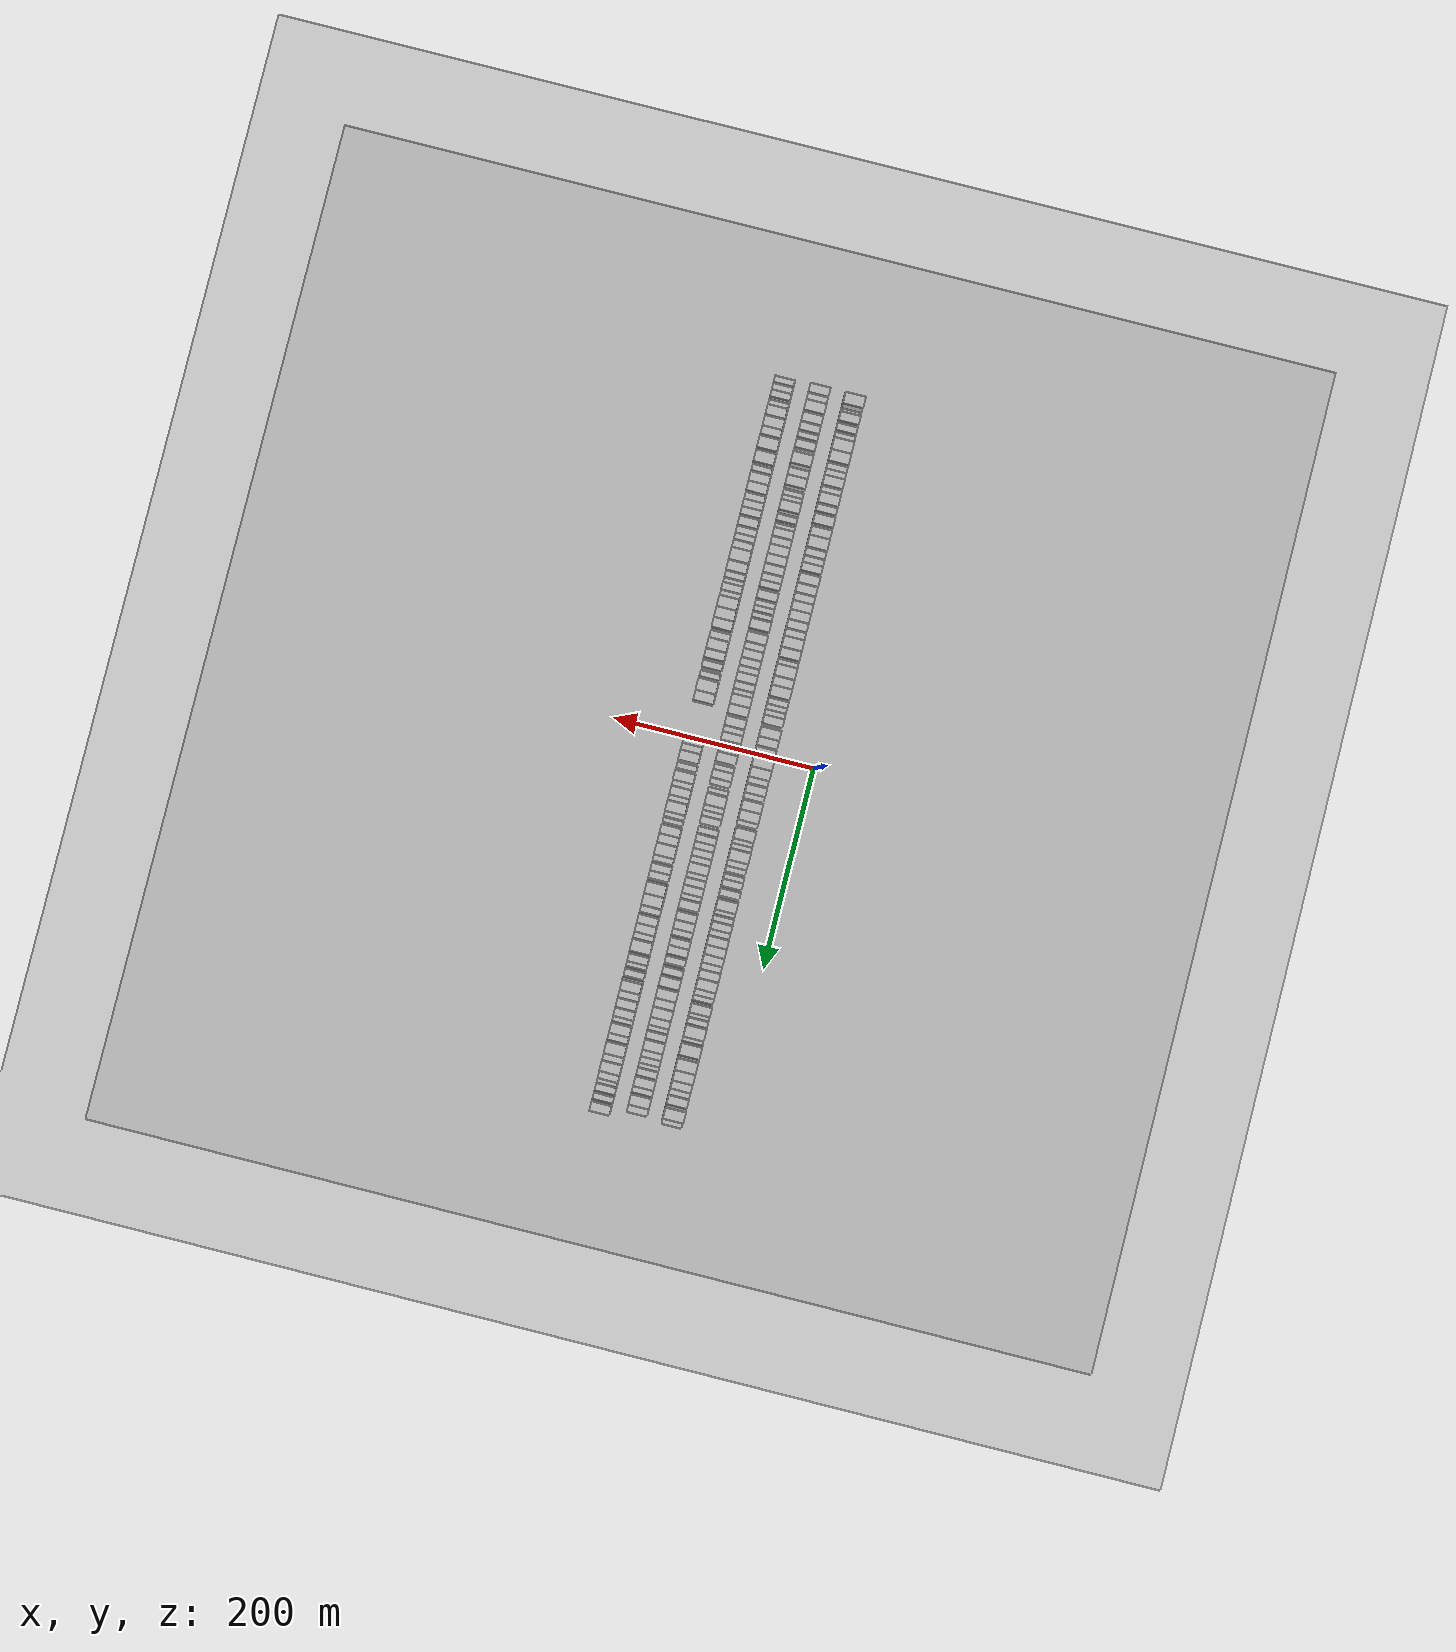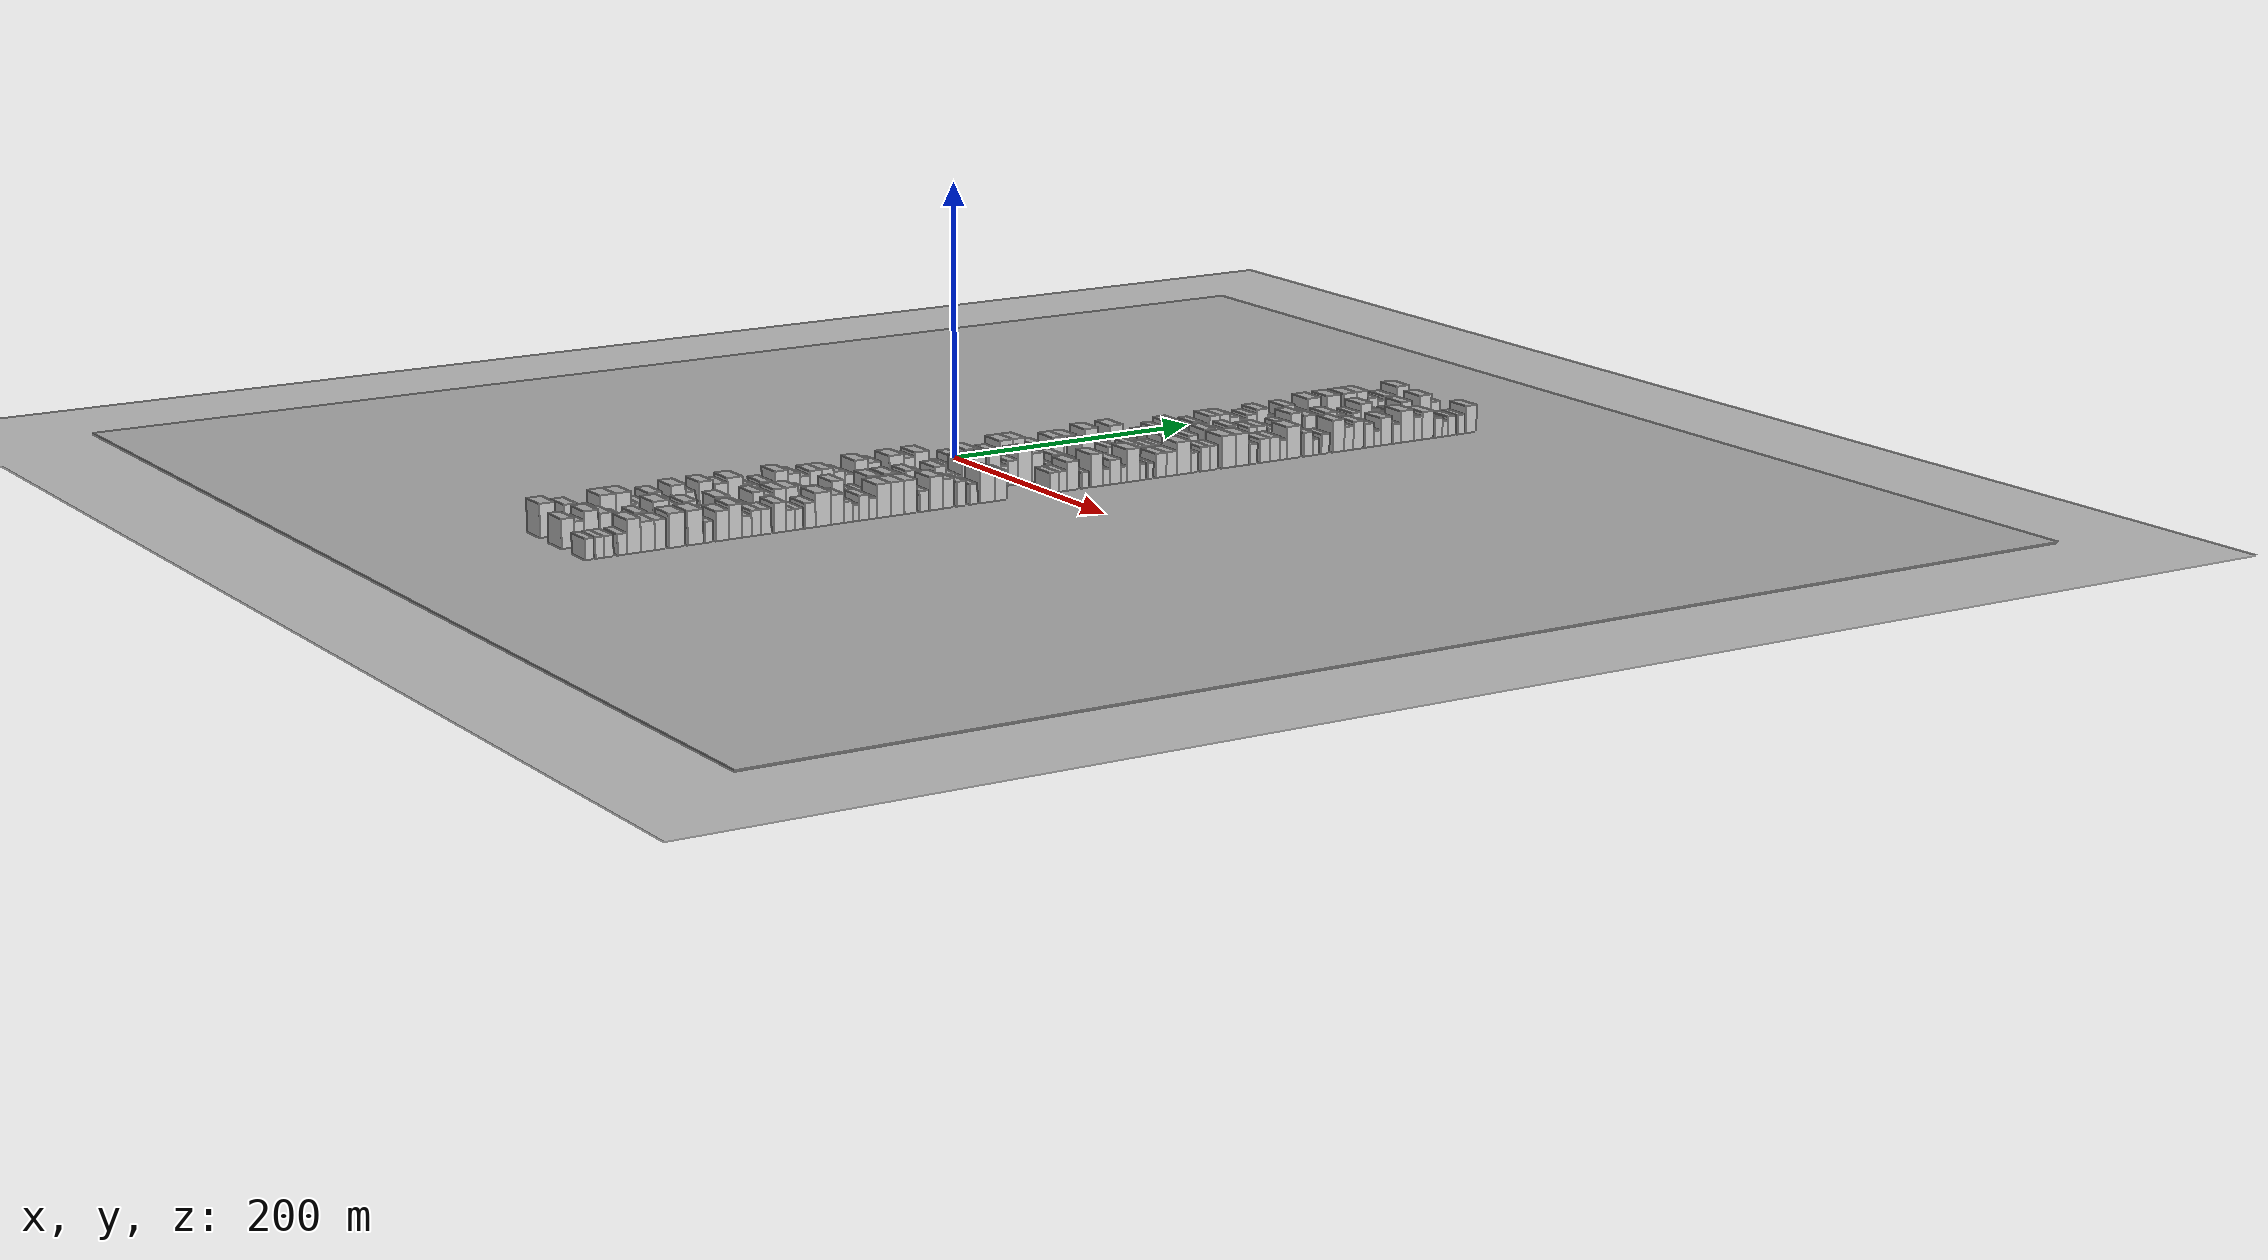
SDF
<?xml version="1.0" encoding="utf-8"?>

<sdf version="1.6">

   <world name="default">

      <gui fullscreen="0">

         <camera name="user_camera">

            <pose>-15 0 4.57585 0 0 0</pose>

            <view_controller>orbit</view_controller>

         </camera>

      </gui>

      <scene>

         <sky>

           <clouds>

             <speed>12</speed>

           </clouds>

         </sky>

         <ambient>0.4 0.4 0.4 1</ambient>

         <background>0.7 0.7 0.7 1</background>

         <shadows>1</shadows>

      </scene>

      <gravity>0 0 -9.8066</gravity>

      <magnetic_field>6e-06 2.3e-05 -4.2e-05</magnetic_field>

      <physics default="0" name="default_physics" type="ode">

         <ode>

            <solver>

               <type>quick</type>

               <iters>10</iters>

               <sor>1.0</sor>

               <use_dynamic_moi_rescaling>0</use_dynamic_moi_rescaling>

            </solver>

            <constraints>

               <cfm>0</cfm>

               <erp>0.2</erp>

               <contact_max_correcting_vel>100</contact_max_correcting_vel>

               <contact_surface_layer>0.001</contact_surface_layer>

            </constraints>

         </ode>

         <max_step_size>0.004</max_step_size>

         <real_time_factor>1</real_time_factor>

         <real_time_update_rate>250</real_time_update_rate>

      </physics>

      <light name="sun" type="directional">

         <cast_shadows>1</cast_shadows>

         <pose>0 0 10 0 0 0</pose>

         <diffuse>0.8 0.8 0.8 1</diffuse>

         <specular>0.2 0.2 0.2 1</specular>

         <attenuation>

            <range>1000</range>

            <constant>0.9</constant>

            <linear>0.01</linear>

            <quadratic>0.001</quadratic>

         </attenuation>

         <direction>-0.5 0.1 -0.9</direction>

      </light>

      <include>

         <name>ground_plane_1</name>

         <uri>model://HANNAS_ground_plane</uri>

         <pose>0 0 0  0 0 0</pose>

      </include>

      <include>

         <name>ground_plane_2</name>

         <uri>model://HANNAS_ground_plane</uri>

         <pose>100 0 0  0 0 0</pose>

      </include>

      <model name="building_1">

         <static>1</static>

         <pose frame="">50.0000 -353.3251 0 0.000000 0.000000 0.000000</pose>

         <link name="link">

            <pose frame="">0 0 12.00 0 0 0</pose>

            <collision name="collision">

               <geometry>

                  <box>

                     <size>20.0000 11.3498 24.0000</size>

                  </box>

               </geometry>

               <max_contacts>10</max_contacts>

               <surface>

                  <contact>

                     <ode/>

                  </contact>

                  <bounce/>

                  <friction>

                     <torsional>

                        <ode/>

                     </torsional>

                     <ode/>

                  </friction>

               </surface>

            </collision>

            <visual name="visual">

               <cast_shadows>0</cast_shadows>

               <geometry>

                  <box>

                     <size>20.0000 11.3498 24.0000</size>

                  </box>

               </geometry>

               <material>

                  <script>

                     <uri>model://HANNAS_wall/materials/scripts</uri>

                     <uri>model://HANNAS_wall/materials/textures</uri>

                     <name>vrc/HANNAS_wall</name>

                  </script>

               </material>

            </visual>

            <self_collide>0</self_collide>

            <enable_wind>0</enable_wind>

            <kinematic>0</kinematic>

         </link>

      </model>

      <model name="building_2">

         <static>1</static>

         <pose frame="">50.0000 -343.1335 0 0.000000 0.000000 0.000000</pose>

         <link name="link">

            <pose frame="">0 0 6.00 0 0 0</pose>

            <collision name="collision">

               <geometry>

                  <box>

                     <size>20.0000 5.0335 12.0000</size>

                  </box>

               </geometry>

               <max_contacts>10</max_contacts>

               <surface>

                  <contact>

                     <ode/>

                  </contact>

                  <bounce/>

                  <friction>

                     <torsional>

                        <ode/>

                     </torsional>

                     <ode/>

                  </friction>

               </surface>

            </collision>

            <visual name="visual">

               <cast_shadows>0</cast_shadows>

               <geometry>

                  <box>

                     <size>20.0000 5.0335 12.0000</size>

                  </box>

               </geometry>

               <material>

                  <script>

                     <uri>model://HANNAS_wall/materials/scripts</uri>

                     <uri>model://HANNAS_wall/materials/textures</uri>

                     <name>vrc/HANNAS_wall</name>

                  </script>

               </material>

            </visual>

            <self_collide>0</self_collide>

            <enable_wind>0</enable_wind>

            <kinematic>0</kinematic>

         </link>

      </model>

      <model name="building_3">

         <static>1</static>

         <pose frame="">50.0000 -335.9942 0 0.000000 0.000000 0.000000</pose>

         <link name="link">

            <pose frame="">0 0 10.50 0 0 0</pose>

            <collision name="collision">

               <geometry>

                  <box>

                     <size>20.0000 9.2450 21.0000</size>

                  </box>

               </geometry>

               <max_contacts>10</max_contacts>

               <surface>

                  <contact>

                     <ode/>

                  </contact>

                  <bounce/>

                  <friction>

                     <torsional>

                        <ode/>

                     </torsional>

                     <ode/>

                  </friction>

               </surface>

            </collision>

            <visual name="visual">

               <cast_shadows>0</cast_shadows>

               <geometry>

                  <box>

                     <size>20.0000 9.2450 21.0000</size>

                  </box>

               </geometry>

               <material>

                  <script>

                     <uri>model://HANNAS_wall/materials/scripts</uri>

                     <uri>model://HANNAS_wall/materials/textures</uri>

                     <name>vrc/HANNAS_wall</name>

                  </script>

               </material>

            </visual>

            <self_collide>0</self_collide>

            <enable_wind>0</enable_wind>

            <kinematic>0</kinematic>

         </link>

      </model>

      <model name="building_4">

         <static>1</static>

         <pose frame="">50.0000 -326.7886 0 0.000000 0.000000 0.000000</pose>

         <link name="link">

            <pose frame="">0 0 7.50 0 0 0</pose>

            <collision name="collision">

               <geometry>

                  <box>

                     <size>20.0000 7.1661 15.0000</size>

                  </box>

               </geometry>

               <max_contacts>10</max_contacts>

               <surface>

                  <contact>

                     <ode/>

                  </contact>

                  <bounce/>

                  <friction>

                     <torsional>

                        <ode/>

                     </torsional>

                     <ode/>

                  </friction>

               </surface>

            </collision>

            <visual name="visual">

               <cast_shadows>0</cast_shadows>

               <geometry>

                  <box>

                     <size>20.0000 7.1661 15.0000</size>

                  </box>

               </geometry>

               <material>

                  <script>

                     <uri>model://HANNAS_wall/materials/scripts</uri>

                     <uri>model://HANNAS_wall/materials/textures</uri>

                     <name>vrc/HANNAS_wall</name>

                  </script>

               </material>

            </visual>

            <self_collide>0</self_collide>

            <enable_wind>0</enable_wind>

            <kinematic>0</kinematic>

         </link>

      </model>

      <model name="building_5">

         <static>1</static>

         <pose frame="">50.0000 -317.5705 0 0.000000 0.000000 0.000000</pose>

         <link name="link">

            <pose frame="">0 0 7.50 0 0 0</pose>

            <collision name="collision">

               <geometry>

                  <box>

                     <size>20.0000 7.2703 15.0000</size>

                  </box>

               </geometry>

               <max_contacts>10</max_contacts>

               <surface>

                  <contact>

                     <ode/>

                  </contact>

                  <bounce/>

                  <friction>

                     <torsional>

                        <ode/>

                     </torsional>

                     <ode/>

                  </friction>

               </surface>

            </collision>

            <visual name="visual">

               <cast_shadows>0</cast_shadows>

               <geometry>

                  <box>

                     <size>20.0000 7.2703 15.0000</size>

                  </box>

               </geometry>

               <material>

                  <script>

                     <uri>model://HANNAS_wall/materials/scripts</uri>

                     <uri>model://HANNAS_wall/materials/textures</uri>

                     <name>vrc/HANNAS_wall</name>

                  </script>

               </material>

            </visual>

            <self_collide>0</self_collide>

            <enable_wind>0</enable_wind>

            <kinematic>0</kinematic>

         </link>

      </model>

      <model name="building_6">

         <static>1</static>

         <pose frame="">50.0000 -308.0313 0 0.000000 0.000000 0.000000</pose>

         <link name="link">

            <pose frame="">0 0 12.00 0 0 0</pose>

            <collision name="collision">

               <geometry>

                  <box>

                     <size>20.0000 11.8082 24.0000</size>

                  </box>

               </geometry>

               <max_contacts>10</max_contacts>

               <surface>

                  <contact>

                     <ode/>

                  </contact>

                  <bounce/>

                  <friction>

                     <torsional>

                        <ode/>

                     </torsional>

                     <ode/>

                  </friction>

               </surface>

            </collision>

            <visual name="visual">

               <cast_shadows>0</cast_shadows>

               <geometry>

                  <box>

                     <size>20.0000 11.8082 24.0000</size>

                  </box>

               </geometry>

               <material>

                  <script>

                     <uri>model://HANNAS_wall/materials/scripts</uri>

                     <uri>model://HANNAS_wall/materials/textures</uri>

                     <name>vrc/HANNAS_wall</name>

                  </script>

               </material>

            </visual>

            <self_collide>0</self_collide>

            <enable_wind>0</enable_wind>

            <kinematic>0</kinematic>

         </link>

      </model>

      <model name="building_7">

         <static>1</static>

         <pose frame="">50.0000 -296.3901 0 0.000000 0.000000 0.000000</pose>

         <link name="link">

            <pose frame="">0 0 12.00 0 0 0</pose>

            <collision name="collision">

               <geometry>

                  <box>

                     <size>20.0000 11.4741 24.0000</size>

                  </box>

               </geometry>

               <max_contacts>10</max_contacts>

               <surface>

                  <contact>

                     <ode/>

                  </contact>

                  <bounce/>

                  <friction>

                     <torsional>

                        <ode/>

                     </torsional>

                     <ode/>

                  </friction>

               </surface>

            </collision>

            <visual name="visual">

               <cast_shadows>0</cast_shadows>

               <geometry>

                  <box>

                     <size>20.0000 11.4741 24.0000</size>

                  </box>

               </geometry>

               <material>

                  <script>

                     <uri>model://HANNAS_wall/materials/scripts</uri>

                     <uri>model://HANNAS_wall/materials/textures</uri>

                     <name>vrc/HANNAS_wall</name>

                  </script>

               </material>

            </visual>

            <self_collide>0</self_collide>

            <enable_wind>0</enable_wind>

            <kinematic>0</kinematic>

         </link>

      </model>

      <model name="building_8">

         <static>1</static>

         <pose frame="">50.0000 -287.5126 0 0.000000 0.000000 0.000000</pose>

         <link name="link">

            <pose frame="">0 0 7.50 0 0 0</pose>

            <collision name="collision">

               <geometry>

                  <box>

                     <size>20.0000 6.2810 15.0000</size>

                  </box>

               </geometry>

               <max_contacts>10</max_contacts>

               <surface>

                  <contact>

                     <ode/>

                  </contact>

                  <bounce/>

                  <friction>

                     <torsional>

                        <ode/>

                     </torsional>

                     <ode/>

                  </friction>

               </surface>

            </collision>

            <visual name="visual">

               <cast_shadows>0</cast_shadows>

               <geometry>

                  <box>

                     <size>20.0000 6.2810 15.0000</size>

                  </box>

               </geometry>

               <material>

                  <script>

                     <uri>model://HANNAS_wall/materials/scripts</uri>

                     <uri>model://HANNAS_wall/materials/textures</uri>

                     <name>vrc/HANNAS_wall</name>

                  </script>

               </material>

            </visual>

            <self_collide>0</self_collide>

            <enable_wind>0</enable_wind>

            <kinematic>0</kinematic>

         </link>

      </model>

      <model name="building_9">

         <static>1</static>

         <pose frame="">50.0000 -280.7550 0 0.000000 0.000000 0.000000</pose>

         <link name="link">

            <pose frame="">0 0 7.50 0 0 0</pose>

            <collision name="collision">

               <geometry>

                  <box>

                     <size>20.0000 7.2342 15.0000</size>

                  </box>

               </geometry>

               <max_contacts>10</max_contacts>

               <surface>

                  <contact>

                     <ode/>

                  </contact>

                  <bounce/>

                  <friction>

                     <torsional>

                        <ode/>

                     </torsional>

                     <ode/>

                  </friction>

               </surface>

            </collision>

            <visual name="visual">

               <cast_shadows>0</cast_shadows>

               <geometry>

                  <box>

                     <size>20.0000 7.2342 15.0000</size>

                  </box>

               </geometry>

               <material>

                  <script>

                     <uri>model://HANNAS_wall/materials/scripts</uri>

                     <uri>model://HANNAS_wall/materials/textures</uri>

                     <name>vrc/HANNAS_wall</name>

                  </script>

               </material>

            </visual>

            <self_collide>0</self_collide>

            <enable_wind>0</enable_wind>

            <kinematic>0</kinematic>

         </link>

      </model>

      <model name="building_10">

         <static>1</static>

         <pose frame="">50.0000 -272.1799 0 0.000000 0.000000 0.000000</pose>

         <link name="link">

            <pose frame="">0 0 10.50 0 0 0</pose>

            <collision name="collision">

               <geometry>

                  <box>

                     <size>20.0000 9.9160 21.0000</size>

                  </box>

               </geometry>

               <max_contacts>10</max_contacts>

               <surface>

                  <contact>

                     <ode/>

                  </contact>

                  <bounce/>

                  <friction>

                     <torsional>

                        <ode/>

                     </torsional>

                     <ode/>

                  </friction>

               </surface>

            </collision>

            <visual name="visual">

               <cast_shadows>0</cast_shadows>

               <geometry>

                  <box>

                     <size>20.0000 9.9160 21.0000</size>

                  </box>

               </geometry>

               <material>

                  <script>

                     <uri>model://HANNAS_wall/materials/scripts</uri>

                     <uri>model://HANNAS_wall/materials/textures</uri>

                     <name>vrc/HANNAS_wall</name>

                  </script>

               </material>

            </visual>

            <self_collide>0</self_collide>

            <enable_wind>0</enable_wind>

            <kinematic>0</kinematic>

         </link>

      </model>

      <model name="building_11">

         <static>1</static>

         <pose frame="">50.0000 -263.5175 0 0.000000 0.000000 0.000000</pose>

         <link name="link">

            <pose frame="">0 0 7.50 0 0 0</pose>

            <collision name="collision">

               <geometry>

                  <box>

                     <size>20.0000 7.4087 15.0000</size>

                  </box>

               </geometry>

               <max_contacts>10</max_contacts>

               <surface>

                  <contact>

                     <ode/>

                  </contact>

                  <bounce/>

                  <friction>

                     <torsional>

                        <ode/>

                     </torsional>

                     <ode/>

                  </friction>

               </surface>

            </collision>

            <visual name="visual">

               <cast_shadows>0</cast_shadows>

               <geometry>

                  <box>

                     <size>20.0000 7.4087 15.0000</size>

                  </box>

               </geometry>

               <material>

                  <script>

                     <uri>model://HANNAS_wall/materials/scripts</uri>

                     <uri>model://HANNAS_wall/materials/textures</uri>

                     <name>vrc/HANNAS_wall</name>

                  </script>

               </material>

            </visual>

            <self_collide>0</self_collide>

            <enable_wind>0</enable_wind>

            <kinematic>0</kinematic>

         </link>

      </model>

      <model name="building_12">

         <static>1</static>

         <pose frame="">50.0000 -254.4428 0 0.000000 0.000000 0.000000</pose>

         <link name="link">

            <pose frame="">0 0 12.00 0 0 0</pose>

            <collision name="collision">

               <geometry>

                  <box>

                     <size>20.0000 10.7407 24.0000</size>

                  </box>

               </geometry>

               <max_contacts>10</max_contacts>

               <surface>

                  <contact>

                     <ode/>

                  </contact>

                  <bounce/>

                  <friction>

                     <torsional>

                        <ode/>

                     </torsional>

                     <ode/>

                  </friction>

               </surface>

            </collision>

            <visual name="visual">

               <cast_shadows>0</cast_shadows>

               <geometry>

                  <box>

                     <size>20.0000 10.7407 24.0000</size>

                  </box>

               </geometry>

               <material>

                  <script>

                     <uri>model://HANNAS_wall/materials/scripts</uri>

                     <uri>model://HANNAS_wall/materials/textures</uri>

                     <name>vrc/HANNAS_wall</name>

                  </script>

               </material>

            </visual>

            <self_collide>0</self_collide>

            <enable_wind>0</enable_wind>

            <kinematic>0</kinematic>

         </link>

      </model>

      <model name="building_13">

         <static>1</static>

         <pose frame="">50.0000 -245.2816 0 0.000000 0.000000 0.000000</pose>

         <link name="link">

            <pose frame="">0 0 9.00 0 0 0</pose>

            <collision name="collision">

               <geometry>

                  <box>

                     <size>20.0000 7.5817 18.0000</size>

                  </box>

               </geometry>

               <max_contacts>10</max_contacts>

               <surface>

                  <contact>

                     <ode/>

                  </contact>

                  <bounce/>

                  <friction>

                     <torsional>

                        <ode/>

                     </torsional>

                     <ode/>

                  </friction>

               </surface>

            </collision>

            <visual name="visual">

               <cast_shadows>0</cast_shadows>

               <geometry>

                  <box>

                     <size>20.0000 7.5817 18.0000</size>

                  </box>

               </geometry>

               <material>

                  <script>

                     <uri>model://HANNAS_wall/materials/scripts</uri>

                     <uri>model://HANNAS_wall/materials/textures</uri>

                     <name>vrc/HANNAS_wall</name>

                  </script>

               </material>

            </visual>

            <self_collide>0</self_collide>

            <enable_wind>0</enable_wind>

            <kinematic>0</kinematic>

         </link>

      </model>

      <model name="building_14">

         <static>1</static>

         <pose frame="">50.0000 -233.3662 0 0.000000 0.000000 0.000000</pose>

         <link name="link">

            <pose frame="">0 0 12.00 0 0 0</pose>

            <collision name="collision">

               <geometry>

                  <box>

                     <size>20.0000 10.2491 24.0000</size>

                  </box>

               </geometry>

               <max_contacts>10</max_contacts>

               <surface>

                  <contact>

                     <ode/>

                  </contact>

                  <bounce/>

                  <friction>

                     <torsional>

                        <ode/>

                     </torsional>

                     <ode/>

                  </friction>

               </surface>

            </collision>

            <visual name="visual">

               <cast_shadows>0</cast_shadows>

               <geometry>

                  <box>

                     <size>20.0000 10.2491 24.0000</size>

                  </box>

               </geometry>

               <material>

                  <script>

                     <uri>model://HANNAS_wall/materials/scripts</uri>

                     <uri>model://HANNAS_wall/materials/textures</uri>

                     <name>vrc/HANNAS_wall</name>

                  </script>

               </material>

            </visual>

            <self_collide>0</self_collide>

            <enable_wind>0</enable_wind>

            <kinematic>0</kinematic>

         </link>

      </model>

      <model name="building_15">

         <static>1</static>

         <pose frame="">50.0000 -221.4860 0 0.000000 0.000000 0.000000</pose>

         <link name="link">

            <pose frame="">0 0 10.50 0 0 0</pose>

            <collision name="collision">

               <geometry>

                  <box>

                     <size>20.0000 9.5113 21.0000</size>

                  </box>

               </geometry>

               <max_contacts>10</max_contacts>

               <surface>

                  <contact>

                     <ode/>

                  </contact>

                  <bounce/>

                  <friction>

                     <torsional>

                        <ode/>

                     </torsional>

                     <ode/>

                  </friction>

               </surface>

            </collision>

            <visual name="visual">

               <cast_shadows>0</cast_shadows>

               <geometry>

                  <box>

                     <size>20.0000 9.5113 21.0000</size>

                  </box>

               </geometry>

               <material>

                  <script>

                     <uri>model://HANNAS_wall/materials/scripts</uri>

                     <uri>model://HANNAS_wall/materials/textures</uri>

                     <name>vrc/HANNAS_wall</name>

                  </script>

               </material>

            </visual>

            <self_collide>0</self_collide>

            <enable_wind>0</enable_wind>

            <kinematic>0</kinematic>

         </link>

      </model>

      <model name="building_16">

         <static>1</static>

         <pose frame="">50.0000 -210.9035 0 0.000000 0.000000 0.000000</pose>

         <link name="link">

            <pose frame="">0 0 12.00 0 0 0</pose>

            <collision name="collision">

               <geometry>

                  <box>

                     <size>20.0000 11.6537 24.0000</size>

                  </box>

               </geometry>

               <max_contacts>10</max_contacts>

               <surface>

                  <contact>

                     <ode/>

                  </contact>

                  <bounce/>

                  <friction>

                     <torsional>

                        <ode/>

                     </torsional>

                     <ode/>

                  </friction>

               </surface>

            </collision>

            <visual name="visual">

               <cast_shadows>0</cast_shadows>

               <geometry>

                  <box>

                     <size>20.0000 11.6537 24.0000</size>

                  </box>

               </geometry>

               <material>

                  <script>

                     <uri>model://HANNAS_wall/materials/scripts</uri>

                     <uri>model://HANNAS_wall/materials/textures</uri>

                     <name>vrc/HANNAS_wall</name>

                  </script>

               </material>

            </visual>

            <self_collide>0</self_collide>

            <enable_wind>0</enable_wind>

            <kinematic>0</kinematic>

         </link>

      </model>

      <model name="building_17">

         <static>1</static>

         <pose frame="">50.0000 -201.3647 0 0.000000 0.000000 0.000000</pose>

         <link name="link">

            <pose frame="">0 0 9.00 0 0 0</pose>

            <collision name="collision">

               <geometry>

                  <box>

                     <size>20.0000 7.4239 18.0000</size>

                  </box>

               </geometry>

               <max_contacts>10</max_contacts>

               <surface>

                  <contact>

                     <ode/>

                  </contact>

                  <bounce/>

                  <friction>

                     <torsional>

                        <ode/>

                     </torsional>

                     <ode/>

                  </friction>

               </surface>

            </collision>

            <visual name="visual">

               <cast_shadows>0</cast_shadows>

               <geometry>

                  <box>

                     <size>20.0000 7.4239 18.0000</size>

                  </box>

               </geometry>

               <material>

                  <script>

                     <uri>model://HANNAS_wall/materials/scripts</uri>

                     <uri>model://HANNAS_wall/materials/textures</uri>

                     <name>vrc/HANNAS_wall</name>

                  </script>

               </material>

            </visual>

            <self_collide>0</self_collide>

            <enable_wind>0</enable_wind>

            <kinematic>0</kinematic>

         </link>

      </model>

      <model name="building_18">

         <static>1</static>

         <pose frame="">50.0000 -194.0934 0 0.000000 0.000000 0.000000</pose>

         <link name="link">

            <pose frame="">0 0 7.50 0 0 0</pose>

            <collision name="collision">

               <geometry>

                  <box>

                     <size>20.0000 7.1187 15.0000</size>

                  </box>

               </geometry>

               <max_contacts>10</max_contacts>

               <surface>

                  <contact>

                     <ode/>

                  </contact>

                  <bounce/>

                  <friction>

                     <torsional>

                        <ode/>

                     </torsional>

                     <ode/>

                  </friction>

               </surface>

            </collision>

            <visual name="visual">

               <cast_shadows>0</cast_shadows>

               <geometry>

                  <box>

                     <size>20.0000 7.1187 15.0000</size>

                  </box>

               </geometry>

               <material>

                  <script>

                     <uri>model://HANNAS_wall/materials/scripts</uri>

                     <uri>model://HANNAS_wall/materials/textures</uri>

                     <name>vrc/HANNAS_wall</name>

                  </script>

               </material>

            </visual>

            <self_collide>0</self_collide>

            <enable_wind>0</enable_wind>

            <kinematic>0</kinematic>

         </link>

      </model>

      <model name="building_19">

         <static>1</static>

         <pose frame="">50.0000 -186.5192 0 0.000000 0.000000 0.000000</pose>

         <link name="link">

            <pose frame="">0 0 9.00 0 0 0</pose>

            <collision name="collision">

               <geometry>

                  <box>

                     <size>20.0000 8.0296 18.0000</size>

                  </box>

               </geometry>

               <max_contacts>10</max_contacts>

               <surface>

                  <contact>

                     <ode/>

                  </contact>

                  <bounce/>

                  <friction>

                     <torsional>

                        <ode/>

                     </torsional>

                     <ode/>

                  </friction>

               </surface>

            </collision>

            <visual name="visual">

               <cast_shadows>0</cast_shadows>

               <geometry>

                  <box>

                     <size>20.0000 8.0296 18.0000</size>

                  </box>

               </geometry>

               <material>

                  <script>

                     <uri>model://HANNAS_wall/materials/scripts</uri>

                     <uri>model://HANNAS_wall/materials/textures</uri>

                     <name>vrc/HANNAS_wall</name>

                  </script>

               </material>

            </visual>

            <self_collide>0</self_collide>

            <enable_wind>0</enable_wind>

            <kinematic>0</kinematic>

         </link>

      </model>

      <model name="building_20">

         <static>1</static>

         <pose frame="">50.0000 -174.5588 0 0.000000 0.000000 0.000000</pose>

         <link name="link">

            <pose frame="">0 0 12.00 0 0 0</pose>

            <collision name="collision">

               <geometry>

                  <box>

                     <size>20.0000 9.8912 24.0000</size>

                  </box>

               </geometry>

               <max_contacts>10</max_contacts>

               <surface>

                  <contact>

                     <ode/>

                  </contact>

                  <bounce/>

                  <friction>

                     <torsional>

                        <ode/>

                     </torsional>

                     <ode/>

                  </friction>

               </surface>

            </collision>

            <visual name="visual">

               <cast_shadows>0</cast_shadows>

               <geometry>

                  <box>

                     <size>20.0000 9.8912 24.0000</size>

                  </box>

               </geometry>

               <material>

                  <script>

                     <uri>model://HANNAS_wall/materials/scripts</uri>

                     <uri>model://HANNAS_wall/materials/textures</uri>

                     <name>vrc/HANNAS_wall</name>

                  </script>

               </material>

            </visual>

            <self_collide>0</self_collide>

            <enable_wind>0</enable_wind>

            <kinematic>0</kinematic>

         </link>

      </model>

      <model name="building_21">

         <static>1</static>

         <pose frame="">50.0000 -164.9927 0 0.000000 0.000000 0.000000</pose>

         <link name="link">

            <pose frame="">0 0 10.50 0 0 0</pose>

            <collision name="collision">

               <geometry>

                  <box>

                     <size>20.0000 9.2410 21.0000</size>

                  </box>

               </geometry>

               <max_contacts>10</max_contacts>

               <surface>

                  <contact>

                     <ode/>

                  </contact>

                  <bounce/>

                  <friction>

                     <torsional>

                        <ode/>

                     </torsional>

                     <ode/>

                  </friction>

               </surface>

            </collision>

            <visual name="visual">

               <cast_shadows>0</cast_shadows>

               <geometry>

                  <box>

                     <size>20.0000 9.2410 21.0000</size>

                  </box>

               </geometry>

               <material>

                  <script>

                     <uri>model://HANNAS_wall/materials/scripts</uri>

                     <uri>model://HANNAS_wall/materials/textures</uri>

                     <name>vrc/HANNAS_wall</name>

                  </script>

               </material>

            </visual>

            <self_collide>0</self_collide>

            <enable_wind>0</enable_wind>

            <kinematic>0</kinematic>

         </link>

      </model>

      <model name="building_22">

         <static>1</static>

         <pose frame="">50.0000 -156.3295 0 0.000000 0.000000 0.000000</pose>

         <link name="link">

            <pose frame="">0 0 9.00 0 0 0</pose>

            <collision name="collision">

               <geometry>

                  <box>

                     <size>20.0000 8.0855 18.0000</size>

                  </box>

               </geometry>

               <max_contacts>10</max_contacts>

               <surface>

                  <contact>

                     <ode/>

                  </contact>

                  <bounce/>

                  <friction>

                     <torsional>

                        <ode/>

                     </torsional>

                     <ode/>

                  </friction>

               </surface>

            </collision>

            <visual name="visual">

               <cast_shadows>0</cast_shadows>

               <geometry>

                  <box>

                     <size>20.0000 8.0855 18.0000</size>

                  </box>

               </geometry>

               <material>

                  <script>

                     <uri>model://HANNAS_wall/materials/scripts</uri>

                     <uri>model://HANNAS_wall/materials/textures</uri>

                     <name>vrc/HANNAS_wall</name>

                  </script>

               </material>

            </visual>

            <self_collide>0</self_collide>

            <enable_wind>0</enable_wind>

            <kinematic>0</kinematic>

         </link>

      </model>

      <model name="building_23">

         <static>1</static>

         <pose frame="">50.0000 -147.6939 0 0.000000 0.000000 0.000000</pose>

         <link name="link">

            <pose frame="">0 0 10.50 0 0 0</pose>

            <collision name="collision">

               <geometry>

                  <box>

                     <size>20.0000 9.1857 21.0000</size>

                  </box>

               </geometry>

               <max_contacts>10</max_contacts>

               <surface>

                  <contact>

                     <ode/>

                  </contact>

                  <bounce/>

                  <friction>

                     <torsional>

                        <ode/>

                     </torsional>

                     <ode/>

                  </friction>

               </surface>

            </collision>

            <visual name="visual">

               <cast_shadows>0</cast_shadows>

               <geometry>

                  <box>

                     <size>20.0000 9.1857 21.0000</size>

                  </box>

               </geometry>

               <material>

                  <script>

                     <uri>model://HANNAS_wall/materials/scripts</uri>

                     <uri>model://HANNAS_wall/materials/textures</uri>

                     <name>vrc/HANNAS_wall</name>

                  </script>

               </material>

            </visual>

            <self_collide>0</self_collide>

            <enable_wind>0</enable_wind>

            <kinematic>0</kinematic>

         </link>

      </model>

      <model name="building_24">

         <static>1</static>

         <pose frame="">50.0000 -138.3923 0 0.000000 0.000000 0.000000</pose>

         <link name="link">

            <pose frame="">0 0 10.50 0 0 0</pose>

            <collision name="collision">

               <geometry>

                  <box>

                     <size>20.0000 9.4174 21.0000</size>

                  </box>

               </geometry>

               <max_contacts>10</max_contacts>

               <surface>

                  <contact>

                     <ode/>

                  </contact>

                  <bounce/>

                  <friction>

                     <torsional>

                        <ode/>

                     </torsional>

                     <ode/>

                  </friction>

               </surface>

            </collision>

            <visual name="visual">

               <cast_shadows>0</cast_shadows>

               <geometry>

                  <box>

                     <size>20.0000 9.4174 21.0000</size>

                  </box>

               </geometry>

               <material>

                  <script>

                     <uri>model://HANNAS_wall/materials/scripts</uri>

                     <uri>model://HANNAS_wall/materials/textures</uri>

                     <name>vrc/HANNAS_wall</name>

                  </script>

               </material>

            </visual>

            <self_collide>0</self_collide>

            <enable_wind>0</enable_wind>

            <kinematic>0</kinematic>

         </link>

      </model>

      <model name="building_25">

         <static>1</static>

         <pose frame="">50.0000 -129.3081 0 0.000000 0.000000 0.000000</pose>

         <link name="link">

            <pose frame="">0 0 9.00 0 0 0</pose>

            <collision name="collision">

               <geometry>

                  <box>

                     <size>20.0000 8.7510 18.0000</size>

                  </box>

               </geometry>

               <max_contacts>10</max_contacts>

               <surface>

                  <contact>

                     <ode/>

                  </contact>

                  <bounce/>

                  <friction>

                     <torsional>

                        <ode/>

                     </torsional>

                     <ode/>

                  </friction>

               </surface>

            </collision>

            <visual name="visual">

               <cast_shadows>0</cast_shadows>

               <geometry>

                  <box>

                     <size>20.0000 8.7510 18.0000</size>

                  </box>

               </geometry>

               <material>

                  <script>

                     <uri>model://HANNAS_wall/materials/scripts</uri>

                     <uri>model://HANNAS_wall/materials/textures</uri>

                     <name>vrc/HANNAS_wall</name>

                  </script>

               </material>

            </visual>

            <self_collide>0</self_collide>

            <enable_wind>0</enable_wind>

            <kinematic>0</kinematic>

         </link>

      </model>

      <model name="building_26">

         <static>1</static>

         <pose frame="">50.0000 -121.2679 0 0.000000 0.000000 0.000000</pose>

         <link name="link">

            <pose frame="">0 0 7.50 0 0 0</pose>

            <collision name="collision">

               <geometry>

                  <box>

                     <size>20.0000 7.3296 15.0000</size>

                  </box>

               </geometry>

               <max_contacts>10</max_contacts>

               <surface>

                  <contact>

                     <ode/>

                  </contact>

                  <bounce/>

                  <friction>

                     <torsional>

                        <ode/>

                     </torsional>

                     <ode/>

                  </friction>

               </surface>

            </collision>

            <visual name="visual">

               <cast_shadows>0</cast_shadows>

               <geometry>

                  <box>

                     <size>20.0000 7.3296 15.0000</size>

                  </box>

               </geometry>

               <material>

                  <script>

                     <uri>model://HANNAS_wall/materials/scripts</uri>

                     <uri>model://HANNAS_wall/materials/textures</uri>

                     <name>vrc/HANNAS_wall</name>

                  </script>

               </material>

            </visual>

            <self_collide>0</self_collide>

            <enable_wind>0</enable_wind>

            <kinematic>0</kinematic>

         </link>

      </model>

      <model name="building_27">

         <static>1</static>

         <pose frame="">50.0000 -111.2162 0 0.000000 0.000000 0.000000</pose>

         <link name="link">

            <pose frame="">0 0 12.00 0 0 0</pose>

            <collision name="collision">

               <geometry>

                  <box>

                     <size>20.0000 10.7738 24.0000</size>

                  </box>

               </geometry>

               <max_contacts>10</max_contacts>

               <surface>

                  <contact>

                     <ode/>

                  </contact>

                  <bounce/>

                  <friction>

                     <torsional>

                        <ode/>

                     </torsional>

                     <ode/>

                  </friction>

               </surface>

            </collision>

            <visual name="visual">

               <cast_shadows>0</cast_shadows>

               <geometry>

                  <box>

                     <size>20.0000 10.7738 24.0000</size>

                  </box>

               </geometry>

               <material>

                  <script>

                     <uri>model://HANNAS_wall/materials/scripts</uri>

                     <uri>model://HANNAS_wall/materials/textures</uri>

                     <name>vrc/HANNAS_wall</name>

                  </script>

               </material>

            </visual>

            <self_collide>0</self_collide>

            <enable_wind>0</enable_wind>

            <kinematic>0</kinematic>

         </link>

      </model>

      <model name="building_28">

         <static>1</static>

         <pose frame="">50.0000 -100.9177 0 0.000000 0.000000 0.000000</pose>

         <link name="link">

            <pose frame="">0 0 10.50 0 0 0</pose>

            <collision name="collision">

               <geometry>

                  <box>

                     <size>20.0000 9.8232 21.0000</size>

                  </box>

               </geometry>

               <max_contacts>10</max_contacts>

               <surface>

                  <contact>

                     <ode/>

                  </contact>

                  <bounce/>

                  <friction>

                     <torsional>

                        <ode/>

                     </torsional>

                     <ode/>

                  </friction>

               </surface>

            </collision>

            <visual name="visual">

               <cast_shadows>0</cast_shadows>

               <geometry>

                  <box>

                     <size>20.0000 9.8232 21.0000</size>

                  </box>

               </geometry>

               <material>

                  <script>

                     <uri>model://HANNAS_wall/materials/scripts</uri>

                     <uri>model://HANNAS_wall/materials/textures</uri>

                     <name>vrc/HANNAS_wall</name>

                  </script>

               </material>

            </visual>

            <self_collide>0</self_collide>

            <enable_wind>0</enable_wind>

            <kinematic>0</kinematic>

         </link>

      </model>

      <model name="building_29">

         <static>1</static>

         <pose frame="">50.0000 -92.4581 0 0.000000 0.000000 0.000000</pose>

         <link name="link">

            <pose frame="">0 0 6.00 0 0 0</pose>

            <collision name="collision">

               <geometry>

                  <box>

                     <size>20.0000 5.0960 12.0000</size>

                  </box>

               </geometry>

               <max_contacts>10</max_contacts>

               <surface>

                  <contact>

                     <ode/>

                  </contact>

                  <bounce/>

                  <friction>

                     <torsional>

                        <ode/>

                     </torsional>

                     <ode/>

                  </friction>

               </surface>

            </collision>

            <visual name="visual">

               <cast_shadows>0</cast_shadows>

               <geometry>

                  <box>

                     <size>20.0000 5.0960 12.0000</size>

                  </box>

               </geometry>

               <material>

                  <script>

                     <uri>model://HANNAS_wall/materials/scripts</uri>

                     <uri>model://HANNAS_wall/materials/textures</uri>

                     <name>vrc/HANNAS_wall</name>

                  </script>

               </material>

            </visual>

            <self_collide>0</self_collide>

            <enable_wind>0</enable_wind>

            <kinematic>0</kinematic>

         </link>

      </model>

      <model name="building_30">

         <static>1</static>

         <pose frame="">50.0000 -83.1273 0 0.000000 0.000000 0.000000</pose>

         <link name="link">

            <pose frame="">0 0 12.00 0 0 0</pose>

            <collision name="collision">

               <geometry>

                  <box>

                     <size>20.0000 11.5656 24.0000</size>

                  </box>

               </geometry>

               <max_contacts>10</max_contacts>

               <surface>

                  <contact>

                     <ode/>

                  </contact>

                  <bounce/>

                  <friction>

                     <torsional>

                        <ode/>

                     </torsional>

                     <ode/>

                  </friction>

               </surface>

            </collision>

            <visual name="visual">

               <cast_shadows>0</cast_shadows>

               <geometry>

                  <box>

                     <size>20.0000 11.5656 24.0000</size>

                  </box>

               </geometry>

               <material>

                  <script>

                     <uri>model://HANNAS_wall/materials/scripts</uri>

                     <uri>model://HANNAS_wall/materials/textures</uri>

                     <name>vrc/HANNAS_wall</name>

                  </script>

               </material>

            </visual>

            <self_collide>0</self_collide>

            <enable_wind>0</enable_wind>

            <kinematic>0</kinematic>

         </link>

      </model>

      <model name="building_31">

         <static>1</static>

         <pose frame="">50.0000 -72.7295 0 0.000000 0.000000 0.000000</pose>

         <link name="link">

            <pose frame="">0 0 10.50 0 0 0</pose>

            <collision name="collision">

               <geometry>

                  <box>

                     <size>20.0000 9.2299 21.0000</size>

                  </box>

               </geometry>

               <max_contacts>10</max_contacts>

               <surface>

                  <contact>

                     <ode/>

                  </contact>

                  <bounce/>

                  <friction>

                     <torsional>

                        <ode/>

                     </torsional>

                     <ode/>

                  </friction>

               </surface>

            </collision>

            <visual name="visual">

               <cast_shadows>0</cast_shadows>

               <geometry>

                  <box>

                     <size>20.0000 9.2299 21.0000</size>

                  </box>

               </geometry>

               <material>

                  <script>

                     <uri>model://HANNAS_wall/materials/scripts</uri>

                     <uri>model://HANNAS_wall/materials/textures</uri>

                     <name>vrc/HANNAS_wall</name>

                  </script>

               </material>

            </visual>

            <self_collide>0</self_collide>

            <enable_wind>0</enable_wind>

            <kinematic>0</kinematic>

         </link>

      </model>

      <model name="building_32">

         <static>1</static>

         <pose frame="">50.0000 -62.6246 0 0.000000 0.000000 0.000000</pose>

         <link name="link">

            <pose frame="">0 0 12.00 0 0 0</pose>

            <collision name="collision">

               <geometry>

                  <box>

                     <size>20.0000 10.9799 24.0000</size>

                  </box>

               </geometry>

               <max_contacts>10</max_contacts>

               <surface>

                  <contact>

                     <ode/>

                  </contact>

                  <bounce/>

                  <friction>

                     <torsional>

                        <ode/>

                     </torsional>

                     <ode/>

                  </friction>

               </surface>

            </collision>

            <visual name="visual">

               <cast_shadows>0</cast_shadows>

               <geometry>

                  <box>

                     <size>20.0000 10.9799 24.0000</size>

                  </box>

               </geometry>

               <material>

                  <script>

                     <uri>model://HANNAS_wall/materials/scripts</uri>

                     <uri>model://HANNAS_wall/materials/textures</uri>

                     <name>vrc/HANNAS_wall</name>

                  </script>

               </material>

            </visual>

            <self_collide>0</self_collide>

            <enable_wind>0</enable_wind>

            <kinematic>0</kinematic>

         </link>

      </model>

      <model name="building_33">

         <static>1</static>

         <pose frame="">50.0000 -52.9839 0 0.000000 0.000000 0.000000</pose>

         <link name="link">

            <pose frame="">0 0 7.50 0 0 0</pose>

            <collision name="collision">

               <geometry>

                  <box>

                     <size>20.0000 6.3014 15.0000</size>

                  </box>

               </geometry>

               <max_contacts>10</max_contacts>

               <surface>

                  <contact>

                     <ode/>

                  </contact>

                  <bounce/>

                  <friction>

                     <torsional>

                        <ode/>

                     </torsional>

                     <ode/>

                  </friction>

               </surface>

            </collision>

            <visual name="visual">

               <cast_shadows>0</cast_shadows>

               <geometry>

                  <box>

                     <size>20.0000 6.3014 15.0000</size>

                  </box>

               </geometry>

               <material>

                  <script>

                     <uri>model://HANNAS_wall/materials/scripts</uri>

                     <uri>model://HANNAS_wall/materials/textures</uri>

                     <name>vrc/HANNAS_wall</name>

                  </script>

               </material>

            </visual>

            <self_collide>0</self_collide>

            <enable_wind>0</enable_wind>

            <kinematic>0</kinematic>

         </link>

      </model>

      <model name="building_34">

         <static>1</static>

         <pose frame="">50.0000 -47.2102 0 0.000000 0.000000 0.000000</pose>

         <link name="link">

            <pose frame="">0 0 6.00 0 0 0</pose>

            <collision name="collision">

               <geometry>

                  <box>

                     <size>20.0000 5.2459 12.0000</size>

                  </box>

               </geometry>

               <max_contacts>10</max_contacts>

               <surface>

                  <contact>

                     <ode/>

                  </contact>

                  <bounce/>

                  <friction>

                     <torsional>

                        <ode/>

                     </torsional>

                     <ode/>

                  </friction>

               </surface>

            </collision>

            <visual name="visual">

               <cast_shadows>0</cast_shadows>

               <geometry>

                  <box>

                     <size>20.0000 5.2459 12.0000</size>

                  </box>

               </geometry>

               <material>

                  <script>

                     <uri>model://HANNAS_wall/materials/scripts</uri>

                     <uri>model://HANNAS_wall/materials/textures</uri>

                     <name>vrc/HANNAS_wall</name>

                  </script>

               </material>

            </visual>

            <self_collide>0</self_collide>

            <enable_wind>0</enable_wind>

            <kinematic>0</kinematic>

         </link>

      </model>

      <model name="building_35">

         <static>1</static>

         <pose frame="">50.0000 -41.7493 0 0.000000 0.000000 0.000000</pose>

         <link name="link">

            <pose frame="">0 0 6.00 0 0 0</pose>

            <collision name="collision">

               <geometry>

                  <box>

                     <size>20.0000 5.6759 12.0000</size>

                  </box>

               </geometry>

               <max_contacts>10</max_contacts>

               <surface>

                  <contact>

                     <ode/>

                  </contact>

                  <bounce/>

                  <friction>

                     <torsional>

                        <ode/>

                     </torsional>

                     <ode/>

                  </friction>

               </surface>

            </collision>

            <visual name="visual">

               <cast_shadows>0</cast_shadows>

               <geometry>

                  <box>

                     <size>20.0000 5.6759 12.0000</size>

                  </box>

               </geometry>

               <material>

                  <script>

                     <uri>model://HANNAS_wall/materials/scripts</uri>

                     <uri>model://HANNAS_wall/materials/textures</uri>

                     <name>vrc/HANNAS_wall</name>

                  </script>

               </material>

            </visual>

            <self_collide>0</self_collide>

            <enable_wind>0</enable_wind>

            <kinematic>0</kinematic>

         </link>

      </model>

      <model name="building_36">

         <static>1</static>

         <pose frame="">50.0000 -34.4840 0 0.000000 0.000000 0.000000</pose>

         <link name="link">

            <pose frame="">0 0 9.00 0 0 0</pose>

            <collision name="collision">

               <geometry>

                  <box>

                     <size>20.0000 8.8548 18.0000</size>

                  </box>

               </geometry>

               <max_contacts>10</max_contacts>

               <surface>

                  <contact>

                     <ode/>

                  </contact>

                  <bounce/>

                  <friction>

                     <torsional>

                        <ode/>

                     </torsional>

                     <ode/>

                  </friction>

               </surface>

            </collision>

            <visual name="visual">

               <cast_shadows>0</cast_shadows>

               <geometry>

                  <box>

                     <size>20.0000 8.8548 18.0000</size>

                  </box>

               </geometry>

               <material>

                  <script>

                     <uri>model://HANNAS_wall/materials/scripts</uri>

                     <uri>model://HANNAS_wall/materials/textures</uri>

                     <name>vrc/HANNAS_wall</name>

                  </script>

               </material>

            </visual>

            <self_collide>0</self_collide>

            <enable_wind>0</enable_wind>

            <kinematic>0</kinematic>

         </link>

      </model>

      <model name="building_37">

         <static>1</static>

         <pose frame="">50.0000 -22.1702 0 0.000000 0.000000 0.000000</pose>

         <link name="link">

            <pose frame="">0 0 10.50 0 0 0</pose>

            <collision name="collision">

               <geometry>

                  <box>

                     <size>20.0000 9.7728 21.0000</size>

                  </box>

               </geometry>

               <max_contacts>10</max_contacts>

               <surface>

                  <contact>

                     <ode/>

                  </contact>

                  <bounce/>

                  <friction>

                     <torsional>

                        <ode/>

                     </torsional>

                     <ode/>

                  </friction>

               </surface>

            </collision>

            <visual name="visual">

               <cast_shadows>0</cast_shadows>

               <geometry>

                  <box>

                     <size>20.0000 9.7728 21.0000</size>

                  </box>

               </geometry>

               <material>

                  <script>

                     <uri>model://HANNAS_wall/materials/scripts</uri>

                     <uri>model://HANNAS_wall/materials/textures</uri>

                     <name>vrc/HANNAS_wall</name>

                  </script>

               </material>

            </visual>

            <self_collide>0</self_collide>

            <enable_wind>0</enable_wind>

            <kinematic>0</kinematic>

         </link>

      </model>

      <model name="building_38">

         <static>1</static>

         <pose frame="">50.0000 -12.9144 0 0.000000 0.000000 0.000000</pose>

         <link name="link">

            <pose frame="">0 0 9.00 0 0 0</pose>

            <collision name="collision">

               <geometry>

                  <box>

                     <size>20.0000 8.7387 18.0000</size>

                  </box>

               </geometry>

               <max_contacts>10</max_contacts>

               <surface>

                  <contact>

                     <ode/>

                  </contact>

                  <bounce/>

                  <friction>

                     <torsional>

                        <ode/>

                     </torsional>

                     <ode/>

                  </friction>

               </surface>

            </collision>

            <visual name="visual">

               <cast_shadows>0</cast_shadows>

               <geometry>

                  <box>

                     <size>20.0000 8.7387 18.0000</size>

                  </box>

               </geometry>

               <material>

                  <script>

                     <uri>model://HANNAS_wall/materials/scripts</uri>

                     <uri>model://HANNAS_wall/materials/textures</uri>

                     <name>vrc/HANNAS_wall</name>

                  </script>

               </material>

            </visual>

            <self_collide>0</self_collide>

            <enable_wind>0</enable_wind>

            <kinematic>0</kinematic>

         </link>

      </model>

      <model name="building_39">

         <static>1</static>

         <pose frame="">50.0000 -3.1798 0 0.000000 0.000000 0.000000</pose>

         <link name="link">

            <pose frame="">0 0 9.00 0 0 0</pose>

            <collision name="collision">

               <geometry>

                  <box>

                     <size>20.0000 8.7305 18.0000</size>

                  </box>

               </geometry>

               <max_contacts>10</max_contacts>

               <surface>

                  <contact>

                     <ode/>

                  </contact>

                  <bounce/>

                  <friction>

                     <torsional>

                        <ode/>

                     </torsional>

                     <ode/>

                  </friction>

               </surface>

            </collision>

            <visual name="visual">

               <cast_shadows>0</cast_shadows>

               <geometry>

                  <box>

                     <size>20.0000 8.7305 18.0000</size>

                  </box>

               </geometry>

               <material>

                  <script>

                     <uri>model://HANNAS_wall/materials/scripts</uri>

                     <uri>model://HANNAS_wall/materials/textures</uri>

                     <name>vrc/HANNAS_wall</name>

                  </script>

               </material>

            </visual>

            <self_collide>0</self_collide>

            <enable_wind>0</enable_wind>

            <kinematic>0</kinematic>

         </link>

      </model>

      <model name="building_40">

         <static>1</static>

         <pose frame="">50.0000 6.8428 0 0.000000 0.000000 0.000000</pose>

         <link name="link">

            <pose frame="">0 0 12.00 0 0 0</pose>

            <collision name="collision">

               <geometry>

                  <box>

                     <size>20.0000 11.3148 24.0000</size>

                  </box>

               </geometry>

               <max_contacts>10</max_contacts>

               <surface>

                  <contact>

                     <ode/>

                  </contact>

                  <bounce/>

                  <friction>

                     <torsional>

                        <ode/>

                     </torsional>

                     <ode/>

                  </friction>

               </surface>

            </collision>

            <visual name="visual">

               <cast_shadows>0</cast_shadows>

               <geometry>

                  <box>

                     <size>20.0000 11.3148 24.0000</size>

                  </box>

               </geometry>

               <material>

                  <script>

                     <uri>model://HANNAS_wall/materials/scripts</uri>

                     <uri>model://HANNAS_wall/materials/textures</uri>

                     <name>vrc/HANNAS_wall</name>

                  </script>

               </material>

            </visual>

            <self_collide>0</self_collide>

            <enable_wind>0</enable_wind>

            <kinematic>0</kinematic>

         </link>

      </model>

      <model name="building_41">

         <static>1</static>

         <pose frame="">50.0000 17.4917 0 0.000000 0.000000 0.000000</pose>

         <link name="link">

            <pose frame="">0 0 12.00 0 0 0</pose>

            <collision name="collision">

               <geometry>

                  <box>

                     <size>20.0000 9.9828 24.0000</size>

                  </box>

               </geometry>

               <max_contacts>10</max_contacts>

               <surface>

                  <contact>

                     <ode/>

                  </contact>

                  <bounce/>

                  <friction>

                     <torsional>

                        <ode/>

                     </torsional>

                     <ode/>

                  </friction>

               </surface>

            </collision>

            <visual name="visual">

               <cast_shadows>0</cast_shadows>

               <geometry>

                  <box>

                     <size>20.0000 9.9828 24.0000</size>

                  </box>

               </geometry>

               <material>

                  <script>

                     <uri>model://HANNAS_wall/materials/scripts</uri>

                     <uri>model://HANNAS_wall/materials/textures</uri>

                     <name>vrc/HANNAS_wall</name>

                  </script>

               </material>

            </visual>

            <self_collide>0</self_collide>

            <enable_wind>0</enable_wind>

            <kinematic>0</kinematic>

         </link>

      </model>

      <model name="building_42">

         <static>1</static>

         <pose frame="">50.0000 25.6167 0 0.000000 0.000000 0.000000</pose>

         <link name="link">

            <pose frame="">0 0 7.50 0 0 0</pose>

            <collision name="collision">

               <geometry>

                  <box>

                     <size>20.0000 6.2672 15.0000</size>

                  </box>

               </geometry>

               <max_contacts>10</max_contacts>

               <surface>

                  <contact>

                     <ode/>

                  </contact>

                  <bounce/>

                  <friction>

                     <torsional>

                        <ode/>

                     </torsional>

                     <ode/>

                  </friction>

               </surface>

            </collision>

            <visual name="visual">

               <cast_shadows>0</cast_shadows>

               <geometry>

                  <box>

                     <size>20.0000 6.2672 15.0000</size>

                  </box>

               </geometry>

               <material>

                  <script>

                     <uri>model://HANNAS_wall/materials/scripts</uri>

                     <uri>model://HANNAS_wall/materials/textures</uri>

                     <name>vrc/HANNAS_wall</name>

                  </script>

               </material>

            </visual>

            <self_collide>0</self_collide>

            <enable_wind>0</enable_wind>

            <kinematic>0</kinematic>

         </link>

      </model>

      <model name="building_43">

         <static>1</static>

         <pose frame="">50.0000 34.0003 0 0.000000 0.000000 0.000000</pose>

         <link name="link">

            <pose frame="">0 0 9.00 0 0 0</pose>

            <collision name="collision">

               <geometry>

                  <box>

                     <size>20.0000 8.5001 18.0000</size>

                  </box>

               </geometry>

               <max_contacts>10</max_contacts>

               <surface>

                  <contact>

                     <ode/>

                  </contact>

                  <bounce/>

                  <friction>

                     <torsional>

                        <ode/>

                     </torsional>

                     <ode/>

                  </friction>

               </surface>

            </collision>

            <visual name="visual">

               <cast_shadows>0</cast_shadows>

               <geometry>

                  <box>

                     <size>20.0000 8.5001 18.0000</size>

                  </box>

               </geometry>

               <material>

                  <script>

                     <uri>model://HANNAS_wall/materials/scripts</uri>

                     <uri>model://HANNAS_wall/materials/textures</uri>

                     <name>vrc/HANNAS_wall</name>

                  </script>

               </material>

            </visual>

            <self_collide>0</self_collide>

            <enable_wind>0</enable_wind>

            <kinematic>0</kinematic>

         </link>

      </model>

      <model name="building_44">

         <static>1</static>

         <pose frame="">50.0000 41.2222 0 0.000000 0.000000 0.000000</pose>

         <link name="link">

            <pose frame="">0 0 6.00 0 0 0</pose>

            <collision name="collision">

               <geometry>

                  <box>

                     <size>20.0000 5.9437 12.0000</size>

                  </box>

               </geometry>

               <max_contacts>10</max_contacts>

               <surface>

                  <contact>

                     <ode/>

                  </contact>

                  <bounce/>

                  <friction>

                     <torsional>

                        <ode/>

                     </torsional>

                     <ode/>

                  </friction>

               </surface>

            </collision>

            <visual name="visual">

               <cast_shadows>0</cast_shadows>

               <geometry>

                  <box>

                     <size>20.0000 5.9437 12.0000</size>

                  </box>

               </geometry>

               <material>

                  <script>

                     <uri>model://HANNAS_wall/materials/scripts</uri>

                     <uri>model://HANNAS_wall/materials/textures</uri>

                     <name>vrc/HANNAS_wall</name>

                  </script>

               </material>

            </visual>

            <self_collide>0</self_collide>

            <enable_wind>0</enable_wind>

            <kinematic>0</kinematic>

         </link>

      </model>

      <model name="building_45">

         <static>1</static>

         <pose frame="">50.0000 50.1479 0 0.000000 0.000000 0.000000</pose>

         <link name="link">

            <pose frame="">0 0 10.50 0 0 0</pose>

            <collision name="collision">

               <geometry>

                  <box>

                     <size>20.0000 9.9076 21.0000</size>

                  </box>

               </geometry>

               <max_contacts>10</max_contacts>

               <surface>

                  <contact>

                     <ode/>

                  </contact>

                  <bounce/>

                  <friction>

                     <torsional>

                        <ode/>

                     </torsional>

                     <ode/>

                  </friction>

               </surface>

            </collision>

            <visual name="visual">

               <cast_shadows>0</cast_shadows>

               <geometry>

                  <box>

                     <size>20.0000 9.9076 21.0000</size>

                  </box>

               </geometry>

               <material>

                  <script>

                     <uri>model://HANNAS_wall/materials/scripts</uri>

                     <uri>model://HANNAS_wall/materials/textures</uri>

                     <name>vrc/HANNAS_wall</name>

                  </script>

               </material>

            </visual>

            <self_collide>0</self_collide>

            <enable_wind>0</enable_wind>

            <kinematic>0</kinematic>

         </link>

      </model>

      <model name="building_46">

         <static>1</static>

         <pose frame="">50.0000 60.1215 0 0.000000 0.000000 0.000000</pose>

         <link name="link">

            <pose frame="">0 0 10.50 0 0 0</pose>

            <collision name="collision">

               <geometry>

                  <box>

                     <size>20.0000 10.0396 21.0000</size>

                  </box>

               </geometry>

               <max_contacts>10</max_contacts>

               <surface>

                  <contact>

                     <ode/>

                  </contact>

                  <bounce/>

                  <friction>

                     <torsional>

                        <ode/>

                     </torsional>

                     <ode/>

                  </friction>

               </surface>

            </collision>

            <visual name="visual">

               <cast_shadows>0</cast_shadows>

               <geometry>

                  <box>

                     <size>20.0000 10.0396 21.0000</size>

                  </box>

               </geometry>

               <material>

                  <script>

                     <uri>model://HANNAS_wall/materials/scripts</uri>

                     <uri>model://HANNAS_wall/materials/textures</uri>

                     <name>vrc/HANNAS_wall</name>

                  </script>

               </material>

            </visual>

            <self_collide>0</self_collide>

            <enable_wind>0</enable_wind>

            <kinematic>0</kinematic>

         </link>

      </model>

      <model name="building_47">

         <static>1</static>

         <pose frame="">50.0000 67.8457 0 0.000000 0.000000 0.000000</pose>

         <link name="link">

            <pose frame="">0 0 6.00 0 0 0</pose>

            <collision name="collision">

               <geometry>

                  <box>

                     <size>20.0000 5.4089 12.0000</size>

                  </box>

               </geometry>

               <max_contacts>10</max_contacts>

               <surface>

                  <contact>

                     <ode/>

                  </contact>

                  <bounce/>

                  <friction>

                     <torsional>

                        <ode/>

                     </torsional>

                     <ode/>

                  </friction>

               </surface>

            </collision>

            <visual name="visual">

               <cast_shadows>0</cast_shadows>

               <geometry>

                  <box>

                     <size>20.0000 5.4089 12.0000</size>

                  </box>

               </geometry>

               <material>

                  <script>

                     <uri>model://HANNAS_wall/materials/scripts</uri>

                     <uri>model://HANNAS_wall/materials/textures</uri>

                     <name>vrc/HANNAS_wall</name>

                  </script>

               </material>

            </visual>

            <self_collide>0</self_collide>

            <enable_wind>0</enable_wind>

            <kinematic>0</kinematic>

         </link>

      </model>

      <model name="building_48">

         <static>1</static>

         <pose frame="">50.0000 78.0722 0 0.000000 0.000000 0.000000</pose>

         <link name="link">

            <pose frame="">0 0 12.00 0 0 0</pose>

            <collision name="collision">

               <geometry>

                  <box>

                     <size>20.0000 11.0442 24.0000</size>

                  </box>

               </geometry>

               <max_contacts>10</max_contacts>

               <surface>

                  <contact>

                     <ode/>

                  </contact>

                  <bounce/>

                  <friction>

                     <torsional>

                        <ode/>

                     </torsional>

                     <ode/>

                  </friction>

               </surface>

            </collision>

            <visual name="visual">

               <cast_shadows>0</cast_shadows>

               <geometry>

                  <box>

                     <size>20.0000 11.0442 24.0000</size>

                  </box>

               </geometry>

               <material>

                  <script>

                     <uri>model://HANNAS_wall/materials/scripts</uri>

                     <uri>model://HANNAS_wall/materials/textures</uri>

                     <name>vrc/HANNAS_wall</name>

                  </script>

               </material>

            </visual>

            <self_collide>0</self_collide>

            <enable_wind>0</enable_wind>

            <kinematic>0</kinematic>

         </link>

      </model>

      <model name="building_49">

         <static>1</static>

         <pose frame="">50.0000 86.0518 0 0.000000 0.000000 0.000000</pose>

         <link name="link">

            <pose frame="">0 0 6.00 0 0 0</pose>

            <collision name="collision">

               <geometry>

                  <box>

                     <size>20.0000 4.9149 12.0000</size>

                  </box>

               </geometry>

               <max_contacts>10</max_contacts>

               <surface>

                  <contact>

                     <ode/>

                  </contact>

                  <bounce/>

                  <friction>

                     <torsional>

                        <ode/>

                     </torsional>

                     <ode/>

                  </friction>

               </surface>

            </collision>

            <visual name="visual">

               <cast_shadows>0</cast_shadows>

               <geometry>

                  <box>

                     <size>20.0000 4.9149 12.0000</size>

                  </box>

               </geometry>

               <material>

                  <script>

                     <uri>model://HANNAS_wall/materials/scripts</uri>

                     <uri>model://HANNAS_wall/materials/textures</uri>

                     <name>vrc/HANNAS_wall</name>

                  </script>

               </material>

            </visual>

            <self_collide>0</self_collide>

            <enable_wind>0</enable_wind>

            <kinematic>0</kinematic>

         </link>

      </model>

      <model name="building_50">

         <static>1</static>

         <pose frame="">50.0000 91.0404 0 0.000000 0.000000 0.000000</pose>

         <link name="link">

            <pose frame="">0 0 6.00 0 0 0</pose>

            <collision name="collision">

               <geometry>

                  <box>

                     <size>20.0000 5.0623 12.0000</size>

                  </box>

               </geometry>

               <max_contacts>10</max_contacts>

               <surface>

                  <contact>

                     <ode/>

                  </contact>

                  <bounce/>

                  <friction>

                     <torsional>

                        <ode/>

                     </torsional>

                     <ode/>

                  </friction>

               </surface>

            </collision>

            <visual name="visual">

               <cast_shadows>0</cast_shadows>

               <geometry>

                  <box>

                     <size>20.0000 5.0623 12.0000</size>

                  </box>

               </geometry>

               <material>

                  <script>

                     <uri>model://HANNAS_wall/materials/scripts</uri>

                     <uri>model://HANNAS_wall/materials/textures</uri>

                     <name>vrc/HANNAS_wall</name>

                  </script>

               </material>

            </visual>

            <self_collide>0</self_collide>

            <enable_wind>0</enable_wind>

            <kinematic>0</kinematic>

         </link>

      </model>

      <model name="building_51">

         <static>1</static>

         <pose frame="">50.0000 99.0286 0 0.000000 0.000000 0.000000</pose>

         <link name="link">

            <pose frame="">0 0 12.00 0 0 0</pose>

            <collision name="collision">

               <geometry>

                  <box>

                     <size>20.0000 10.9142 24.0000</size>

                  </box>

               </geometry>

               <max_contacts>10</max_contacts>

               <surface>

                  <contact>

                     <ode/>

                  </contact>

                  <bounce/>

                  <friction>

                     <torsional>

                        <ode/>

                     </torsional>

                     <ode/>

                  </friction>

               </surface>

            </collision>

            <visual name="visual">

               <cast_shadows>0</cast_shadows>

               <geometry>

                  <box>

                     <size>20.0000 10.9142 24.0000</size>

                  </box>

               </geometry>

               <material>

                  <script>

                     <uri>model://HANNAS_wall/materials/scripts</uri>

                     <uri>model://HANNAS_wall/materials/textures</uri>

                     <name>vrc/HANNAS_wall</name>

                  </script>

               </material>

            </visual>

            <self_collide>0</self_collide>

            <enable_wind>0</enable_wind>

            <kinematic>0</kinematic>

         </link>

      </model>

      <model name="building_52">

         <static>1</static>

         <pose frame="">50.0000 107.7424 0 0.000000 0.000000 0.000000</pose>

         <link name="link">

            <pose frame="">0 0 7.50 0 0 0</pose>

            <collision name="collision">

               <geometry>

                  <box>

                     <size>20.0000 6.5133 15.0000</size>

                  </box>

               </geometry>

               <max_contacts>10</max_contacts>

               <surface>

                  <contact>

                     <ode/>

                  </contact>

                  <bounce/>

                  <friction>

                     <torsional>

                        <ode/>

                     </torsional>

                     <ode/>

                  </friction>

               </surface>

            </collision>

            <visual name="visual">

               <cast_shadows>0</cast_shadows>

               <geometry>

                  <box>

                     <size>20.0000 6.5133 15.0000</size>

                  </box>

               </geometry>

               <material>

                  <script>

                     <uri>model://HANNAS_wall/materials/scripts</uri>

                     <uri>model://HANNAS_wall/materials/textures</uri>

                     <name>vrc/HANNAS_wall</name>

                  </script>

               </material>

            </visual>

            <self_collide>0</self_collide>

            <enable_wind>0</enable_wind>

            <kinematic>0</kinematic>

         </link>

      </model>

      <model name="building_53">

         <static>1</static>

         <pose frame="">50.0000 113.8235 0 0.000000 0.000000 0.000000</pose>

         <link name="link">

            <pose frame="">0 0 6.00 0 0 0</pose>

            <collision name="collision">

               <geometry>

                  <box>

                     <size>20.0000 5.6489 12.0000</size>

                  </box>

               </geometry>

               <max_contacts>10</max_contacts>

               <surface>

                  <contact>

                     <ode/>

                  </contact>

                  <bounce/>

                  <friction>

                     <torsional>

                        <ode/>

                     </torsional>

                     <ode/>

                  </friction>

               </surface>

            </collision>

            <visual name="visual">

               <cast_shadows>0</cast_shadows>

               <geometry>

                  <box>

                     <size>20.0000 5.6489 12.0000</size>

                  </box>

               </geometry>

               <material>

                  <script>

                     <uri>model://HANNAS_wall/materials/scripts</uri>

                     <uri>model://HANNAS_wall/materials/textures</uri>

                     <name>vrc/HANNAS_wall</name>

                  </script>

               </material>

            </visual>

            <self_collide>0</self_collide>

            <enable_wind>0</enable_wind>

            <kinematic>0</kinematic>

         </link>

      </model>

      <model name="building_54">

         <static>1</static>

         <pose frame="">50.0000 121.2309 0 0.000000 0.000000 0.000000</pose>

         <link name="link">

            <pose frame="">0 0 6.00 0 0 0</pose>

            <collision name="collision">

               <geometry>

                  <box>

                     <size>20.0000 5.1659 12.0000</size>

                  </box>

               </geometry>

               <max_contacts>10</max_contacts>

               <surface>

                  <contact>

                     <ode/>

                  </contact>

                  <bounce/>

                  <friction>

                     <torsional>

                        <ode/>

                     </torsional>

                     <ode/>

                  </friction>

               </surface>

            </collision>

            <visual name="visual">

               <cast_shadows>0</cast_shadows>

               <geometry>

                  <box>

                     <size>20.0000 5.1659 12.0000</size>

                  </box>

               </geometry>

               <material>

                  <script>

                     <uri>model://HANNAS_wall/materials/scripts</uri>

                     <uri>model://HANNAS_wall/materials/textures</uri>

                     <name>vrc/HANNAS_wall</name>

                  </script>

               </material>

            </visual>

            <self_collide>0</self_collide>

            <enable_wind>0</enable_wind>

            <kinematic>0</kinematic>

         </link>

      </model>

      <model name="building_55">

         <static>1</static>

         <pose frame="">50.0000 127.3402 0 0.000000 0.000000 0.000000</pose>

         <link name="link">

            <pose frame="">0 0 7.50 0 0 0</pose>

            <collision name="collision">

               <geometry>

                  <box>

                     <size>20.0000 7.0527 15.0000</size>

                  </box>

               </geometry>

               <max_contacts>10</max_contacts>

               <surface>

                  <contact>

                     <ode/>

                  </contact>

                  <bounce/>

                  <friction>

                     <torsional>

                        <ode/>

                     </torsional>

                     <ode/>

                  </friction>

               </surface>

            </collision>

            <visual name="visual">

               <cast_shadows>0</cast_shadows>

               <geometry>

                  <box>

                     <size>20.0000 7.0527 15.0000</size>

                  </box>

               </geometry>

               <material>

                  <script>

                     <uri>model://HANNAS_wall/materials/scripts</uri>

                     <uri>model://HANNAS_wall/materials/textures</uri>

                     <name>vrc/HANNAS_wall</name>

                  </script>

               </material>

            </visual>

            <self_collide>0</self_collide>

            <enable_wind>0</enable_wind>

            <kinematic>0</kinematic>

         </link>

      </model>

      <model name="building_56">

         <static>1</static>

         <pose frame="">50.0000 136.5398 0 0.000000 0.000000 0.000000</pose>

         <link name="link">

            <pose frame="">0 0 9.00 0 0 0</pose>

            <collision name="collision">

               <geometry>

                  <box>

                     <size>20.0000 7.3465 18.0000</size>

                  </box>

               </geometry>

               <max_contacts>10</max_contacts>

               <surface>

                  <contact>

                     <ode/>

                  </contact>

                  <bounce/>

                  <friction>

                     <torsional>

                        <ode/>

                     </torsional>

                     <ode/>

                  </friction>

               </surface>

            </collision>

            <visual name="visual">

               <cast_shadows>0</cast_shadows>

               <geometry>

                  <box>

                     <size>20.0000 7.3465 18.0000</size>

                  </box>

               </geometry>

               <material>

                  <script>

                     <uri>model://HANNAS_wall/materials/scripts</uri>

                     <uri>model://HANNAS_wall/materials/textures</uri>

                     <name>vrc/HANNAS_wall</name>

                  </script>

               </material>

            </visual>

            <self_collide>0</self_collide>

            <enable_wind>0</enable_wind>

            <kinematic>0</kinematic>

         </link>

      </model>

      <model name="building_57">

         <static>1</static>

         <pose frame="">50.0000 148.4496 0 0.000000 0.000000 0.000000</pose>

         <link name="link">

            <pose frame="">0 0 10.50 0 0 0</pose>

            <collision name="collision">

               <geometry>

                  <box>

                     <size>20.0000 10.4731 21.0000</size>

                  </box>

               </geometry>

               <max_contacts>10</max_contacts>

               <surface>

                  <contact>

                     <ode/>

                  </contact>

                  <bounce/>

                  <friction>

                     <torsional>

                        <ode/>

                     </torsional>

                     <ode/>

                  </friction>

               </surface>

            </collision>

            <visual name="visual">

               <cast_shadows>0</cast_shadows>

               <geometry>

                  <box>

                     <size>20.0000 10.4731 21.0000</size>

                  </box>

               </geometry>

               <material>

                  <script>

                     <uri>model://HANNAS_wall/materials/scripts</uri>

                     <uri>model://HANNAS_wall/materials/textures</uri>

                     <name>vrc/HANNAS_wall</name>

                  </script>

               </material>

            </visual>

            <self_collide>0</self_collide>

            <enable_wind>0</enable_wind>

            <kinematic>0</kinematic>

         </link>

      </model>

      <model name="building_58">

         <static>1</static>

         <pose frame="">50.0000 156.2584 0 0.000000 0.000000 0.000000</pose>

         <link name="link">

            <pose frame="">0 0 6.00 0 0 0</pose>

            <collision name="collision">

               <geometry>

                  <box>

                     <size>20.0000 5.1445 12.0000</size>

                  </box>

               </geometry>

               <max_contacts>10</max_contacts>

               <surface>

                  <contact>

                     <ode/>

                  </contact>

                  <bounce/>

                  <friction>

                     <torsional>

                        <ode/>

                     </torsional>

                     <ode/>

                  </friction>

               </surface>

            </collision>

            <visual name="visual">

               <cast_shadows>0</cast_shadows>

               <geometry>

                  <box>

                     <size>20.0000 5.1445 12.0000</size>

                  </box>

               </geometry>

               <material>

                  <script>

                     <uri>model://HANNAS_wall/materials/scripts</uri>

                     <uri>model://HANNAS_wall/materials/textures</uri>

                     <name>vrc/HANNAS_wall</name>

                  </script>

               </material>

            </visual>

            <self_collide>0</self_collide>

            <enable_wind>0</enable_wind>

            <kinematic>0</kinematic>

         </link>

      </model>

      <model name="building_59">

         <static>1</static>

         <pose frame="">50.0000 162.7221 0 0.000000 0.000000 0.000000</pose>

         <link name="link">

            <pose frame="">0 0 6.00 0 0 0</pose>

            <collision name="collision">

               <geometry>

                  <box>

                     <size>20.0000 5.7830 12.0000</size>

                  </box>

               </geometry>

               <max_contacts>10</max_contacts>

               <surface>

                  <contact>

                     <ode/>

                  </contact>

                  <bounce/>

                  <friction>

                     <torsional>

                        <ode/>

                     </torsional>

                     <ode/>

                  </friction>

               </surface>

            </collision>

            <visual name="visual">

               <cast_shadows>0</cast_shadows>

               <geometry>

                  <box>

                     <size>20.0000 5.7830 12.0000</size>

                  </box>

               </geometry>

               <material>

                  <script>

                     <uri>model://HANNAS_wall/materials/scripts</uri>

                     <uri>model://HANNAS_wall/materials/textures</uri>

                     <name>vrc/HANNAS_wall</name>

                  </script>

               </material>

            </visual>

            <self_collide>0</self_collide>

            <enable_wind>0</enable_wind>

            <kinematic>0</kinematic>

         </link>

      </model>

      <model name="building_60">

         <static>1</static>

         <pose frame="">50.0000 169.4522 0 0.000000 0.000000 0.000000</pose>

         <link name="link">

            <pose frame="">0 0 9.00 0 0 0</pose>

            <collision name="collision">

               <geometry>

                  <box>

                     <size>20.0000 7.6771 18.0000</size>

                  </box>

               </geometry>

               <max_contacts>10</max_contacts>

               <surface>

                  <contact>

                     <ode/>

                  </contact>

                  <bounce/>

                  <friction>

                     <torsional>

                        <ode/>

                     </torsional>

                     <ode/>

                  </friction>

               </surface>

            </collision>

            <visual name="visual">

               <cast_shadows>0</cast_shadows>

               <geometry>

                  <box>

                     <size>20.0000 7.6771 18.0000</size>

                  </box>

               </geometry>

               <material>

                  <script>

                     <uri>model://HANNAS_wall/materials/scripts</uri>

                     <uri>model://HANNAS_wall/materials/textures</uri>

                     <name>vrc/HANNAS_wall</name>

                  </script>

               </material>

            </visual>

            <self_collide>0</self_collide>

            <enable_wind>0</enable_wind>

            <kinematic>0</kinematic>

         </link>

      </model>

      <model name="building_61">

         <static>1</static>

         <pose frame="">50.0000 176.4207 0 0.000000 0.000000 0.000000</pose>

         <link name="link">

            <pose frame="">0 0 7.50 0 0 0</pose>

            <collision name="collision">

               <geometry>

                  <box>

                     <size>20.0000 6.2599 15.0000</size>

                  </box>

               </geometry>

               <max_contacts>10</max_contacts>

               <surface>

                  <contact>

                     <ode/>

                  </contact>

                  <bounce/>

                  <friction>

                     <torsional>

                        <ode/>

                     </torsional>

                     <ode/>

                  </friction>

               </surface>

            </collision>

            <visual name="visual">

               <cast_shadows>0</cast_shadows>

               <geometry>

                  <box>

                     <size>20.0000 6.2599 15.0000</size>

                  </box>

               </geometry>

               <material>

                  <script>

                     <uri>model://HANNAS_wall/materials/scripts</uri>

                     <uri>model://HANNAS_wall/materials/textures</uri>

                     <name>vrc/HANNAS_wall</name>

                  </script>

               </material>

            </visual>

            <self_collide>0</self_collide>

            <enable_wind>0</enable_wind>

            <kinematic>0</kinematic>

         </link>

      </model>

      <model name="building_62">

         <static>1</static>

         <pose frame="">50.0000 183.9957 0 0.000000 0.000000 0.000000</pose>

         <link name="link">

            <pose frame="">0 0 10.50 0 0 0</pose>

            <collision name="collision">

               <geometry>

                  <box>

                     <size>20.0000 8.8902 21.0000</size>

                  </box>

               </geometry>

               <max_contacts>10</max_contacts>

               <surface>

                  <contact>

                     <ode/>

                  </contact>

                  <bounce/>

                  <friction>

                     <torsional>

                        <ode/>

                     </torsional>

                     <ode/>

                  </friction>

               </surface>

            </collision>

            <visual name="visual">

               <cast_shadows>0</cast_shadows>

               <geometry>

                  <box>

                     <size>20.0000 8.8902 21.0000</size>

                  </box>

               </geometry>

               <material>

                  <script>

                     <uri>model://HANNAS_wall/materials/scripts</uri>

                     <uri>model://HANNAS_wall/materials/textures</uri>

                     <name>vrc/HANNAS_wall</name>

                  </script>

               </material>

            </visual>

            <self_collide>0</self_collide>

            <enable_wind>0</enable_wind>

            <kinematic>0</kinematic>

         </link>

      </model>

      <model name="building_63">

         <static>1</static>

         <pose frame="">50.0000 193.0189 0 0.000000 0.000000 0.000000</pose>

         <link name="link">

            <pose frame="">0 0 10.50 0 0 0</pose>

            <collision name="collision">

               <geometry>

                  <box>

                     <size>20.0000 9.1562 21.0000</size>

                  </box>

               </geometry>

               <max_contacts>10</max_contacts>

               <surface>

                  <contact>

                     <ode/>

                  </contact>

                  <bounce/>

                  <friction>

                     <torsional>

                        <ode/>

                     </torsional>

                     <ode/>

                  </friction>

               </surface>

            </collision>

            <visual name="visual">

               <cast_shadows>0</cast_shadows>

               <geometry>

                  <box>

                     <size>20.0000 9.1562 21.0000</size>

                  </box>

               </geometry>

               <material>

                  <script>

                     <uri>model://HANNAS_wall/materials/scripts</uri>

                     <uri>model://HANNAS_wall/materials/textures</uri>

                     <name>vrc/HANNAS_wall</name>

                  </script>

               </material>

            </visual>

            <self_collide>0</self_collide>

            <enable_wind>0</enable_wind>

            <kinematic>0</kinematic>

         </link>

      </model>

      <model name="building_64">

         <static>1</static>

         <pose frame="">50.0000 201.8512 0 0.000000 0.000000 0.000000</pose>

         <link name="link">

            <pose frame="">0 0 9.00 0 0 0</pose>

            <collision name="collision">

               <geometry>

                  <box>

                     <size>20.0000 8.5085 18.0000</size>

                  </box>

               </geometry>

               <max_contacts>10</max_contacts>

               <surface>

                  <contact>

                     <ode/>

                  </contact>

                  <bounce/>

                  <friction>

                     <torsional>

                        <ode/>

                     </torsional>

                     <ode/>

                  </friction>

               </surface>

            </collision>

            <visual name="visual">

               <cast_shadows>0</cast_shadows>

               <geometry>

                  <box>

                     <size>20.0000 8.5085 18.0000</size>

                  </box>

               </geometry>

               <material>

                  <script>

                     <uri>model://HANNAS_wall/materials/scripts</uri>

                     <uri>model://HANNAS_wall/materials/textures</uri>

                     <name>vrc/HANNAS_wall</name>

                  </script>

               </material>

            </visual>

            <self_collide>0</self_collide>

            <enable_wind>0</enable_wind>

            <kinematic>0</kinematic>

         </link>

      </model>

      <model name="building_65">

         <static>1</static>

         <pose frame="">50.0000 209.4964 0 0.000000 0.000000 0.000000</pose>

         <link name="link">

            <pose frame="">0 0 7.50 0 0 0</pose>

            <collision name="collision">

               <geometry>

                  <box>

                     <size>20.0000 6.7819 15.0000</size>

                  </box>

               </geometry>

               <max_contacts>10</max_contacts>

               <surface>

                  <contact>

                     <ode/>

                  </contact>

                  <bounce/>

                  <friction>

                     <torsional>

                        <ode/>

                     </torsional>

                     <ode/>

                  </friction>

               </surface>

            </collision>

            <visual name="visual">

               <cast_shadows>0</cast_shadows>

               <geometry>

                  <box>

                     <size>20.0000 6.7819 15.0000</size>

                  </box>

               </geometry>

               <material>

                  <script>

                     <uri>model://HANNAS_wall/materials/scripts</uri>

                     <uri>model://HANNAS_wall/materials/textures</uri>

                     <name>vrc/HANNAS_wall</name>

                  </script>

               </material>

            </visual>

            <self_collide>0</self_collide>

            <enable_wind>0</enable_wind>

            <kinematic>0</kinematic>

         </link>

      </model>

      <model name="building_66">

         <static>1</static>

         <pose frame="">50.0000 217.1254 0 0.000000 0.000000 0.000000</pose>

         <link name="link">

            <pose frame="">0 0 9.00 0 0 0</pose>

            <collision name="collision">

               <geometry>

                  <box>

                     <size>20.0000 8.4761 18.0000</size>

                  </box>

               </geometry>

               <max_contacts>10</max_contacts>

               <surface>

                  <contact>

                     <ode/>

                  </contact>

                  <bounce/>

                  <friction>

                     <torsional>

                        <ode/>

                     </torsional>

                     <ode/>

                  </friction>

               </surface>

            </collision>

            <visual name="visual">

               <cast_shadows>0</cast_shadows>

               <geometry>

                  <box>

                     <size>20.0000 8.4761 18.0000</size>

                  </box>

               </geometry>

               <material>

                  <script>

                     <uri>model://HANNAS_wall/materials/scripts</uri>

                     <uri>model://HANNAS_wall/materials/textures</uri>

                     <name>vrc/HANNAS_wall</name>

                  </script>

               </material>

            </visual>

            <self_collide>0</self_collide>

            <enable_wind>0</enable_wind>

            <kinematic>0</kinematic>

         </link>

      </model>

      <model name="building_67">

         <static>1</static>

         <pose frame="">50.0000 226.4490 0 0.000000 0.000000 0.000000</pose>

         <link name="link">

            <pose frame="">0 0 10.50 0 0 0</pose>

            <collision name="collision">

               <geometry>

                  <box>

                     <size>20.0000 10.1712 21.0000</size>

                  </box>

               </geometry>

               <max_contacts>10</max_contacts>

               <surface>

                  <contact>

                     <ode/>

                  </contact>

                  <bounce/>

                  <friction>

                     <torsional>

                        <ode/>

                     </torsional>

                     <ode/>

                  </friction>

               </surface>

            </collision>

            <visual name="visual">

               <cast_shadows>0</cast_shadows>

               <geometry>

                  <box>

                     <size>20.0000 10.1712 21.0000</size>

                  </box>

               </geometry>

               <material>

                  <script>

                     <uri>model://HANNAS_wall/materials/scripts</uri>

                     <uri>model://HANNAS_wall/materials/textures</uri>

                     <name>vrc/HANNAS_wall</name>

                  </script>

               </material>

            </visual>

            <self_collide>0</self_collide>

            <enable_wind>0</enable_wind>

            <kinematic>0</kinematic>

         </link>

      </model>

      <model name="building_68">

         <static>1</static>

         <pose frame="">50.0000 234.8489 0 0.000000 0.000000 0.000000</pose>

         <link name="link">

            <pose frame="">0 0 7.50 0 0 0</pose>

            <collision name="collision">

               <geometry>

                  <box>

                     <size>20.0000 6.6286 15.0000</size>

                  </box>

               </geometry>

               <max_contacts>10</max_contacts>

               <surface>

                  <contact>

                     <ode/>

                  </contact>

                  <bounce/>

                  <friction>

                     <torsional>

                        <ode/>

                     </torsional>

                     <ode/>

                  </friction>

               </surface>

            </collision>

            <visual name="visual">

               <cast_shadows>0</cast_shadows>

               <geometry>

                  <box>

                     <size>20.0000 6.6286 15.0000</size>

                  </box>

               </geometry>

               <material>

                  <script>

                     <uri>model://HANNAS_wall/materials/scripts</uri>

                     <uri>model://HANNAS_wall/materials/textures</uri>

                     <name>vrc/HANNAS_wall</name>

                  </script>

               </material>

            </visual>

            <self_collide>0</self_collide>

            <enable_wind>0</enable_wind>

            <kinematic>0</kinematic>

         </link>

      </model>

      <model name="building_69">

         <static>1</static>

         <pose frame="">50.0000 240.9820 0 0.000000 0.000000 0.000000</pose>

         <link name="link">

            <pose frame="">0 0 6.00 0 0 0</pose>

            <collision name="collision">

               <geometry>

                  <box>

                     <size>20.0000 5.6377 12.0000</size>

                  </box>

               </geometry>

               <max_contacts>10</max_contacts>

               <surface>

                  <contact>

                     <ode/>

                  </contact>

                  <bounce/>

                  <friction>

                     <torsional>

                        <ode/>

                     </torsional>

                     <ode/>

                  </friction>

               </surface>

            </collision>

            <visual name="visual">

               <cast_shadows>0</cast_shadows>

               <geometry>

                  <box>

                     <size>20.0000 5.6377 12.0000</size>

                  </box>

               </geometry>

               <material>

                  <script>

                     <uri>model://HANNAS_wall/materials/scripts</uri>

                     <uri>model://HANNAS_wall/materials/textures</uri>

                     <name>vrc/HANNAS_wall</name>

                  </script>

               </material>

            </visual>

            <self_collide>0</self_collide>

            <enable_wind>0</enable_wind>

            <kinematic>0</kinematic>

         </link>

      </model>

      <model name="building_70">

         <static>1</static>

         <pose frame="">50.0000 250.3461 0 0.000000 0.000000 0.000000</pose>

         <link name="link">

            <pose frame="">0 0 10.50 0 0 0</pose>

            <collision name="collision">

               <geometry>

                  <box>

                     <size>20.0000 9.0903 21.0000</size>

                  </box>

               </geometry>

               <max_contacts>10</max_contacts>

               <surface>

                  <contact>

                     <ode/>

                  </contact>

                  <bounce/>

                  <friction>

                     <torsional>

                        <ode/>

                     </torsional>

                     <ode/>

                  </friction>

               </surface>

            </collision>

            <visual name="visual">

               <cast_shadows>0</cast_shadows>

               <geometry>

                  <box>

                     <size>20.0000 9.0903 21.0000</size>

                  </box>

               </geometry>

               <material>

                  <script>

                     <uri>model://HANNAS_wall/materials/scripts</uri>

                     <uri>model://HANNAS_wall/materials/textures</uri>

                     <name>vrc/HANNAS_wall</name>

                  </script>

               </material>

            </visual>

            <self_collide>0</self_collide>

            <enable_wind>0</enable_wind>

            <kinematic>0</kinematic>

         </link>

      </model>

      <model name="building_71">

         <static>1</static>

         <pose frame="">50.0000 257.6381 0 0.000000 0.000000 0.000000</pose>

         <link name="link">

            <pose frame="">0 0 6.00 0 0 0</pose>

            <collision name="collision">

               <geometry>

                  <box>

                     <size>20.0000 5.4939 12.0000</size>

                  </box>

               </geometry>

               <max_contacts>10</max_contacts>

               <surface>

                  <contact>

                     <ode/>

                  </contact>

                  <bounce/>

                  <friction>

                     <torsional>

                        <ode/>

                     </torsional>

                     <ode/>

                  </friction>

               </surface>

            </collision>

            <visual name="visual">

               <cast_shadows>0</cast_shadows>

               <geometry>

                  <box>

                     <size>20.0000 5.4939 12.0000</size>

                  </box>

               </geometry>

               <material>

                  <script>

                     <uri>model://HANNAS_wall/materials/scripts</uri>

                     <uri>model://HANNAS_wall/materials/textures</uri>

                     <name>vrc/HANNAS_wall</name>

                  </script>

               </material>

            </visual>

            <self_collide>0</self_collide>

            <enable_wind>0</enable_wind>

            <kinematic>0</kinematic>

         </link>

      </model>

      <model name="building_72">

         <static>1</static>

         <pose frame="">50.0000 263.4640 0 0.000000 0.000000 0.000000</pose>

         <link name="link">

            <pose frame="">0 0 7.50 0 0 0</pose>

            <collision name="collision">

               <geometry>

                  <box>

                     <size>20.0000 6.1577 15.0000</size>

                  </box>

               </geometry>

               <max_contacts>10</max_contacts>

               <surface>

                  <contact>

                     <ode/>

                  </contact>

                  <bounce/>

                  <friction>

                     <torsional>

                        <ode/>

                     </torsional>

                     <ode/>

                  </friction>

               </surface>

            </collision>

            <visual name="visual">

               <cast_shadows>0</cast_shadows>

               <geometry>

                  <box>

                     <size>20.0000 6.1577 15.0000</size>

                  </box>

               </geometry>

               <material>

                  <script>

                     <uri>model://HANNAS_wall/materials/scripts</uri>

                     <uri>model://HANNAS_wall/materials/textures</uri>

                     <name>vrc/HANNAS_wall</name>

                  </script>

               </material>

            </visual>

            <self_collide>0</self_collide>

            <enable_wind>0</enable_wind>

            <kinematic>0</kinematic>

         </link>

      </model>

      <model name="building_73">

         <static>1</static>

         <pose frame="">50.0000 272.3923 0 0.000000 0.000000 0.000000</pose>

         <link name="link">

            <pose frame="">0 0 12.00 0 0 0</pose>

            <collision name="collision">

               <geometry>

                  <box>

                     <size>20.0000 11.6989 24.0000</size>

                  </box>

               </geometry>

               <max_contacts>10</max_contacts>

               <surface>

                  <contact>

                     <ode/>

                  </contact>

                  <bounce/>

                  <friction>

                     <torsional>

                        <ode/>

                     </torsional>

                     <ode/>

                  </friction>

               </surface>

            </collision>

            <visual name="visual">

               <cast_shadows>0</cast_shadows>

               <geometry>

                  <box>

                     <size>20.0000 11.6989 24.0000</size>

                  </box>

               </geometry>

               <material>

                  <script>

                     <uri>model://HANNAS_wall/materials/scripts</uri>

                     <uri>model://HANNAS_wall/materials/textures</uri>

                     <name>vrc/HANNAS_wall</name>

                  </script>

               </material>

            </visual>

            <self_collide>0</self_collide>

            <enable_wind>0</enable_wind>

            <kinematic>0</kinematic>

         </link>

      </model>

      <model name="building_74">

         <static>1</static>

         <pose frame="">50.0000 281.1939 0 0.000000 0.000000 0.000000</pose>

         <link name="link">

            <pose frame="">0 0 6.00 0 0 0</pose>

            <collision name="collision">

               <geometry>

                  <box>

                     <size>20.0000 5.9044 12.0000</size>

                  </box>

               </geometry>

               <max_contacts>10</max_contacts>

               <surface>

                  <contact>

                     <ode/>

                  </contact>

                  <bounce/>

                  <friction>

                     <torsional>

                        <ode/>

                     </torsional>

                     <ode/>

                  </friction>

               </surface>

            </collision>

            <visual name="visual">

               <cast_shadows>0</cast_shadows>

               <geometry>

                  <box>

                     <size>20.0000 5.9044 12.0000</size>

                  </box>

               </geometry>

               <material>

                  <script>

                     <uri>model://HANNAS_wall/materials/scripts</uri>

                     <uri>model://HANNAS_wall/materials/textures</uri>

                     <name>vrc/HANNAS_wall</name>

                  </script>

               </material>

            </visual>

            <self_collide>0</self_collide>

            <enable_wind>0</enable_wind>

            <kinematic>0</kinematic>

         </link>

      </model>

      <model name="building_75">

         <static>1</static>

         <pose frame="">50.0000 290.1240 0 0.000000 0.000000 0.000000</pose>

         <link name="link">

            <pose frame="">0 0 12.00 0 0 0</pose>

            <collision name="collision">

               <geometry>

                  <box>

                     <size>20.0000 11.9559 24.0000</size>

                  </box>

               </geometry>

               <max_contacts>10</max_contacts>

               <surface>

                  <contact>

                     <ode/>

                  </contact>

                  <bounce/>

                  <friction>

                     <torsional>

                        <ode/>

                     </torsional>

                     <ode/>

                  </friction>

               </surface>

            </collision>

            <visual name="visual">

               <cast_shadows>0</cast_shadows>

               <geometry>

                  <box>

                     <size>20.0000 11.9559 24.0000</size>

                  </box>

               </geometry>

               <material>

                  <script>

                     <uri>model://HANNAS_wall/materials/scripts</uri>

                     <uri>model://HANNAS_wall/materials/textures</uri>

                     <name>vrc/HANNAS_wall</name>

                  </script>

               </material>

            </visual>

            <self_collide>0</self_collide>

            <enable_wind>0</enable_wind>

            <kinematic>0</kinematic>

         </link>

      </model>

      <model name="building_76">

         <static>1</static>

         <pose frame="">50.0000 304.9578 0 0.000000 0.000000 0.000000</pose>

         <link name="link">

            <pose frame="">0 0 12.00 0 0 0</pose>

            <collision name="collision">

               <geometry>

                  <box>

                     <size>20.0000 11.7115 24.0000</size>

                  </box>

               </geometry>

               <max_contacts>10</max_contacts>

               <surface>

                  <contact>

                     <ode/>

                  </contact>

                  <bounce/>

                  <friction>

                     <torsional>

                        <ode/>

                     </torsional>

                     <ode/>

                  </friction>

               </surface>

            </collision>

            <visual name="visual">

               <cast_shadows>0</cast_shadows>

               <geometry>

                  <box>

                     <size>20.0000 11.7115 24.0000</size>

                  </box>

               </geometry>

               <material>

                  <script>

                     <uri>model://HANNAS_wall/materials/scripts</uri>

                     <uri>model://HANNAS_wall/materials/textures</uri>

                     <name>vrc/HANNAS_wall</name>

                  </script>

               </material>

            </visual>

            <self_collide>0</self_collide>

            <enable_wind>0</enable_wind>

            <kinematic>0</kinematic>

         </link>

      </model>

      <model name="building_77">

         <static>1</static>

         <pose frame="">50.0000 315.9468 0 0.000000 0.000000 0.000000</pose>

         <link name="link">

            <pose frame="">0 0 12.00 0 0 0</pose>

            <collision name="collision">

               <geometry>

                  <box>

                     <size>20.0000 10.2665 24.0000</size>

                  </box>

               </geometry>

               <max_contacts>10</max_contacts>

               <surface>

                  <contact>

                     <ode/>

                  </contact>

                  <bounce/>

                  <friction>

                     <torsional>

                        <ode/>

                     </torsional>

                     <ode/>

                  </friction>

               </surface>

            </collision>

            <visual name="visual">

               <cast_shadows>0</cast_shadows>

               <geometry>

                  <box>

                     <size>20.0000 10.2665 24.0000</size>

                  </box>

               </geometry>

               <material>

                  <script>

                     <uri>model://HANNAS_wall/materials/scripts</uri>

                     <uri>model://HANNAS_wall/materials/textures</uri>

                     <name>vrc/HANNAS_wall</name>

                  </script>

               </material>

            </visual>

            <self_collide>0</self_collide>

            <enable_wind>0</enable_wind>

            <kinematic>0</kinematic>

         </link>

      </model>

      <model name="building_78">

         <static>1</static>

         <pose frame="">50.0000 326.0517 0 0.000000 0.000000 0.000000</pose>

         <link name="link">

            <pose frame="">0 0 9.00 0 0 0</pose>

            <collision name="collision">

               <geometry>

                  <box>

                     <size>20.0000 7.9432 18.0000</size>

                  </box>

               </geometry>

               <max_contacts>10</max_contacts>

               <surface>

                  <contact>

                     <ode/>

                  </contact>

                  <bounce/>

                  <friction>

                     <torsional>

                        <ode/>

                     </torsional>

                     <ode/>

                  </friction>

               </surface>

            </collision>

            <visual name="visual">

               <cast_shadows>0</cast_shadows>

               <geometry>

                  <box>

                     <size>20.0000 7.9432 18.0000</size>

                  </box>

               </geometry>

               <material>

                  <script>

                     <uri>model://HANNAS_wall/materials/scripts</uri>

                     <uri>model://HANNAS_wall/materials/textures</uri>

                     <name>vrc/HANNAS_wall</name>

                  </script>

               </material>

            </visual>

            <self_collide>0</self_collide>

            <enable_wind>0</enable_wind>

            <kinematic>0</kinematic>

         </link>

      </model>

      <model name="building_79">

         <static>1</static>

         <pose frame="">50.0000 333.2417 0 0.000000 0.000000 0.000000</pose>

         <link name="link">

            <pose frame="">0 0 7.50 0 0 0</pose>

            <collision name="collision">

               <geometry>

                  <box>

                     <size>20.0000 6.4369 15.0000</size>

                  </box>

               </geometry>

               <max_contacts>10</max_contacts>

               <surface>

                  <contact>

                     <ode/>

                  </contact>

                  <bounce/>

                  <friction>

                     <torsional>

                        <ode/>

                     </torsional>

                     <ode/>

                  </friction>

               </surface>

            </collision>

            <visual name="visual">

               <cast_shadows>0</cast_shadows>

               <geometry>

                  <box>

                     <size>20.0000 6.4369 15.0000</size>

                  </box>

               </geometry>

               <material>

                  <script>

                     <uri>model://HANNAS_wall/materials/scripts</uri>

                     <uri>model://HANNAS_wall/materials/textures</uri>

                     <name>vrc/HANNAS_wall</name>

                  </script>

               </material>

            </visual>

            <self_collide>0</self_collide>

            <enable_wind>0</enable_wind>

            <kinematic>0</kinematic>

         </link>

      </model>

      <model name="building_80">

         <static>1</static>

         <pose frame="">50.0000 340.9319 0 0.000000 0.000000 0.000000</pose>

         <link name="link">

            <pose frame="">0 0 9.00 0 0 0</pose>

            <collision name="collision">

               <geometry>

                  <box>

                     <size>20.0000 8.9435 18.0000</size>

                  </box>

               </geometry>

               <max_contacts>10</max_contacts>

               <surface>

                  <contact>

                     <ode/>

                  </contact>

                  <bounce/>

                  <friction>

                     <torsional>

                        <ode/>

                     </torsional>

                     <ode/>

                  </friction>

               </surface>

            </collision>

            <visual name="visual">

               <cast_shadows>0</cast_shadows>

               <geometry>

                  <box>

                     <size>20.0000 8.9435 18.0000</size>

                  </box>

               </geometry>

               <material>

                  <script>

                     <uri>model://HANNAS_wall/materials/scripts</uri>

                     <uri>model://HANNAS_wall/materials/textures</uri>

                     <name>vrc/HANNAS_wall</name>

                  </script>

               </material>

            </visual>

            <self_collide>0</self_collide>

            <enable_wind>0</enable_wind>

            <kinematic>0</kinematic>

         </link>

      </model>

      <model name="building_81">

         <static>1</static>

         <pose frame="">50.0000 352.8697 0 0.000000 0.000000 0.000000</pose>

         <link name="link">

            <pose frame="">0 0 12.00 0 0 0</pose>

            <collision name="collision">

               <geometry>

                  <box>

                     <size>20.0000 10.9321 24.0000</size>

                  </box>

               </geometry>

               <max_contacts>10</max_contacts>

               <surface>

                  <contact>

                     <ode/>

                  </contact>

                  <bounce/>

                  <friction>

                     <torsional>

                        <ode/>

                     </torsional>

                     <ode/>

                  </friction>

               </surface>

            </collision>

            <visual name="visual">

               <cast_shadows>0</cast_shadows>

               <geometry>

                  <box>

                     <size>20.0000 10.9321 24.0000</size>

                  </box>

               </geometry>

               <material>

                  <script>

                     <uri>model://HANNAS_wall/materials/scripts</uri>

                     <uri>model://HANNAS_wall/materials/textures</uri>

                     <name>vrc/HANNAS_wall</name>

                  </script>

               </material>

            </visual>

            <self_collide>0</self_collide>

            <enable_wind>0</enable_wind>

            <kinematic>0</kinematic>

         </link>

      </model>

      <model name="building_82">

         <static>1</static>

         <pose frame="">50.0000 361.8307 0 0.000000 0.000000 0.000000</pose>

         <link name="link">

            <pose frame="">0 0 7.50 0 0 0</pose>

            <collision name="collision">

               <geometry>

                  <box>

                     <size>20.0000 6.9900 15.0000</size>

                  </box>

               </geometry>

               <max_contacts>10</max_contacts>

               <surface>

                  <contact>

                     <ode/>

                  </contact>

                  <bounce/>

                  <friction>

                     <torsional>

                        <ode/>

                     </torsional>

                     <ode/>

                  </friction>

               </surface>

            </collision>

            <visual name="visual">

               <cast_shadows>0</cast_shadows>

               <geometry>

                  <box>

                     <size>20.0000 6.9900 15.0000</size>

                  </box>

               </geometry>

               <material>

                  <script>

                     <uri>model://HANNAS_wall/materials/scripts</uri>

                     <uri>model://HANNAS_wall/materials/textures</uri>

                     <name>vrc/HANNAS_wall</name>

                  </script>

               </material>

            </visual>

            <self_collide>0</self_collide>

            <enable_wind>0</enable_wind>

            <kinematic>0</kinematic>

         </link>

      </model>

      <model name="building_83">

         <static>1</static>

         <pose frame="">85.0000 -355.4386 0 0.000000 0.000000 0.000000</pose>

         <link name="link">

            <pose frame="">0 0 10.50 0 0 0</pose>

            <collision name="collision">

               <geometry>

                  <box>

                     <size>20.0000 9.1228 21.0000</size>

                  </box>

               </geometry>

               <max_contacts>10</max_contacts>

               <surface>

                  <contact>

                     <ode/>

                  </contact>

                  <bounce/>

                  <friction>

                     <torsional>

                        <ode/>

                     </torsional>

                     <ode/>

                  </friction>

               </surface>

            </collision>

            <visual name="visual">

               <cast_shadows>0</cast_shadows>

               <geometry>

                  <box>

                     <size>20.0000 9.1228 21.0000</size>

                  </box>

               </geometry>

               <material>

                  <script>

                     <uri>model://HANNAS_wall/materials/scripts</uri>

                     <uri>model://HANNAS_wall/materials/textures</uri>

                     <name>vrc/HANNAS_wall</name>

                  </script>

               </material>

            </visual>

            <self_collide>0</self_collide>

            <enable_wind>0</enable_wind>

            <kinematic>0</kinematic>

         </link>

      </model>

      <model name="building_84">

         <static>1</static>

         <pose frame="">85.0000 -346.9880 0 0.000000 0.000000 0.000000</pose>

         <link name="link">

            <pose frame="">0 0 9.00 0 0 0</pose>

            <collision name="collision">

               <geometry>

                  <box>

                     <size>20.0000 7.7783 18.0000</size>

                  </box>

               </geometry>

               <max_contacts>10</max_contacts>

               <surface>

                  <contact>

                     <ode/>

                  </contact>

                  <bounce/>

                  <friction>

                     <torsional>

                        <ode/>

                     </torsional>

                     <ode/>

                  </friction>

               </surface>

            </collision>

            <visual name="visual">

               <cast_shadows>0</cast_shadows>

               <geometry>

                  <box>

                     <size>20.0000 7.7783 18.0000</size>

                  </box>

               </geometry>

               <material>

                  <script>

                     <uri>model://HANNAS_wall/materials/scripts</uri>

                     <uri>model://HANNAS_wall/materials/textures</uri>

                     <name>vrc/HANNAS_wall</name>

                  </script>

               </material>

            </visual>

            <self_collide>0</self_collide>

            <enable_wind>0</enable_wind>

            <kinematic>0</kinematic>

         </link>

      </model>

      <model name="building_85">

         <static>1</static>

         <pose frame="">85.0000 -337.7955 0 0.000000 0.000000 0.000000</pose>

         <link name="link">

            <pose frame="">0 0 12.00 0 0 0</pose>

            <collision name="collision">

               <geometry>

                  <box>

                     <size>20.0000 10.6069 24.0000</size>

                  </box>

               </geometry>

               <max_contacts>10</max_contacts>

               <surface>

                  <contact>

                     <ode/>

                  </contact>

                  <bounce/>

                  <friction>

                     <torsional>

                        <ode/>

                     </torsional>

                     <ode/>

                  </friction>

               </surface>

            </collision>

            <visual name="visual">

               <cast_shadows>0</cast_shadows>

               <geometry>

                  <box>

                     <size>20.0000 10.6069 24.0000</size>

                  </box>

               </geometry>

               <material>

                  <script>

                     <uri>model://HANNAS_wall/materials/scripts</uri>

                     <uri>model://HANNAS_wall/materials/textures</uri>

                     <name>vrc/HANNAS_wall</name>

                  </script>

               </material>

            </visual>

            <self_collide>0</self_collide>

            <enable_wind>0</enable_wind>

            <kinematic>0</kinematic>

         </link>

      </model>

      <model name="building_86">

         <static>1</static>

         <pose frame="">85.0000 -326.8824 0 0.000000 0.000000 0.000000</pose>

         <link name="link">

            <pose frame="">0 0 10.50 0 0 0</pose>

            <collision name="collision">

               <geometry>

                  <box>

                     <size>20.0000 9.2192 21.0000</size>

                  </box>

               </geometry>

               <max_contacts>10</max_contacts>

               <surface>

                  <contact>

                     <ode/>

                  </contact>

                  <bounce/>

                  <friction>

                     <torsional>

                        <ode/>

                     </torsional>

                     <ode/>

                  </friction>

               </surface>

            </collision>

            <visual name="visual">

               <cast_shadows>0</cast_shadows>

               <geometry>

                  <box>

                     <size>20.0000 9.2192 21.0000</size>

                  </box>

               </geometry>

               <material>

                  <script>

                     <uri>model://HANNAS_wall/materials/scripts</uri>

                     <uri>model://HANNAS_wall/materials/textures</uri>

                     <name>vrc/HANNAS_wall</name>

                  </script>

               </material>

            </visual>

            <self_collide>0</self_collide>

            <enable_wind>0</enable_wind>

            <kinematic>0</kinematic>

         </link>

      </model>

      <model name="building_87">

         <static>1</static>

         <pose frame="">85.0000 -318.2316 0 0.000000 0.000000 0.000000</pose>

         <link name="link">

            <pose frame="">0 0 9.00 0 0 0</pose>

            <collision name="collision">

               <geometry>

                  <box>

                     <size>20.0000 8.0823 18.0000</size>

                  </box>

               </geometry>

               <max_contacts>10</max_contacts>

               <surface>

                  <contact>

                     <ode/>

                  </contact>

                  <bounce/>

                  <friction>

                     <torsional>

                        <ode/>

                     </torsional>

                     <ode/>

                  </friction>

               </surface>

            </collision>

            <visual name="visual">

               <cast_shadows>0</cast_shadows>

               <geometry>

                  <box>

                     <size>20.0000 8.0823 18.0000</size>

                  </box>

               </geometry>

               <material>

                  <script>

                     <uri>model://HANNAS_wall/materials/scripts</uri>

                     <uri>model://HANNAS_wall/materials/textures</uri>

                     <name>vrc/HANNAS_wall</name>

                  </script>

               </material>

            </visual>

            <self_collide>0</self_collide>

            <enable_wind>0</enable_wind>

            <kinematic>0</kinematic>

         </link>

      </model>

      <model name="building_88">

         <static>1</static>

         <pose frame="">85.0000 -311.2366 0 0.000000 0.000000 0.000000</pose>

         <link name="link">

            <pose frame="">0 0 6.00 0 0 0</pose>

            <collision name="collision">

               <geometry>

                  <box>

                     <size>20.0000 5.9078 12.0000</size>

                  </box>

               </geometry>

               <max_contacts>10</max_contacts>

               <surface>

                  <contact>

                     <ode/>

                  </contact>

                  <bounce/>

                  <friction>

                     <torsional>

                        <ode/>

                     </torsional>

                     <ode/>

                  </friction>

               </surface>

            </collision>

            <visual name="visual">

               <cast_shadows>0</cast_shadows>

               <geometry>

                  <box>

                     <size>20.0000 5.9078 12.0000</size>

                  </box>

               </geometry>

               <material>

                  <script>

                     <uri>model://HANNAS_wall/materials/scripts</uri>

                     <uri>model://HANNAS_wall/materials/textures</uri>

                     <name>vrc/HANNAS_wall</name>

                  </script>

               </material>

            </visual>

            <self_collide>0</self_collide>

            <enable_wind>0</enable_wind>

            <kinematic>0</kinematic>

         </link>

      </model>

      <model name="building_89">

         <static>1</static>

         <pose frame="">85.0000 -300.9333 0 0.000000 0.000000 0.000000</pose>

         <link name="link">

            <pose frame="">0 0 9.00 0 0 0</pose>

            <collision name="collision">

               <geometry>

                  <box>

                     <size>20.0000 8.6987 18.0000</size>

                  </box>

               </geometry>

               <max_contacts>10</max_contacts>

               <surface>

                  <contact>

                     <ode/>

                  </contact>

                  <bounce/>

                  <friction>

                     <torsional>

                        <ode/>

                     </torsional>

                     <ode/>

                  </friction>

               </surface>

            </collision>

            <visual name="visual">

               <cast_shadows>0</cast_shadows>

               <geometry>

                  <box>

                     <size>20.0000 8.6987 18.0000</size>

                  </box>

               </geometry>

               <material>

                  <script>

                     <uri>model://HANNAS_wall/materials/scripts</uri>

                     <uri>model://HANNAS_wall/materials/textures</uri>

                     <name>vrc/HANNAS_wall</name>

                  </script>

               </material>

            </visual>

            <self_collide>0</self_collide>

            <enable_wind>0</enable_wind>

            <kinematic>0</kinematic>

         </link>

      </model>

      <model name="building_90">

         <static>1</static>

         <pose frame="">85.0000 -294.0232 0 0.000000 0.000000 0.000000</pose>

         <link name="link">

            <pose frame="">0 0 6.00 0 0 0</pose>

            <collision name="collision">

               <geometry>

                  <box>

                     <size>20.0000 5.1216 12.0000</size>

                  </box>

               </geometry>

               <max_contacts>10</max_contacts>

               <surface>

                  <contact>

                     <ode/>

                  </contact>

                  <bounce/>

                  <friction>

                     <torsional>

                        <ode/>

                     </torsional>

                     <ode/>

                  </friction>

               </surface>

            </collision>

            <visual name="visual">

               <cast_shadows>0</cast_shadows>

               <geometry>

                  <box>

                     <size>20.0000 5.1216 12.0000</size>

                  </box>

               </geometry>

               <material>

                  <script>

                     <uri>model://HANNAS_wall/materials/scripts</uri>

                     <uri>model://HANNAS_wall/materials/textures</uri>

                     <name>vrc/HANNAS_wall</name>

                  </script>

               </material>

            </visual>

            <self_collide>0</self_collide>

            <enable_wind>0</enable_wind>

            <kinematic>0</kinematic>

         </link>

      </model>

      <model name="building_91">

         <static>1</static>

         <pose frame="">85.0000 -285.5530 0 0.000000 0.000000 0.000000</pose>

         <link name="link">

            <pose frame="">0 0 12.00 0 0 0</pose>

            <collision name="collision">

               <geometry>

                  <box>

                     <size>20.0000 11.8188 24.0000</size>

                  </box>

               </geometry>

               <max_contacts>10</max_contacts>

               <surface>

                  <contact>

                     <ode/>

                  </contact>

                  <bounce/>

                  <friction>

                     <torsional>

                        <ode/>

                     </torsional>

                     <ode/>

                  </friction>

               </surface>

            </collision>

            <visual name="visual">

               <cast_shadows>0</cast_shadows>

               <geometry>

                  <box>

                     <size>20.0000 11.8188 24.0000</size>

                  </box>

               </geometry>

               <material>

                  <script>

                     <uri>model://HANNAS_wall/materials/scripts</uri>

                     <uri>model://HANNAS_wall/materials/textures</uri>

                     <name>vrc/HANNAS_wall</name>

                  </script>

               </material>

            </visual>

            <self_collide>0</self_collide>

            <enable_wind>0</enable_wind>

            <kinematic>0</kinematic>

         </link>

      </model>

      <model name="building_92">

         <static>1</static>

         <pose frame="">85.0000 -272.6303 0 0.000000 0.000000 0.000000</pose>

         <link name="link">

            <pose frame="">0 0 9.00 0 0 0</pose>

            <collision name="collision">

               <geometry>

                  <box>

                     <size>20.0000 8.0266 18.0000</size>

                  </box>

               </geometry>

               <max_contacts>10</max_contacts>

               <surface>

                  <contact>

                     <ode/>

                  </contact>

                  <bounce/>

                  <friction>

                     <torsional>

                        <ode/>

                     </torsional>

                     <ode/>

                  </friction>

               </surface>

            </collision>

            <visual name="visual">

               <cast_shadows>0</cast_shadows>

               <geometry>

                  <box>

                     <size>20.0000 8.0266 18.0000</size>

                  </box>

               </geometry>

               <material>

                  <script>

                     <uri>model://HANNAS_wall/materials/scripts</uri>

                     <uri>model://HANNAS_wall/materials/textures</uri>

                     <name>vrc/HANNAS_wall</name>

                  </script>

               </material>

            </visual>

            <self_collide>0</self_collide>

            <enable_wind>0</enable_wind>

            <kinematic>0</kinematic>

         </link>

      </model>

      <model name="building_93">

         <static>1</static>

         <pose frame="">85.0000 -263.5773 0 0.000000 0.000000 0.000000</pose>

         <link name="link">

            <pose frame="">0 0 10.50 0 0 0</pose>

            <collision name="collision">

               <geometry>

                  <box>

                     <size>20.0000 10.0795 21.0000</size>

                  </box>

               </geometry>

               <max_contacts>10</max_contacts>

               <surface>

                  <contact>

                     <ode/>

                  </contact>

                  <bounce/>

                  <friction>

                     <torsional>

                        <ode/>

                     </torsional>

                     <ode/>

                  </friction>

               </surface>

            </collision>

            <visual name="visual">

               <cast_shadows>0</cast_shadows>

               <geometry>

                  <box>

                     <size>20.0000 10.0795 21.0000</size>

                  </box>

               </geometry>

               <material>

                  <script>

                     <uri>model://HANNAS_wall/materials/scripts</uri>

                     <uri>model://HANNAS_wall/materials/textures</uri>

                     <name>vrc/HANNAS_wall</name>

                  </script>

               </material>

            </visual>

            <self_collide>0</self_collide>

            <enable_wind>0</enable_wind>

            <kinematic>0</kinematic>

         </link>

      </model>

      <model name="building_94">

         <static>1</static>

         <pose frame="">85.0000 -252.9424 0 0.000000 0.000000 0.000000</pose>

         <link name="link">

            <pose frame="">0 0 6.00 0 0 0</pose>

            <collision name="collision">

               <geometry>

                  <box>

                     <size>20.0000 5.1903 12.0000</size>

                  </box>

               </geometry>

               <max_contacts>10</max_contacts>

               <surface>

                  <contact>

                     <ode/>

                  </contact>

                  <bounce/>

                  <friction>

                     <torsional>

                        <ode/>

                     </torsional>

                     <ode/>

                  </friction>

               </surface>

            </collision>

            <visual name="visual">

               <cast_shadows>0</cast_shadows>

               <geometry>

                  <box>

                     <size>20.0000 5.1903 12.0000</size>

                  </box>

               </geometry>

               <material>

                  <script>

                     <uri>model://HANNAS_wall/materials/scripts</uri>

                     <uri>model://HANNAS_wall/materials/textures</uri>

                     <name>vrc/HANNAS_wall</name>

                  </script>

               </material>

            </visual>

            <self_collide>0</self_collide>

            <enable_wind>0</enable_wind>

            <kinematic>0</kinematic>

         </link>

      </model>

      <model name="building_95">

         <static>1</static>

         <pose frame="">85.0000 -247.6341 0 0.000000 0.000000 0.000000</pose>

         <link name="link">

            <pose frame="">0 0 6.00 0 0 0</pose>

            <collision name="collision">

               <geometry>

                  <box>

                     <size>20.0000 5.4264 12.0000</size>

                  </box>

               </geometry>

               <max_contacts>10</max_contacts>

               <surface>

                  <contact>

                     <ode/>

                  </contact>

                  <bounce/>

                  <friction>

                     <torsional>

                        <ode/>

                     </torsional>

                     <ode/>

                  </friction>

               </surface>

            </collision>

            <visual name="visual">

               <cast_shadows>0</cast_shadows>

               <geometry>

                  <box>

                     <size>20.0000 5.4264 12.0000</size>

                  </box>

               </geometry>

               <material>

                  <script>

                     <uri>model://HANNAS_wall/materials/scripts</uri>

                     <uri>model://HANNAS_wall/materials/textures</uri>

                     <name>vrc/HANNAS_wall</name>

                  </script>

               </material>

            </visual>

            <self_collide>0</self_collide>

            <enable_wind>0</enable_wind>

            <kinematic>0</kinematic>

         </link>

      </model>

      <model name="building_96">

         <static>1</static>

         <pose frame="">85.0000 -238.7633 0 0.000000 0.000000 0.000000</pose>

         <link name="link">

            <pose frame="">0 0 10.50 0 0 0</pose>

            <collision name="collision">

               <geometry>

                  <box>

                     <size>20.0000 10.3152 21.0000</size>

                  </box>

               </geometry>

               <max_contacts>10</max_contacts>

               <surface>

                  <contact>

                     <ode/>

                  </contact>

                  <bounce/>

                  <friction>

                     <torsional>

                        <ode/>

                     </torsional>

                     <ode/>

                  </friction>

               </surface>

            </collision>

            <visual name="visual">

               <cast_shadows>0</cast_shadows>

               <geometry>

                  <box>

                     <size>20.0000 10.3152 21.0000</size>

                  </box>

               </geometry>

               <material>

                  <script>

                     <uri>model://HANNAS_wall/materials/scripts</uri>

                     <uri>model://HANNAS_wall/materials/textures</uri>

                     <name>vrc/HANNAS_wall</name>

                  </script>

               </material>

            </visual>

            <self_collide>0</self_collide>

            <enable_wind>0</enable_wind>

            <kinematic>0</kinematic>

         </link>

      </model>

      <model name="building_97">

         <static>1</static>

         <pose frame="">85.0000 -227.2206 0 0.000000 0.000000 0.000000</pose>

         <link name="link">

            <pose frame="">0 0 7.50 0 0 0</pose>

            <collision name="collision">

               <geometry>

                  <box>

                     <size>20.0000 6.7701 15.0000</size>

                  </box>

               </geometry>

               <max_contacts>10</max_contacts>

               <surface>

                  <contact>

                     <ode/>

                  </contact>

                  <bounce/>

                  <friction>

                     <torsional>

                        <ode/>

                     </torsional>

                     <ode/>

                  </friction>

               </surface>

            </collision>

            <visual name="visual">

               <cast_shadows>0</cast_shadows>

               <geometry>

                  <box>

                     <size>20.0000 6.7701 15.0000</size>

                  </box>

               </geometry>

               <material>

                  <script>

                     <uri>model://HANNAS_wall/materials/scripts</uri>

                     <uri>model://HANNAS_wall/materials/textures</uri>

                     <name>vrc/HANNAS_wall</name>

                  </script>

               </material>

            </visual>

            <self_collide>0</self_collide>

            <enable_wind>0</enable_wind>

            <kinematic>0</kinematic>

         </link>

      </model>

      <model name="building_98">

         <static>1</static>

         <pose frame="">85.0000 -218.9671 0 0.000000 0.000000 0.000000</pose>

         <link name="link">

            <pose frame="">0 0 6.00 0 0 0</pose>

            <collision name="collision">

               <geometry>

                  <box>

                     <size>20.0000 5.7369 12.0000</size>

                  </box>

               </geometry>

               <max_contacts>10</max_contacts>

               <surface>

                  <contact>

                     <ode/>

                  </contact>

                  <bounce/>

                  <friction>

                     <torsional>

                        <ode/>

                     </torsional>

                     <ode/>

                  </friction>

               </surface>

            </collision>

            <visual name="visual">

               <cast_shadows>0</cast_shadows>

               <geometry>

                  <box>

                     <size>20.0000 5.7369 12.0000</size>

                  </box>

               </geometry>

               <material>

                  <script>

                     <uri>model://HANNAS_wall/materials/scripts</uri>

                     <uri>model://HANNAS_wall/materials/textures</uri>

                     <name>vrc/HANNAS_wall</name>

                  </script>

               </material>

            </visual>

            <self_collide>0</self_collide>

            <enable_wind>0</enable_wind>

            <kinematic>0</kinematic>

         </link>

      </model>

      <model name="building_99">

         <static>1</static>

         <pose frame="">85.0000 -211.8743 0 0.000000 0.000000 0.000000</pose>

         <link name="link">

            <pose frame="">0 0 10.50 0 0 0</pose>

            <collision name="collision">

               <geometry>

                  <box>

                     <size>20.0000 8.4487 21.0000</size>

                  </box>

               </geometry>

               <max_contacts>10</max_contacts>

               <surface>

                  <contact>

                     <ode/>

                  </contact>

                  <bounce/>

                  <friction>

                     <torsional>

                        <ode/>

                     </torsional>

                     <ode/>

                  </friction>

               </surface>

            </collision>

            <visual name="visual">

               <cast_shadows>0</cast_shadows>

               <geometry>

                  <box>

                     <size>20.0000 8.4487 21.0000</size>

                  </box>

               </geometry>

               <material>

                  <script>

                     <uri>model://HANNAS_wall/materials/scripts</uri>

                     <uri>model://HANNAS_wall/materials/textures</uri>

                     <name>vrc/HANNAS_wall</name>

                  </script>

               </material>

            </visual>

            <self_collide>0</self_collide>

            <enable_wind>0</enable_wind>

            <kinematic>0</kinematic>

         </link>

      </model>

      <model name="building_100">

         <static>1</static>

         <pose frame="">85.0000 -203.6304 0 0.000000 0.000000 0.000000</pose>

         <link name="link">

            <pose frame="">0 0 9.00 0 0 0</pose>

            <collision name="collision">

               <geometry>

                  <box>

                     <size>20.0000 8.0393 18.0000</size>

                  </box>

               </geometry>

               <max_contacts>10</max_contacts>

               <surface>

                  <contact>

                     <ode/>

                  </contact>

                  <bounce/>

                  <friction>

                     <torsional>

                        <ode/>

                     </torsional>

                     <ode/>

                  </friction>

               </surface>

            </collision>

            <visual name="visual">

               <cast_shadows>0</cast_shadows>

               <geometry>

                  <box>

                     <size>20.0000 8.0393 18.0000</size>

                  </box>

               </geometry>

               <material>

                  <script>

                     <uri>model://HANNAS_wall/materials/scripts</uri>

                     <uri>model://HANNAS_wall/materials/textures</uri>

                     <name>vrc/HANNAS_wall</name>

                  </script>

               </material>

            </visual>

            <self_collide>0</self_collide>

            <enable_wind>0</enable_wind>

            <kinematic>0</kinematic>

         </link>

      </model>

      <model name="building_101">

         <static>1</static>

         <pose frame="">85.0000 -194.9120 0 0.000000 0.000000 0.000000</pose>

         <link name="link">

            <pose frame="">0 0 10.50 0 0 0</pose>

            <collision name="collision">

               <geometry>

                  <box>

                     <size>20.0000 9.3975 21.0000</size>

                  </box>

               </geometry>

               <max_contacts>10</max_contacts>

               <surface>

                  <contact>

                     <ode/>

                  </contact>

                  <bounce/>

                  <friction>

                     <torsional>

                        <ode/>

                     </torsional>

                     <ode/>

                  </friction>

               </surface>

            </collision>

            <visual name="visual">

               <cast_shadows>0</cast_shadows>

               <geometry>

                  <box>

                     <size>20.0000 9.3975 21.0000</size>

                  </box>

               </geometry>

               <material>

                  <script>

                     <uri>model://HANNAS_wall/materials/scripts</uri>

                     <uri>model://HANNAS_wall/materials/textures</uri>

                     <name>vrc/HANNAS_wall</name>

                  </script>

               </material>

            </visual>

            <self_collide>0</self_collide>

            <enable_wind>0</enable_wind>

            <kinematic>0</kinematic>

         </link>

      </model>

      <model name="building_102">

         <static>1</static>

         <pose frame="">85.0000 -185.4488 0 0.000000 0.000000 0.000000</pose>

         <link name="link">

            <pose frame="">0 0 10.50 0 0 0</pose>

            <collision name="collision">

               <geometry>

                  <box>

                     <size>20.0000 9.5290 21.0000</size>

                  </box>

               </geometry>

               <max_contacts>10</max_contacts>

               <surface>

                  <contact>

                     <ode/>

                  </contact>

                  <bounce/>

                  <friction>

                     <torsional>

                        <ode/>

                     </torsional>

                     <ode/>

                  </friction>

               </surface>

            </collision>

            <visual name="visual">

               <cast_shadows>0</cast_shadows>

               <geometry>

                  <box>

                     <size>20.0000 9.5290 21.0000</size>

                  </box>

               </geometry>

               <material>

                  <script>

                     <uri>model://HANNAS_wall/materials/scripts</uri>

                     <uri>model://HANNAS_wall/materials/textures</uri>

                     <name>vrc/HANNAS_wall</name>

                  </script>

               </material>

            </visual>

            <self_collide>0</self_collide>

            <enable_wind>0</enable_wind>

            <kinematic>0</kinematic>

         </link>

      </model>

      <model name="building_103">

         <static>1</static>

         <pose frame="">85.0000 -176.2428 0 0.000000 0.000000 0.000000</pose>

         <link name="link">

            <pose frame="">0 0 9.00 0 0 0</pose>

            <collision name="collision">

               <geometry>

                  <box>

                     <size>20.0000 8.8830 18.0000</size>

                  </box>

               </geometry>

               <max_contacts>10</max_contacts>

               <surface>

                  <contact>

                     <ode/>

                  </contact>

                  <bounce/>

                  <friction>

                     <torsional>

                        <ode/>

                     </torsional>

                     <ode/>

                  </friction>

               </surface>

            </collision>

            <visual name="visual">

               <cast_shadows>0</cast_shadows>

               <geometry>

                  <box>

                     <size>20.0000 8.8830 18.0000</size>

                  </box>

               </geometry>

               <material>

                  <script>

                     <uri>model://HANNAS_wall/materials/scripts</uri>

                     <uri>model://HANNAS_wall/materials/textures</uri>

                     <name>vrc/HANNAS_wall</name>

                  </script>

               </material>

            </visual>

            <self_collide>0</self_collide>

            <enable_wind>0</enable_wind>

            <kinematic>0</kinematic>

         </link>

      </model>

      <model name="building_104">

         <static>1</static>

         <pose frame="">85.0000 -168.2095 0 0.000000 0.000000 0.000000</pose>

         <link name="link">

            <pose frame="">0 0 7.50 0 0 0</pose>

            <collision name="collision">

               <geometry>

                  <box>

                     <size>20.0000 7.1835 15.0000</size>

                  </box>

               </geometry>

               <max_contacts>10</max_contacts>

               <surface>

                  <contact>

                     <ode/>

                  </contact>

                  <bounce/>

                  <friction>

                     <torsional>

                        <ode/>

                     </torsional>

                     <ode/>

                  </friction>

               </surface>

            </collision>

            <visual name="visual">

               <cast_shadows>0</cast_shadows>

               <geometry>

                  <box>

                     <size>20.0000 7.1835 15.0000</size>

                  </box>

               </geometry>

               <material>

                  <script>

                     <uri>model://HANNAS_wall/materials/scripts</uri>

                     <uri>model://HANNAS_wall/materials/textures</uri>

                     <name>vrc/HANNAS_wall</name>

                  </script>

               </material>

            </visual>

            <self_collide>0</self_collide>

            <enable_wind>0</enable_wind>

            <kinematic>0</kinematic>

         </link>

      </model>

      <model name="building_105">

         <static>1</static>

         <pose frame="">85.0000 -161.1148 0 0.000000 0.000000 0.000000</pose>

         <link name="link">

            <pose frame="">0 0 7.50 0 0 0</pose>

            <collision name="collision">

               <geometry>

                  <box>

                     <size>20.0000 7.0060 15.0000</size>

                  </box>

               </geometry>

               <max_contacts>10</max_contacts>

               <surface>

                  <contact>

                     <ode/>

                  </contact>

                  <bounce/>

                  <friction>

                     <torsional>

                        <ode/>

                     </torsional>

                     <ode/>

                  </friction>

               </surface>

            </collision>

            <visual name="visual">

               <cast_shadows>0</cast_shadows>

               <geometry>

                  <box>

                     <size>20.0000 7.0060 15.0000</size>

                  </box>

               </geometry>

               <material>

                  <script>

                     <uri>model://HANNAS_wall/materials/scripts</uri>

                     <uri>model://HANNAS_wall/materials/textures</uri>

                     <name>vrc/HANNAS_wall</name>

                  </script>

               </material>

            </visual>

            <self_collide>0</self_collide>

            <enable_wind>0</enable_wind>

            <kinematic>0</kinematic>

         </link>

      </model>

      <model name="building_106">

         <static>1</static>

         <pose frame="">85.0000 -150.0036 0 0.000000 0.000000 0.000000</pose>

         <link name="link">

            <pose frame="">0 0 10.50 0 0 0</pose>

            <collision name="collision">

               <geometry>

                  <box>

                     <size>20.0000 9.2163 21.0000</size>

                  </box>

               </geometry>

               <max_contacts>10</max_contacts>

               <surface>

                  <contact>

                     <ode/>

                  </contact>

                  <bounce/>

                  <friction>

                     <torsional>

                        <ode/>

                     </torsional>

                     <ode/>

                  </friction>

               </surface>

            </collision>

            <visual name="visual">

               <cast_shadows>0</cast_shadows>

               <geometry>

                  <box>

                     <size>20.0000 9.2163 21.0000</size>

                  </box>

               </geometry>

               <material>

                  <script>

                     <uri>model://HANNAS_wall/materials/scripts</uri>

                     <uri>model://HANNAS_wall/materials/textures</uri>

                     <name>vrc/HANNAS_wall</name>

                  </script>

               </material>

            </visual>

            <self_collide>0</self_collide>

            <enable_wind>0</enable_wind>

            <kinematic>0</kinematic>

         </link>

      </model>

      <model name="building_107">

         <static>1</static>

         <pose frame="">85.0000 -142.5542 0 0.000000 0.000000 0.000000</pose>

         <link name="link">

            <pose frame="">0 0 6.00 0 0 0</pose>

            <collision name="collision">

               <geometry>

                  <box>

                     <size>20.0000 5.6826 12.0000</size>

                  </box>

               </geometry>

               <max_contacts>10</max_contacts>

               <surface>

                  <contact>

                     <ode/>

                  </contact>

                  <bounce/>

                  <friction>

                     <torsional>

                        <ode/>

                     </torsional>

                     <ode/>

                  </friction>

               </surface>

            </collision>

            <visual name="visual">

               <cast_shadows>0</cast_shadows>

               <geometry>

                  <box>

                     <size>20.0000 5.6826 12.0000</size>

                  </box>

               </geometry>

               <material>

                  <script>

                     <uri>model://HANNAS_wall/materials/scripts</uri>

                     <uri>model://HANNAS_wall/materials/textures</uri>

                     <name>vrc/HANNAS_wall</name>

                  </script>

               </material>

            </visual>

            <self_collide>0</self_collide>

            <enable_wind>0</enable_wind>

            <kinematic>0</kinematic>

         </link>

      </model>

      <model name="building_108">

         <static>1</static>

         <pose frame="">85.0000 -136.9341 0 0.000000 0.000000 0.000000</pose>

         <link name="link">

            <pose frame="">0 0 6.00 0 0 0</pose>

            <collision name="collision">

               <geometry>

                  <box>

                     <size>20.0000 5.5576 12.0000</size>

                  </box>

               </geometry>

               <max_contacts>10</max_contacts>

               <surface>

                  <contact>

                     <ode/>

                  </contact>

                  <bounce/>

                  <friction>

                     <torsional>

                        <ode/>

                     </torsional>

                     <ode/>

                  </friction>

               </surface>

            </collision>

            <visual name="visual">

               <cast_shadows>0</cast_shadows>

               <geometry>

                  <box>

                     <size>20.0000 5.5576 12.0000</size>

                  </box>

               </geometry>

               <material>

                  <script>

                     <uri>model://HANNAS_wall/materials/scripts</uri>

                     <uri>model://HANNAS_wall/materials/textures</uri>

                     <name>vrc/HANNAS_wall</name>

                  </script>

               </material>

            </visual>

            <self_collide>0</self_collide>

            <enable_wind>0</enable_wind>

            <kinematic>0</kinematic>

         </link>

      </model>

      <model name="building_109">

         <static>1</static>

         <pose frame="">85.0000 -130.4637 0 0.000000 0.000000 0.000000</pose>

         <link name="link">

            <pose frame="">0 0 6.00 0 0 0</pose>

            <collision name="collision">

               <geometry>

                  <box>

                     <size>20.0000 5.3832 12.0000</size>

                  </box>

               </geometry>

               <max_contacts>10</max_contacts>

               <surface>

                  <contact>

                     <ode/>

                  </contact>

                  <bounce/>

                  <friction>

                     <torsional>

                        <ode/>

                     </torsional>

                     <ode/>

                  </friction>

               </surface>

            </collision>

            <visual name="visual">

               <cast_shadows>0</cast_shadows>

               <geometry>

                  <box>

                     <size>20.0000 5.3832 12.0000</size>

                  </box>

               </geometry>

               <material>

                  <script>

                     <uri>model://HANNAS_wall/materials/scripts</uri>

                     <uri>model://HANNAS_wall/materials/textures</uri>

                     <name>vrc/HANNAS_wall</name>

                  </script>

               </material>

            </visual>

            <self_collide>0</self_collide>

            <enable_wind>0</enable_wind>

            <kinematic>0</kinematic>

         </link>

      </model>

      <model name="building_110">

         <static>1</static>

         <pose frame="">85.0000 -120.7647 0 0.000000 0.000000 0.000000</pose>

         <link name="link">

            <pose frame="">0 0 10.50 0 0 0</pose>

            <collision name="collision">

               <geometry>

                  <box>

                     <size>20.0000 10.0150 21.0000</size>

                  </box>

               </geometry>

               <max_contacts>10</max_contacts>

               <surface>

                  <contact>

                     <ode/>

                  </contact>

                  <bounce/>

                  <friction>

                     <torsional>

                        <ode/>

                     </torsional>

                     <ode/>

                  </friction>

               </surface>

            </collision>

            <visual name="visual">

               <cast_shadows>0</cast_shadows>

               <geometry>

                  <box>

                     <size>20.0000 10.0150 21.0000</size>

                  </box>

               </geometry>

               <material>

                  <script>

                     <uri>model://HANNAS_wall/materials/scripts</uri>

                     <uri>model://HANNAS_wall/materials/textures</uri>

                     <name>vrc/HANNAS_wall</name>

                  </script>

               </material>

            </visual>

            <self_collide>0</self_collide>

            <enable_wind>0</enable_wind>

            <kinematic>0</kinematic>

         </link>

      </model>

      <model name="building_111">

         <static>1</static>

         <pose frame="">85.0000 -107.7956 0 0.000000 0.000000 0.000000</pose>

         <link name="link">

            <pose frame="">0 0 10.50 0 0 0</pose>

            <collision name="collision">

               <geometry>

                  <box>

                     <size>20.0000 9.9232 21.0000</size>

                  </box>

               </geometry>

               <max_contacts>10</max_contacts>

               <surface>

                  <contact>

                     <ode/>

                  </contact>

                  <bounce/>

                  <friction>

                     <torsional>

                        <ode/>

                     </torsional>

                     <ode/>

                  </friction>

               </surface>

            </collision>

            <visual name="visual">

               <cast_shadows>0</cast_shadows>

               <geometry>

                  <box>

                     <size>20.0000 9.9232 21.0000</size>

                  </box>

               </geometry>

               <material>

                  <script>

                     <uri>model://HANNAS_wall/materials/scripts</uri>

                     <uri>model://HANNAS_wall/materials/textures</uri>

                     <name>vrc/HANNAS_wall</name>

                  </script>

               </material>

            </visual>

            <self_collide>0</self_collide>

            <enable_wind>0</enable_wind>

            <kinematic>0</kinematic>

         </link>

      </model>

      <model name="building_112">

         <static>1</static>

         <pose frame="">85.0000 -99.2287 0 0.000000 0.000000 0.000000</pose>

         <link name="link">

            <pose frame="">0 0 9.00 0 0 0</pose>

            <collision name="collision">

               <geometry>

                  <box>

                     <size>20.0000 7.2106 18.0000</size>

                  </box>

               </geometry>

               <max_contacts>10</max_contacts>

               <surface>

                  <contact>

                     <ode/>

                  </contact>

                  <bounce/>

                  <friction>

                     <torsional>

                        <ode/>

                     </torsional>

                     <ode/>

                  </friction>

               </surface>

            </collision>

            <visual name="visual">

               <cast_shadows>0</cast_shadows>

               <geometry>

                  <box>

                     <size>20.0000 7.2106 18.0000</size>

                  </box>

               </geometry>

               <material>

                  <script>

                     <uri>model://HANNAS_wall/materials/scripts</uri>

                     <uri>model://HANNAS_wall/materials/textures</uri>

                     <name>vrc/HANNAS_wall</name>

                  </script>

               </material>

            </visual>

            <self_collide>0</self_collide>

            <enable_wind>0</enable_wind>

            <kinematic>0</kinematic>

         </link>

      </model>

      <model name="building_113">

         <static>1</static>

         <pose frame="">85.0000 -91.3439 0 0.000000 0.000000 0.000000</pose>

         <link name="link">

            <pose frame="">0 0 10.50 0 0 0</pose>

            <collision name="collision">

               <geometry>

                  <box>

                     <size>20.0000 8.5589 21.0000</size>

                  </box>

               </geometry>

               <max_contacts>10</max_contacts>

               <surface>

                  <contact>

                     <ode/>

                  </contact>

                  <bounce/>

                  <friction>

                     <torsional>

                        <ode/>

                     </torsional>

                     <ode/>

                  </friction>

               </surface>

            </collision>

            <visual name="visual">

               <cast_shadows>0</cast_shadows>

               <geometry>

                  <box>

                     <size>20.0000 8.5589 21.0000</size>

                  </box>

               </geometry>

               <material>

                  <script>

                     <uri>model://HANNAS_wall/materials/scripts</uri>

                     <uri>model://HANNAS_wall/materials/textures</uri>

                     <name>vrc/HANNAS_wall</name>

                  </script>

               </material>

            </visual>

            <self_collide>0</self_collide>

            <enable_wind>0</enable_wind>

            <kinematic>0</kinematic>

         </link>

      </model>

      <model name="building_114">

         <static>1</static>

         <pose frame="">85.0000 -83.2496 0 0.000000 0.000000 0.000000</pose>

         <link name="link">

            <pose frame="">0 0 9.00 0 0 0</pose>

            <collision name="collision">

               <geometry>

                  <box>

                     <size>20.0000 7.6297 18.0000</size>

                  </box>

               </geometry>

               <max_contacts>10</max_contacts>

               <surface>

                  <contact>

                     <ode/>

                  </contact>

                  <bounce/>

                  <friction>

                     <torsional>

                        <ode/>

                     </torsional>

                     <ode/>

                  </friction>

               </surface>

            </collision>

            <visual name="visual">

               <cast_shadows>0</cast_shadows>

               <geometry>

                  <box>

                     <size>20.0000 7.6297 18.0000</size>

                  </box>

               </geometry>

               <material>

                  <script>

                     <uri>model://HANNAS_wall/materials/scripts</uri>

                     <uri>model://HANNAS_wall/materials/textures</uri>

                     <name>vrc/HANNAS_wall</name>

                  </script>

               </material>

            </visual>

            <self_collide>0</self_collide>

            <enable_wind>0</enable_wind>

            <kinematic>0</kinematic>

         </link>

      </model>

      <model name="building_115">

         <static>1</static>

         <pose frame="">85.0000 -76.0571 0 0.000000 0.000000 0.000000</pose>

         <link name="link">

            <pose frame="">0 0 7.50 0 0 0</pose>

            <collision name="collision">

               <geometry>

                  <box>

                     <size>20.0000 6.7553 15.0000</size>

                  </box>

               </geometry>

               <max_contacts>10</max_contacts>

               <surface>

                  <contact>

                     <ode/>

                  </contact>

                  <bounce/>

                  <friction>

                     <torsional>

                        <ode/>

                     </torsional>

                     <ode/>

                  </friction>

               </surface>

            </collision>

            <visual name="visual">

               <cast_shadows>0</cast_shadows>

               <geometry>

                  <box>

                     <size>20.0000 6.7553 15.0000</size>

                  </box>

               </geometry>

               <material>

                  <script>

                     <uri>model://HANNAS_wall/materials/scripts</uri>

                     <uri>model://HANNAS_wall/materials/textures</uri>

                     <name>vrc/HANNAS_wall</name>

                  </script>

               </material>

            </visual>

            <self_collide>0</self_collide>

            <enable_wind>0</enable_wind>

            <kinematic>0</kinematic>

         </link>

      </model>

      <model name="building_116">

         <static>1</static>

         <pose frame="">85.0000 -68.2027 0 0.000000 0.000000 0.000000</pose>

         <link name="link">

            <pose frame="">0 0 10.50 0 0 0</pose>

            <collision name="collision">

               <geometry>

                  <box>

                     <size>20.0000 8.9535 21.0000</size>

                  </box>

               </geometry>

               <max_contacts>10</max_contacts>

               <surface>

                  <contact>

                     <ode/>

                  </contact>

                  <bounce/>

                  <friction>

                     <torsional>

                        <ode/>

                     </torsional>

                     <ode/>

                  </friction>

               </surface>

            </collision>

            <visual name="visual">

               <cast_shadows>0</cast_shadows>

               <geometry>

                  <box>

                     <size>20.0000 8.9535 21.0000</size>

                  </box>

               </geometry>

               <material>

                  <script>

                     <uri>model://HANNAS_wall/materials/scripts</uri>

                     <uri>model://HANNAS_wall/materials/textures</uri>

                     <name>vrc/HANNAS_wall</name>

                  </script>

               </material>

            </visual>

            <self_collide>0</self_collide>

            <enable_wind>0</enable_wind>

            <kinematic>0</kinematic>

         </link>

      </model>

      <model name="building_117">

         <static>1</static>

         <pose frame="">85.0000 -60.0503 0 0.000000 0.000000 0.000000</pose>

         <link name="link">

            <pose frame="">0 0 7.50 0 0 0</pose>

            <collision name="collision">

               <geometry>

                  <box>

                     <size>20.0000 7.3514 15.0000</size>

                  </box>

               </geometry>

               <max_contacts>10</max_contacts>

               <surface>

                  <contact>

                     <ode/>

                  </contact>

                  <bounce/>

                  <friction>

                     <torsional>

                        <ode/>

                     </torsional>

                     <ode/>

                  </friction>

               </surface>

            </collision>

            <visual name="visual">

               <cast_shadows>0</cast_shadows>

               <geometry>

                  <box>

                     <size>20.0000 7.3514 15.0000</size>

                  </box>

               </geometry>

               <material>

                  <script>

                     <uri>model://HANNAS_wall/materials/scripts</uri>

                     <uri>model://HANNAS_wall/materials/textures</uri>

                     <name>vrc/HANNAS_wall</name>

                  </script>

               </material>

            </visual>

            <self_collide>0</self_collide>

            <enable_wind>0</enable_wind>

            <kinematic>0</kinematic>

         </link>

      </model>

      <model name="building_118">

         <static>1</static>

         <pose frame="">85.0000 -53.5465 0 0.000000 0.000000 0.000000</pose>

         <link name="link">

            <pose frame="">0 0 6.00 0 0 0</pose>

            <collision name="collision">

               <geometry>

                  <box>

                     <size>20.0000 5.6562 12.0000</size>

                  </box>

               </geometry>

               <max_contacts>10</max_contacts>

               <surface>

                  <contact>

                     <ode/>

                  </contact>

                  <bounce/>

                  <friction>

                     <torsional>

                        <ode/>

                     </torsional>

                     <ode/>

                  </friction>

               </surface>

            </collision>

            <visual name="visual">

               <cast_shadows>0</cast_shadows>

               <geometry>

                  <box>

                     <size>20.0000 5.6562 12.0000</size>

                  </box>

               </geometry>

               <material>

                  <script>

                     <uri>model://HANNAS_wall/materials/scripts</uri>

                     <uri>model://HANNAS_wall/materials/textures</uri>

                     <name>vrc/HANNAS_wall</name>

                  </script>

               </material>

            </visual>

            <self_collide>0</self_collide>

            <enable_wind>0</enable_wind>

            <kinematic>0</kinematic>

         </link>

      </model>

      <model name="building_119">

         <static>1</static>

         <pose frame="">85.0000 -45.7519 0 0.000000 0.000000 0.000000</pose>

         <link name="link">

            <pose frame="">0 0 12.00 0 0 0</pose>

            <collision name="collision">

               <geometry>

                  <box>

                     <size>20.0000 9.9330 24.0000</size>

                  </box>

               </geometry>

               <max_contacts>10</max_contacts>

               <surface>

                  <contact>

                     <ode/>

                  </contact>

                  <bounce/>

                  <friction>

                     <torsional>

                        <ode/>

                     </torsional>

                     <ode/>

                  </friction>

               </surface>

            </collision>

            <visual name="visual">

               <cast_shadows>0</cast_shadows>

               <geometry>

                  <box>

                     <size>20.0000 9.9330 24.0000</size>

                  </box>

               </geometry>

               <material>

                  <script>

                     <uri>model://HANNAS_wall/materials/scripts</uri>

                     <uri>model://HANNAS_wall/materials/textures</uri>

                     <name>vrc/HANNAS_wall</name>

                  </script>

               </material>

            </visual>

            <self_collide>0</self_collide>

            <enable_wind>0</enable_wind>

            <kinematic>0</kinematic>

         </link>

      </model>

      <model name="building_120">

         <static>1</static>

         <pose frame="">85.0000 -35.9024 0 0.000000 0.000000 0.000000</pose>

         <link name="link">

            <pose frame="">0 0 12.00 0 0 0</pose>

            <collision name="collision">

               <geometry>

                  <box>

                     <size>20.0000 9.7659 24.0000</size>

                  </box>

               </geometry>

               <max_contacts>10</max_contacts>

               <surface>

                  <contact>

                     <ode/>

                  </contact>

                  <bounce/>

                  <friction>

                     <torsional>

                        <ode/>

                     </torsional>

                     <ode/>

                  </friction>

               </surface>

            </collision>

            <visual name="visual">

               <cast_shadows>0</cast_shadows>

               <geometry>

                  <box>

                     <size>20.0000 9.7659 24.0000</size>

                  </box>

               </geometry>

               <material>

                  <script>

                     <uri>model://HANNAS_wall/materials/scripts</uri>

                     <uri>model://HANNAS_wall/materials/textures</uri>

                     <name>vrc/HANNAS_wall</name>

                  </script>

               </material>

            </visual>

            <self_collide>0</self_collide>

            <enable_wind>0</enable_wind>

            <kinematic>0</kinematic>

         </link>

      </model>

      <model name="building_121">

         <static>1</static>

         <pose frame="">85.0000 -24.2020 0 0.000000 0.000000 0.000000</pose>

         <link name="link">

            <pose frame="">0 0 12.00 0 0 0</pose>

            <collision name="collision">

               <geometry>

                  <box>

                     <size>20.0000 9.6350 24.0000</size>

                  </box>

               </geometry>

               <max_contacts>10</max_contacts>

               <surface>

                  <contact>

                     <ode/>

                  </contact>

                  <bounce/>

                  <friction>

                     <torsional>

                        <ode/>

                     </torsional>

                     <ode/>

                  </friction>

               </surface>

            </collision>

            <visual name="visual">

               <cast_shadows>0</cast_shadows>

               <geometry>

                  <box>

                     <size>20.0000 9.6350 24.0000</size>

                  </box>

               </geometry>

               <material>

                  <script>

                     <uri>model://HANNAS_wall/materials/scripts</uri>

                     <uri>model://HANNAS_wall/materials/textures</uri>

                     <name>vrc/HANNAS_wall</name>

                  </script>

               </material>

            </visual>

            <self_collide>0</self_collide>

            <enable_wind>0</enable_wind>

            <kinematic>0</kinematic>

         </link>

      </model>

      <model name="building_122">

         <static>1</static>

         <pose frame="">85.0000 -16.3816 0 0.000000 0.000000 0.000000</pose>

         <link name="link">

            <pose frame="">0 0 7.50 0 0 0</pose>

            <collision name="collision">

               <geometry>

                  <box>

                     <size>20.0000 6.0057 15.0000</size>

                  </box>

               </geometry>

               <max_contacts>10</max_contacts>

               <surface>

                  <contact>

                     <ode/>

                  </contact>

                  <bounce/>

                  <friction>

                     <torsional>

                        <ode/>

                     </torsional>

                     <ode/>

                  </friction>

               </surface>

            </collision>

            <visual name="visual">

               <cast_shadows>0</cast_shadows>

               <geometry>

                  <box>

                     <size>20.0000 6.0057 15.0000</size>

                  </box>

               </geometry>

               <material>

                  <script>

                     <uri>model://HANNAS_wall/materials/scripts</uri>

                     <uri>model://HANNAS_wall/materials/textures</uri>

                     <name>vrc/HANNAS_wall</name>

                  </script>

               </material>

            </visual>

            <self_collide>0</self_collide>

            <enable_wind>0</enable_wind>

            <kinematic>0</kinematic>

         </link>

      </model>

      <model name="building_123">

         <static>1</static>

         <pose frame="">85.0000 -9.1511 0 0.000000 0.000000 0.000000</pose>

         <link name="link">

            <pose frame="">0 0 9.00 0 0 0</pose>

            <collision name="collision">

               <geometry>

                  <box>

                     <size>20.0000 8.4552 18.0000</size>

                  </box>

               </geometry>

               <max_contacts>10</max_contacts>

               <surface>

                  <contact>

                     <ode/>

                  </contact>

                  <bounce/>

                  <friction>

                     <torsional>

                        <ode/>

                     </torsional>

                     <ode/>

                  </friction>

               </surface>

            </collision>

            <visual name="visual">

               <cast_shadows>0</cast_shadows>

               <geometry>

                  <box>

                     <size>20.0000 8.4552 18.0000</size>

                  </box>

               </geometry>

               <material>

                  <script>

                     <uri>model://HANNAS_wall/materials/scripts</uri>

                     <uri>model://HANNAS_wall/materials/textures</uri>

                     <name>vrc/HANNAS_wall</name>

                  </script>

               </material>

            </visual>

            <self_collide>0</self_collide>

            <enable_wind>0</enable_wind>

            <kinematic>0</kinematic>

         </link>

      </model>

      <model name="building_124">

         <static>1</static>

         <pose frame="">85.0000 0.7955 0 0.000000 0.000000 0.000000</pose>

         <link name="link">

            <pose frame="">0 0 12.00 0 0 0</pose>

            <collision name="collision">

               <geometry>

                  <box>

                     <size>20.0000 11.4381 24.0000</size>

                  </box>

               </geometry>

               <max_contacts>10</max_contacts>

               <surface>

                  <contact>

                     <ode/>

                  </contact>

                  <bounce/>

                  <friction>

                     <torsional>

                        <ode/>

                     </torsional>

                     <ode/>

                  </friction>

               </surface>

            </collision>

            <visual name="visual">

               <cast_shadows>0</cast_shadows>

               <geometry>

                  <box>

                     <size>20.0000 11.4381 24.0000</size>

                  </box>

               </geometry>

               <material>

                  <script>

                     <uri>model://HANNAS_wall/materials/scripts</uri>

                     <uri>model://HANNAS_wall/materials/textures</uri>

                     <name>vrc/HANNAS_wall</name>

                  </script>

               </material>

            </visual>

            <self_collide>0</self_collide>

            <enable_wind>0</enable_wind>

            <kinematic>0</kinematic>

         </link>

      </model>

      <model name="building_125">

         <static>1</static>

         <pose frame="">85.0000 11.4675 0 0.000000 0.000000 0.000000</pose>

         <link name="link">

            <pose frame="">0 0 10.50 0 0 0</pose>

            <collision name="collision">

               <geometry>

                  <box>

                     <size>20.0000 9.9059 21.0000</size>

                  </box>

               </geometry>

               <max_contacts>10</max_contacts>

               <surface>

                  <contact>

                     <ode/>

                  </contact>

                  <bounce/>

                  <friction>

                     <torsional>

                        <ode/>

                     </torsional>

                     <ode/>

                  </friction>

               </surface>

            </collision>

            <visual name="visual">

               <cast_shadows>0</cast_shadows>

               <geometry>

                  <box>

                     <size>20.0000 9.9059 21.0000</size>

                  </box>

               </geometry>

               <material>

                  <script>

                     <uri>model://HANNAS_wall/materials/scripts</uri>

                     <uri>model://HANNAS_wall/materials/textures</uri>

                     <name>vrc/HANNAS_wall</name>

                  </script>

               </material>

            </visual>

            <self_collide>0</self_collide>

            <enable_wind>0</enable_wind>

            <kinematic>0</kinematic>

         </link>

      </model>

      <model name="building_126">

         <static>1</static>

         <pose frame="">85.0000 21.1926 0 0.000000 0.000000 0.000000</pose>

         <link name="link">

            <pose frame="">0 0 6.00 0 0 0</pose>

            <collision name="collision">

               <geometry>

                  <box>

                     <size>20.0000 5.5443 12.0000</size>

                  </box>

               </geometry>

               <max_contacts>10</max_contacts>

               <surface>

                  <contact>

                     <ode/>

                  </contact>

                  <bounce/>

                  <friction>

                     <torsional>

                        <ode/>

                     </torsional>

                     <ode/>

                  </friction>

               </surface>

            </collision>

            <visual name="visual">

               <cast_shadows>0</cast_shadows>

               <geometry>

                  <box>

                     <size>20.0000 5.5443 12.0000</size>

                  </box>

               </geometry>

               <material>

                  <script>

                     <uri>model://HANNAS_wall/materials/scripts</uri>

                     <uri>model://HANNAS_wall/materials/textures</uri>

                     <name>vrc/HANNAS_wall</name>

                  </script>

               </material>

            </visual>

            <self_collide>0</self_collide>

            <enable_wind>0</enable_wind>

            <kinematic>0</kinematic>

         </link>

      </model>

      <model name="building_127">

         <static>1</static>

         <pose frame="">85.0000 28.0920 0 0.000000 0.000000 0.000000</pose>

         <link name="link">

            <pose frame="">0 0 9.00 0 0 0</pose>

            <collision name="collision">

               <geometry>

                  <box>

                     <size>20.0000 8.2546 18.0000</size>

                  </box>

               </geometry>

               <max_contacts>10</max_contacts>

               <surface>

                  <contact>

                     <ode/>

                  </contact>

                  <bounce/>

                  <friction>

                     <torsional>

                        <ode/>

                     </torsional>

                     <ode/>

                  </friction>

               </surface>

            </collision>

            <visual name="visual">

               <cast_shadows>0</cast_shadows>

               <geometry>

                  <box>

                     <size>20.0000 8.2546 18.0000</size>

                  </box>

               </geometry>

               <material>

                  <script>

                     <uri>model://HANNAS_wall/materials/scripts</uri>

                     <uri>model://HANNAS_wall/materials/textures</uri>

                     <name>vrc/HANNAS_wall</name>

                  </script>

               </material>

            </visual>

            <self_collide>0</self_collide>

            <enable_wind>0</enable_wind>

            <kinematic>0</kinematic>

         </link>

      </model>

      <model name="building_128">

         <static>1</static>

         <pose frame="">85.0000 35.4796 0 0.000000 0.000000 0.000000</pose>

         <link name="link">

            <pose frame="">0 0 7.50 0 0 0</pose>

            <collision name="collision">

               <geometry>

                  <box>

                     <size>20.0000 6.5206 15.0000</size>

                  </box>

               </geometry>

               <max_contacts>10</max_contacts>

               <surface>

                  <contact>

                     <ode/>

                  </contact>

                  <bounce/>

                  <friction>

                     <torsional>

                        <ode/>

                     </torsional>

                     <ode/>

                  </friction>

               </surface>

            </collision>

            <visual name="visual">

               <cast_shadows>0</cast_shadows>

               <geometry>

                  <box>

                     <size>20.0000 6.5206 15.0000</size>

                  </box>

               </geometry>

               <material>

                  <script>

                     <uri>model://HANNAS_wall/materials/scripts</uri>

                     <uri>model://HANNAS_wall/materials/textures</uri>

                     <name>vrc/HANNAS_wall</name>

                  </script>

               </material>

            </visual>

            <self_collide>0</self_collide>

            <enable_wind>0</enable_wind>

            <kinematic>0</kinematic>

         </link>

      </model>

      <model name="building_129">

         <static>1</static>

         <pose frame="">85.0000 44.1518 0 0.000000 0.000000 0.000000</pose>

         <link name="link">

            <pose frame="">0 0 6.00 0 0 0</pose>

            <collision name="collision">

               <geometry>

                  <box>

                     <size>20.0000 4.8237 12.0000</size>

                  </box>

               </geometry>

               <max_contacts>10</max_contacts>

               <surface>

                  <contact>

                     <ode/>

                  </contact>

                  <bounce/>

                  <friction>

                     <torsional>

                        <ode/>

                     </torsional>

                     <ode/>

                  </friction>

               </surface>

            </collision>

            <visual name="visual">

               <cast_shadows>0</cast_shadows>

               <geometry>

                  <box>

                     <size>20.0000 4.8237 12.0000</size>

                  </box>

               </geometry>

               <material>

                  <script>

                     <uri>model://HANNAS_wall/materials/scripts</uri>

                     <uri>model://HANNAS_wall/materials/textures</uri>

                     <name>vrc/HANNAS_wall</name>

                  </script>

               </material>

            </visual>

            <self_collide>0</self_collide>

            <enable_wind>0</enable_wind>

            <kinematic>0</kinematic>

         </link>

      </model>

      <model name="building_130">

         <static>1</static>

         <pose frame="">85.0000 53.1601 0 0.000000 0.000000 0.000000</pose>

         <link name="link">

            <pose frame="">0 0 12.00 0 0 0</pose>

            <collision name="collision">

               <geometry>

                  <box>

                     <size>20.0000 11.1931 24.0000</size>

                  </box>

               </geometry>

               <max_contacts>10</max_contacts>

               <surface>

                  <contact>

                     <ode/>

                  </contact>

                  <bounce/>

                  <friction>

                     <torsional>

                        <ode/>

                     </torsional>

                     <ode/>

                  </friction>

               </surface>

            </collision>

            <visual name="visual">

               <cast_shadows>0</cast_shadows>

               <geometry>

                  <box>

                     <size>20.0000 11.1931 24.0000</size>

                  </box>

               </geometry>

               <material>

                  <script>

                     <uri>model://HANNAS_wall/materials/scripts</uri>

                     <uri>model://HANNAS_wall/materials/textures</uri>

                     <name>vrc/HANNAS_wall</name>

                  </script>

               </material>

            </visual>

            <self_collide>0</self_collide>

            <enable_wind>0</enable_wind>

            <kinematic>0</kinematic>

         </link>

      </model>

      <model name="building_131">

         <static>1</static>

         <pose frame="">85.0000 61.6597 0 0.000000 0.000000 0.000000</pose>

         <link name="link">

            <pose frame="">0 0 6.00 0 0 0</pose>

            <collision name="collision">

               <geometry>

                  <box>

                     <size>20.0000 5.8061 12.0000</size>

                  </box>

               </geometry>

               <max_contacts>10</max_contacts>

               <surface>

                  <contact>

                     <ode/>

                  </contact>

                  <bounce/>

                  <friction>

                     <torsional>

                        <ode/>

                     </torsional>

                     <ode/>

                  </friction>

               </surface>

            </collision>

            <visual name="visual">

               <cast_shadows>0</cast_shadows>

               <geometry>

                  <box>

                     <size>20.0000 5.8061 12.0000</size>

                  </box>

               </geometry>

               <material>

                  <script>

                     <uri>model://HANNAS_wall/materials/scripts</uri>

                     <uri>model://HANNAS_wall/materials/textures</uri>

                     <name>vrc/HANNAS_wall</name>

                  </script>

               </material>

            </visual>

            <self_collide>0</self_collide>

            <enable_wind>0</enable_wind>

            <kinematic>0</kinematic>

         </link>

      </model>

      <model name="building_132">

         <static>1</static>

         <pose frame="">85.0000 67.2790 0 0.000000 0.000000 0.000000</pose>

         <link name="link">

            <pose frame="">0 0 6.00 0 0 0</pose>

            <collision name="collision">

               <geometry>

                  <box>

                     <size>20.0000 5.4325 12.0000</size>

                  </box>

               </geometry>

               <max_contacts>10</max_contacts>

               <surface>

                  <contact>

                     <ode/>

                  </contact>

                  <bounce/>

                  <friction>

                     <torsional>

                        <ode/>

                     </torsional>

                     <ode/>

                  </friction>

               </surface>

            </collision>

            <visual name="visual">

               <cast_shadows>0</cast_shadows>

               <geometry>

                  <box>

                     <size>20.0000 5.4325 12.0000</size>

                  </box>

               </geometry>

               <material>

                  <script>

                     <uri>model://HANNAS_wall/materials/scripts</uri>

                     <uri>model://HANNAS_wall/materials/textures</uri>

                     <name>vrc/HANNAS_wall</name>

                  </script>

               </material>

            </visual>

            <self_collide>0</self_collide>

            <enable_wind>0</enable_wind>

            <kinematic>0</kinematic>

         </link>

      </model>

      <model name="building_133">

         <static>1</static>

         <pose frame="">85.0000 73.8248 0 0.000000 0.000000 0.000000</pose>

         <link name="link">

            <pose frame="">0 0 9.00 0 0 0</pose>

            <collision name="collision">

               <geometry>

                  <box>

                     <size>20.0000 7.6593 18.0000</size>

                  </box>

               </geometry>

               <max_contacts>10</max_contacts>

               <surface>

                  <contact>

                     <ode/>

                  </contact>

                  <bounce/>

                  <friction>

                     <torsional>

                        <ode/>

                     </torsional>

                     <ode/>

                  </friction>

               </surface>

            </collision>

            <visual name="visual">

               <cast_shadows>0</cast_shadows>

               <geometry>

                  <box>

                     <size>20.0000 7.6593 18.0000</size>

                  </box>

               </geometry>

               <material>

                  <script>

                     <uri>model://HANNAS_wall/materials/scripts</uri>

                     <uri>model://HANNAS_wall/materials/textures</uri>

                     <name>vrc/HANNAS_wall</name>

                  </script>

               </material>

            </visual>

            <self_collide>0</self_collide>

            <enable_wind>0</enable_wind>

            <kinematic>0</kinematic>

         </link>

      </model>

      <model name="building_134">

         <static>1</static>

         <pose frame="">85.0000 83.8509 0 0.000000 0.000000 0.000000</pose>

         <link name="link">

            <pose frame="">0 0 7.50 0 0 0</pose>

            <collision name="collision">

               <geometry>

                  <box>

                     <size>20.0000 6.3928 15.0000</size>

                  </box>

               </geometry>

               <max_contacts>10</max_contacts>

               <surface>

                  <contact>

                     <ode/>

                  </contact>

                  <bounce/>

                  <friction>

                     <torsional>

                        <ode/>

                     </torsional>

                     <ode/>

                  </friction>

               </surface>

            </collision>

            <visual name="visual">

               <cast_shadows>0</cast_shadows>

               <geometry>

                  <box>

                     <size>20.0000 6.3928 15.0000</size>

                  </box>

               </geometry>

               <material>

                  <script>

                     <uri>model://HANNAS_wall/materials/scripts</uri>

                     <uri>model://HANNAS_wall/materials/textures</uri>

                     <name>vrc/HANNAS_wall</name>

                  </script>

               </material>

            </visual>

            <self_collide>0</self_collide>

            <enable_wind>0</enable_wind>

            <kinematic>0</kinematic>

         </link>

      </model>

      <model name="building_135">

         <static>1</static>

         <pose frame="">85.0000 91.7288 0 0.000000 0.000000 0.000000</pose>

         <link name="link">

            <pose frame="">0 0 9.00 0 0 0</pose>

            <collision name="collision">

               <geometry>

                  <box>

                     <size>20.0000 7.3629 18.0000</size>

                  </box>

               </geometry>

               <max_contacts>10</max_contacts>

               <surface>

                  <contact>

                     <ode/>

                  </contact>

                  <bounce/>

                  <friction>

                     <torsional>

                        <ode/>

                     </torsional>

                     <ode/>

                  </friction>

               </surface>

            </collision>

            <visual name="visual">

               <cast_shadows>0</cast_shadows>

               <geometry>

                  <box>

                     <size>20.0000 7.3629 18.0000</size>

                  </box>

               </geometry>

               <material>

                  <script>

                     <uri>model://HANNAS_wall/materials/scripts</uri>

                     <uri>model://HANNAS_wall/materials/textures</uri>

                     <name>vrc/HANNAS_wall</name>

                  </script>

               </material>

            </visual>

            <self_collide>0</self_collide>

            <enable_wind>0</enable_wind>

            <kinematic>0</kinematic>

         </link>

      </model>

      <model name="building_136">

         <static>1</static>

         <pose frame="">85.0000 98.8065 0 0.000000 0.000000 0.000000</pose>

         <link name="link">

            <pose frame="">0 0 7.50 0 0 0</pose>

            <collision name="collision">

               <geometry>

                  <box>

                     <size>20.0000 6.7927 15.0000</size>

                  </box>

               </geometry>

               <max_contacts>10</max_contacts>

               <surface>

                  <contact>

                     <ode/>

                  </contact>

                  <bounce/>

                  <friction>

                     <torsional>

                        <ode/>

                     </torsional>

                     <ode/>

                  </friction>

               </surface>

            </collision>

            <visual name="visual">

               <cast_shadows>0</cast_shadows>

               <geometry>

                  <box>

                     <size>20.0000 6.7927 15.0000</size>

                  </box>

               </geometry>

               <material>

                  <script>

                     <uri>model://HANNAS_wall/materials/scripts</uri>

                     <uri>model://HANNAS_wall/materials/textures</uri>

                     <name>vrc/HANNAS_wall</name>

                  </script>

               </material>

            </visual>

            <self_collide>0</self_collide>

            <enable_wind>0</enable_wind>

            <kinematic>0</kinematic>

         </link>

      </model>

      <model name="building_137">

         <static>1</static>

         <pose frame="">85.0000 105.8592 0 0.000000 0.000000 0.000000</pose>

         <link name="link">

            <pose frame="">0 0 7.50 0 0 0</pose>

            <collision name="collision">

               <geometry>

                  <box>

                     <size>20.0000 7.3127 15.0000</size>

                  </box>

               </geometry>

               <max_contacts>10</max_contacts>

               <surface>

                  <contact>

                     <ode/>

                  </contact>

                  <bounce/>

                  <friction>

                     <torsional>

                        <ode/>

                     </torsional>

                     <ode/>

                  </friction>

               </surface>

            </collision>

            <visual name="visual">

               <cast_shadows>0</cast_shadows>

               <geometry>

                  <box>

                     <size>20.0000 7.3127 15.0000</size>

                  </box>

               </geometry>

               <material>

                  <script>

                     <uri>model://HANNAS_wall/materials/scripts</uri>

                     <uri>model://HANNAS_wall/materials/textures</uri>

                     <name>vrc/HANNAS_wall</name>

                  </script>

               </material>

            </visual>

            <self_collide>0</self_collide>

            <enable_wind>0</enable_wind>

            <kinematic>0</kinematic>

         </link>

      </model>

      <model name="building_138">

         <static>1</static>

         <pose frame="">85.0000 112.5890 0 0.000000 0.000000 0.000000</pose>

         <link name="link">

            <pose frame="">0 0 7.50 0 0 0</pose>

            <collision name="collision">

               <geometry>

                  <box>

                     <size>20.0000 6.1469 15.0000</size>

                  </box>

               </geometry>

               <max_contacts>10</max_contacts>

               <surface>

                  <contact>

                     <ode/>

                  </contact>

                  <bounce/>

                  <friction>

                     <torsional>

                        <ode/>

                     </torsional>

                     <ode/>

                  </friction>

               </surface>

            </collision>

            <visual name="visual">

               <cast_shadows>0</cast_shadows>

               <geometry>

                  <box>

                     <size>20.0000 6.1469 15.0000</size>

                  </box>

               </geometry>

               <material>

                  <script>

                     <uri>model://HANNAS_wall/materials/scripts</uri>

                     <uri>model://HANNAS_wall/materials/textures</uri>

                     <name>vrc/HANNAS_wall</name>

                  </script>

               </material>

            </visual>

            <self_collide>0</self_collide>

            <enable_wind>0</enable_wind>

            <kinematic>0</kinematic>

         </link>

      </model>

      <model name="building_139">

         <static>1</static>

         <pose frame="">85.0000 120.5077 0 0.000000 0.000000 0.000000</pose>

         <link name="link">

            <pose frame="">0 0 10.50 0 0 0</pose>

            <collision name="collision">

               <geometry>

                  <box>

                     <size>20.0000 9.6904 21.0000</size>

                  </box>

               </geometry>

               <max_contacts>10</max_contacts>

               <surface>

                  <contact>

                     <ode/>

                  </contact>

                  <bounce/>

                  <friction>

                     <torsional>

                        <ode/>

                     </torsional>

                     <ode/>

                  </friction>

               </surface>

            </collision>

            <visual name="visual">

               <cast_shadows>0</cast_shadows>

               <geometry>

                  <box>

                     <size>20.0000 9.6904 21.0000</size>

                  </box>

               </geometry>

               <material>

                  <script>

                     <uri>model://HANNAS_wall/materials/scripts</uri>

                     <uri>model://HANNAS_wall/materials/textures</uri>

                     <name>vrc/HANNAS_wall</name>

                  </script>

               </material>

            </visual>

            <self_collide>0</self_collide>

            <enable_wind>0</enable_wind>

            <kinematic>0</kinematic>

         </link>

      </model>

      <model name="building_140">

         <static>1</static>

         <pose frame="">85.0000 128.2171 0 0.000000 0.000000 0.000000</pose>

         <link name="link">

            <pose frame="">0 0 6.00 0 0 0</pose>

            <collision name="collision">

               <geometry>

                  <box>

                     <size>20.0000 5.7284 12.0000</size>

                  </box>

               </geometry>

               <max_contacts>10</max_contacts>

               <surface>

                  <contact>

                     <ode/>

                  </contact>

                  <bounce/>

                  <friction>

                     <torsional>

                        <ode/>

                     </torsional>

                     <ode/>

                  </friction>

               </surface>

            </collision>

            <visual name="visual">

               <cast_shadows>0</cast_shadows>

               <geometry>

                  <box>

                     <size>20.0000 5.7284 12.0000</size>

                  </box>

               </geometry>

               <material>

                  <script>

                     <uri>model://HANNAS_wall/materials/scripts</uri>

                     <uri>model://HANNAS_wall/materials/textures</uri>

                     <name>vrc/HANNAS_wall</name>

                  </script>

               </material>

            </visual>

            <self_collide>0</self_collide>

            <enable_wind>0</enable_wind>

            <kinematic>0</kinematic>

         </link>

      </model>

      <model name="building_141">

         <static>1</static>

         <pose frame="">85.0000 134.6578 0 0.000000 0.000000 0.000000</pose>

         <link name="link">

            <pose frame="">0 0 7.50 0 0 0</pose>

            <collision name="collision">

               <geometry>

                  <box>

                     <size>20.0000 7.1529 15.0000</size>

                  </box>

               </geometry>

               <max_contacts>10</max_contacts>

               <surface>

                  <contact>

                     <ode/>

                  </contact>

                  <bounce/>

                  <friction>

                     <torsional>

                        <ode/>

                     </torsional>

                     <ode/>

                  </friction>

               </surface>

            </collision>

            <visual name="visual">

               <cast_shadows>0</cast_shadows>

               <geometry>

                  <box>

                     <size>20.0000 7.1529 15.0000</size>

                  </box>

               </geometry>

               <material>

                  <script>

                     <uri>model://HANNAS_wall/materials/scripts</uri>

                     <uri>model://HANNAS_wall/materials/textures</uri>

                     <name>vrc/HANNAS_wall</name>

                  </script>

               </material>

            </visual>

            <self_collide>0</self_collide>

            <enable_wind>0</enable_wind>

            <kinematic>0</kinematic>

         </link>

      </model>

      <model name="building_142">

         <static>1</static>

         <pose frame="">85.0000 142.2877 0 0.000000 0.000000 0.000000</pose>

         <link name="link">

            <pose frame="">0 0 9.00 0 0 0</pose>

            <collision name="collision">

               <geometry>

                  <box>

                     <size>20.0000 8.1069 18.0000</size>

                  </box>

               </geometry>

               <max_contacts>10</max_contacts>

               <surface>

                  <contact>

                     <ode/>

                  </contact>

                  <bounce/>

                  <friction>

                     <torsional>

                        <ode/>

                     </torsional>

                     <ode/>

                  </friction>

               </surface>

            </collision>

            <visual name="visual">

               <cast_shadows>0</cast_shadows>

               <geometry>

                  <box>

                     <size>20.0000 8.1069 18.0000</size>

                  </box>

               </geometry>

               <material>

                  <script>

                     <uri>model://HANNAS_wall/materials/scripts</uri>

                     <uri>model://HANNAS_wall/materials/textures</uri>

                     <name>vrc/HANNAS_wall</name>

                  </script>

               </material>

            </visual>

            <self_collide>0</self_collide>

            <enable_wind>0</enable_wind>

            <kinematic>0</kinematic>

         </link>

      </model>

      <model name="building_143">

         <static>1</static>

         <pose frame="">85.0000 149.1492 0 0.000000 0.000000 0.000000</pose>

         <link name="link">

            <pose frame="">0 0 6.00 0 0 0</pose>

            <collision name="collision">

               <geometry>

                  <box>

                     <size>20.0000 5.6162 12.0000</size>

                  </box>

               </geometry>

               <max_contacts>10</max_contacts>

               <surface>

                  <contact>

                     <ode/>

                  </contact>

                  <bounce/>

                  <friction>

                     <torsional>

                        <ode/>

                     </torsional>

                     <ode/>

                  </friction>

               </surface>

            </collision>

            <visual name="visual">

               <cast_shadows>0</cast_shadows>

               <geometry>

                  <box>

                     <size>20.0000 5.6162 12.0000</size>

                  </box>

               </geometry>

               <material>

                  <script>

                     <uri>model://HANNAS_wall/materials/scripts</uri>

                     <uri>model://HANNAS_wall/materials/textures</uri>

                     <name>vrc/HANNAS_wall</name>

                  </script>

               </material>

            </visual>

            <self_collide>0</self_collide>

            <enable_wind>0</enable_wind>

            <kinematic>0</kinematic>

         </link>

      </model>

      <model name="building_144">

         <static>1</static>

         <pose frame="">85.0000 156.5410 0 0.000000 0.000000 0.000000</pose>

         <link name="link">

            <pose frame="">0 0 10.50 0 0 0</pose>

            <collision name="collision">

               <geometry>

                  <box>

                     <size>20.0000 9.1675 21.0000</size>

                  </box>

               </geometry>

               <max_contacts>10</max_contacts>

               <surface>

                  <contact>

                     <ode/>

                  </contact>

                  <bounce/>

                  <friction>

                     <torsional>

                        <ode/>

                     </torsional>

                     <ode/>

                  </friction>

               </surface>

            </collision>

            <visual name="visual">

               <cast_shadows>0</cast_shadows>

               <geometry>

                  <box>

                     <size>20.0000 9.1675 21.0000</size>

                  </box>

               </geometry>

               <material>

                  <script>

                     <uri>model://HANNAS_wall/materials/scripts</uri>

                     <uri>model://HANNAS_wall/materials/textures</uri>

                     <name>vrc/HANNAS_wall</name>

                  </script>

               </material>

            </visual>

            <self_collide>0</self_collide>

            <enable_wind>0</enable_wind>

            <kinematic>0</kinematic>

         </link>

      </model>

      <model name="building_145">

         <static>1</static>

         <pose frame="">85.0000 168.3814 0 0.000000 0.000000 0.000000</pose>

         <link name="link">

            <pose frame="">0 0 9.00 0 0 0</pose>

            <collision name="collision">

               <geometry>

                  <box>

                     <size>20.0000 8.5133 18.0000</size>

                  </box>

               </geometry>

               <max_contacts>10</max_contacts>

               <surface>

                  <contact>

                     <ode/>

                  </contact>

                  <bounce/>

                  <friction>

                     <torsional>

                        <ode/>

                     </torsional>

                     <ode/>

                  </friction>

               </surface>

            </collision>

            <visual name="visual">

               <cast_shadows>0</cast_shadows>

               <geometry>

                  <box>

                     <size>20.0000 8.5133 18.0000</size>

                  </box>

               </geometry>

               <material>

                  <script>

                     <uri>model://HANNAS_wall/materials/scripts</uri>

                     <uri>model://HANNAS_wall/materials/textures</uri>

                     <name>vrc/HANNAS_wall</name>

                  </script>

               </material>

            </visual>

            <self_collide>0</self_collide>

            <enable_wind>0</enable_wind>

            <kinematic>0</kinematic>

         </link>

      </model>

      <model name="building_146">

         <static>1</static>

         <pose frame="">85.0000 176.9449 0 0.000000 0.000000 0.000000</pose>

         <link name="link">

            <pose frame="">0 0 10.50 0 0 0</pose>

            <collision name="collision">

               <geometry>

                  <box>

                     <size>20.0000 8.6137 21.0000</size>

                  </box>

               </geometry>

               <max_contacts>10</max_contacts>

               <surface>

                  <contact>

                     <ode/>

                  </contact>

                  <bounce/>

                  <friction>

                     <torsional>

                        <ode/>

                     </torsional>

                     <ode/>

                  </friction>

               </surface>

            </collision>

            <visual name="visual">

               <cast_shadows>0</cast_shadows>

               <geometry>

                  <box>

                     <size>20.0000 8.6137 21.0000</size>

                  </box>

               </geometry>

               <material>

                  <script>

                     <uri>model://HANNAS_wall/materials/scripts</uri>

                     <uri>model://HANNAS_wall/materials/textures</uri>

                     <name>vrc/HANNAS_wall</name>

                  </script>

               </material>

            </visual>

            <self_collide>0</self_collide>

            <enable_wind>0</enable_wind>

            <kinematic>0</kinematic>

         </link>

      </model>

      <model name="building_147">

         <static>1</static>

         <pose frame="">85.0000 184.6578 0 0.000000 0.000000 0.000000</pose>

         <link name="link">

            <pose frame="">0 0 7.50 0 0 0</pose>

            <collision name="collision">

               <geometry>

                  <box>

                     <size>20.0000 6.8122 15.0000</size>

                  </box>

               </geometry>

               <max_contacts>10</max_contacts>

               <surface>

                  <contact>

                     <ode/>

                  </contact>

                  <bounce/>

                  <friction>

                     <torsional>

                        <ode/>

                     </torsional>

                     <ode/>

                  </friction>

               </surface>

            </collision>

            <visual name="visual">

               <cast_shadows>0</cast_shadows>

               <geometry>

                  <box>

                     <size>20.0000 6.8122 15.0000</size>

                  </box>

               </geometry>

               <material>

                  <script>

                     <uri>model://HANNAS_wall/materials/scripts</uri>

                     <uri>model://HANNAS_wall/materials/textures</uri>

                     <name>vrc/HANNAS_wall</name>

                  </script>

               </material>

            </visual>

            <self_collide>0</self_collide>

            <enable_wind>0</enable_wind>

            <kinematic>0</kinematic>

         </link>

      </model>

      <model name="building_148">

         <static>1</static>

         <pose frame="">85.0000 193.9170 0 0.000000 0.000000 0.000000</pose>

         <link name="link">

            <pose frame="">0 0 9.00 0 0 0</pose>

            <collision name="collision">

               <geometry>

                  <box>

                     <size>20.0000 7.7061 18.0000</size>

                  </box>

               </geometry>

               <max_contacts>10</max_contacts>

               <surface>

                  <contact>

                     <ode/>

                  </contact>

                  <bounce/>

                  <friction>

                     <torsional>

                        <ode/>

                     </torsional>

                     <ode/>

                  </friction>

               </surface>

            </collision>

            <visual name="visual">

               <cast_shadows>0</cast_shadows>

               <geometry>

                  <box>

                     <size>20.0000 7.7061 18.0000</size>

                  </box>

               </geometry>

               <material>

                  <script>

                     <uri>model://HANNAS_wall/materials/scripts</uri>

                     <uri>model://HANNAS_wall/materials/textures</uri>

                     <name>vrc/HANNAS_wall</name>

                  </script>

               </material>

            </visual>

            <self_collide>0</self_collide>

            <enable_wind>0</enable_wind>

            <kinematic>0</kinematic>

         </link>

      </model>

      <model name="building_149">

         <static>1</static>

         <pose frame="">85.0000 202.0451 0 0.000000 0.000000 0.000000</pose>

         <link name="link">

            <pose frame="">0 0 9.00 0 0 0</pose>

            <collision name="collision">

               <geometry>

                  <box>

                     <size>20.0000 8.5500 18.0000</size>

                  </box>

               </geometry>

               <max_contacts>10</max_contacts>

               <surface>

                  <contact>

                     <ode/>

                  </contact>

                  <bounce/>

                  <friction>

                     <torsional>

                        <ode/>

                     </torsional>

                     <ode/>

                  </friction>

               </surface>

            </collision>

            <visual name="visual">

               <cast_shadows>0</cast_shadows>

               <geometry>

                  <box>

                     <size>20.0000 8.5500 18.0000</size>

                  </box>

               </geometry>

               <material>

                  <script>

                     <uri>model://HANNAS_wall/materials/scripts</uri>

                     <uri>model://HANNAS_wall/materials/textures</uri>

                     <name>vrc/HANNAS_wall</name>

                  </script>

               </material>

            </visual>

            <self_collide>0</self_collide>

            <enable_wind>0</enable_wind>

            <kinematic>0</kinematic>

         </link>

      </model>

      <model name="building_150">

         <static>1</static>

         <pose frame="">85.0000 211.9480 0 0.000000 0.000000 0.000000</pose>

         <link name="link">

            <pose frame="">0 0 7.50 0 0 0</pose>

            <collision name="collision">

               <geometry>

                  <box>

                     <size>20.0000 7.2558 15.0000</size>

                  </box>

               </geometry>

               <max_contacts>10</max_contacts>

               <surface>

                  <contact>

                     <ode/>

                  </contact>

                  <bounce/>

                  <friction>

                     <torsional>

                        <ode/>

                     </torsional>

                     <ode/>

                  </friction>

               </surface>

            </collision>

            <visual name="visual">

               <cast_shadows>0</cast_shadows>

               <geometry>

                  <box>

                     <size>20.0000 7.2558 15.0000</size>

                  </box>

               </geometry>

               <material>

                  <script>

                     <uri>model://HANNAS_wall/materials/scripts</uri>

                     <uri>model://HANNAS_wall/materials/textures</uri>

                     <name>vrc/HANNAS_wall</name>

                  </script>

               </material>

            </visual>

            <self_collide>0</self_collide>

            <enable_wind>0</enable_wind>

            <kinematic>0</kinematic>

         </link>

      </model>

      <model name="building_151">

         <static>1</static>

         <pose frame="">85.0000 222.3644 0 0.000000 0.000000 0.000000</pose>

         <link name="link">

            <pose frame="">0 0 9.00 0 0 0</pose>

            <collision name="collision">

               <geometry>

                  <box>

                     <size>20.0000 7.5770 18.0000</size>

                  </box>

               </geometry>

               <max_contacts>10</max_contacts>

               <surface>

                  <contact>

                     <ode/>

                  </contact>

                  <bounce/>

                  <friction>

                     <torsional>

                        <ode/>

                     </torsional>

                     <ode/>

                  </friction>

               </surface>

            </collision>

            <visual name="visual">

               <cast_shadows>0</cast_shadows>

               <geometry>

                  <box>

                     <size>20.0000 7.5770 18.0000</size>

                  </box>

               </geometry>

               <material>

                  <script>

                     <uri>model://HANNAS_wall/materials/scripts</uri>

                     <uri>model://HANNAS_wall/materials/textures</uri>

                     <name>vrc/HANNAS_wall</name>

                  </script>

               </material>

            </visual>

            <self_collide>0</self_collide>

            <enable_wind>0</enable_wind>

            <kinematic>0</kinematic>

         </link>

      </model>

      <model name="building_152">

         <static>1</static>

         <pose frame="">85.0000 232.2553 0 0.000000 0.000000 0.000000</pose>

         <link name="link">

            <pose frame="">0 0 12.00 0 0 0</pose>

            <collision name="collision">

               <geometry>

                  <box>

                     <size>20.0000 10.2046 24.0000</size>

                  </box>

               </geometry>

               <max_contacts>10</max_contacts>

               <surface>

                  <contact>

                     <ode/>

                  </contact>

                  <bounce/>

                  <friction>

                     <torsional>

                        <ode/>

                     </torsional>

                     <ode/>

                  </friction>

               </surface>

            </collision>

            <visual name="visual">

               <cast_shadows>0</cast_shadows>

               <geometry>

                  <box>

                     <size>20.0000 10.2046 24.0000</size>

                  </box>

               </geometry>

               <material>

                  <script>

                     <uri>model://HANNAS_wall/materials/scripts</uri>

                     <uri>model://HANNAS_wall/materials/textures</uri>

                     <name>vrc/HANNAS_wall</name>

                  </script>

               </material>

            </visual>

            <self_collide>0</self_collide>

            <enable_wind>0</enable_wind>

            <kinematic>0</kinematic>

         </link>

      </model>

      <model name="building_153">

         <static>1</static>

         <pose frame="">85.0000 244.4070 0 0.000000 0.000000 0.000000</pose>

         <link name="link">

            <pose frame="">0 0 10.50 0 0 0</pose>

            <collision name="collision">

               <geometry>

                  <box>

                     <size>20.0000 10.0989 21.0000</size>

                  </box>

               </geometry>

               <max_contacts>10</max_contacts>

               <surface>

                  <contact>

                     <ode/>

                  </contact>

                  <bounce/>

                  <friction>

                     <torsional>

                        <ode/>

                     </torsional>

                     <ode/>

                  </friction>

               </surface>

            </collision>

            <visual name="visual">

               <cast_shadows>0</cast_shadows>

               <geometry>

                  <box>

                     <size>20.0000 10.0989 21.0000</size>

                  </box>

               </geometry>

               <material>

                  <script>

                     <uri>model://HANNAS_wall/materials/scripts</uri>

                     <uri>model://HANNAS_wall/materials/textures</uri>

                     <name>vrc/HANNAS_wall</name>

                  </script>

               </material>

            </visual>

            <self_collide>0</self_collide>

            <enable_wind>0</enable_wind>

            <kinematic>0</kinematic>

         </link>

      </model>

      <model name="building_154">

         <static>1</static>

         <pose frame="">85.0000 253.8148 0 0.000000 0.000000 0.000000</pose>

         <link name="link">

            <pose frame="">0 0 9.00 0 0 0</pose>

            <collision name="collision">

               <geometry>

                  <box>

                     <size>20.0000 8.7166 18.0000</size>

                  </box>

               </geometry>

               <max_contacts>10</max_contacts>

               <surface>

                  <contact>

                     <ode/>

                  </contact>

                  <bounce/>

                  <friction>

                     <torsional>

                        <ode/>

                     </torsional>

                     <ode/>

                  </friction>

               </surface>

            </collision>

            <visual name="visual">

               <cast_shadows>0</cast_shadows>

               <geometry>

                  <box>

                     <size>20.0000 8.7166 18.0000</size>

                  </box>

               </geometry>

               <material>

                  <script>

                     <uri>model://HANNAS_wall/materials/scripts</uri>

                     <uri>model://HANNAS_wall/materials/textures</uri>

                     <name>vrc/HANNAS_wall</name>

                  </script>

               </material>

            </visual>

            <self_collide>0</self_collide>

            <enable_wind>0</enable_wind>

            <kinematic>0</kinematic>

         </link>

      </model>

      <model name="building_155">

         <static>1</static>

         <pose frame="">85.0000 263.2232 0 0.000000 0.000000 0.000000</pose>

         <link name="link">

            <pose frame="">0 0 10.50 0 0 0</pose>

            <collision name="collision">

               <geometry>

                  <box>

                     <size>20.0000 10.1004 21.0000</size>

                  </box>

               </geometry>

               <max_contacts>10</max_contacts>

               <surface>

                  <contact>

                     <ode/>

                  </contact>

                  <bounce/>

                  <friction>

                     <torsional>

                        <ode/>

                     </torsional>

                     <ode/>

                  </friction>

               </surface>

            </collision>

            <visual name="visual">

               <cast_shadows>0</cast_shadows>

               <geometry>

                  <box>

                     <size>20.0000 10.1004 21.0000</size>

                  </box>

               </geometry>

               <material>

                  <script>

                     <uri>model://HANNAS_wall/materials/scripts</uri>

                     <uri>model://HANNAS_wall/materials/textures</uri>

                     <name>vrc/HANNAS_wall</name>

                  </script>

               </material>

            </visual>

            <self_collide>0</self_collide>

            <enable_wind>0</enable_wind>

            <kinematic>0</kinematic>

         </link>

      </model>

      <model name="building_156">

         <static>1</static>

         <pose frame="">85.0000 272.2607 0 0.000000 0.000000 0.000000</pose>

         <link name="link">

            <pose frame="">0 0 9.00 0 0 0</pose>

            <collision name="collision">

               <geometry>

                  <box>

                     <size>20.0000 7.9745 18.0000</size>

                  </box>

               </geometry>

               <max_contacts>10</max_contacts>

               <surface>

                  <contact>

                     <ode/>

                  </contact>

                  <bounce/>

                  <friction>

                     <torsional>

                        <ode/>

                     </torsional>

                     <ode/>

                  </friction>

               </surface>

            </collision>

            <visual name="visual">

               <cast_shadows>0</cast_shadows>

               <geometry>

                  <box>

                     <size>20.0000 7.9745 18.0000</size>

                  </box>

               </geometry>

               <material>

                  <script>

                     <uri>model://HANNAS_wall/materials/scripts</uri>

                     <uri>model://HANNAS_wall/materials/textures</uri>

                     <name>vrc/HANNAS_wall</name>

                  </script>

               </material>

            </visual>

            <self_collide>0</self_collide>

            <enable_wind>0</enable_wind>

            <kinematic>0</kinematic>

         </link>

      </model>

      <model name="building_157">

         <static>1</static>

         <pose frame="">85.0000 279.1628 0 0.000000 0.000000 0.000000</pose>

         <link name="link">

            <pose frame="">0 0 6.00 0 0 0</pose>

            <collision name="collision">

               <geometry>

                  <box>

                     <size>20.0000 5.8297 12.0000</size>

                  </box>

               </geometry>

               <max_contacts>10</max_contacts>

               <surface>

                  <contact>

                     <ode/>

                  </contact>

                  <bounce/>

                  <friction>

                     <torsional>

                        <ode/>

                     </torsional>

                     <ode/>

                  </friction>

               </surface>

            </collision>

            <visual name="visual">

               <cast_shadows>0</cast_shadows>

               <geometry>

                  <box>

                     <size>20.0000 5.8297 12.0000</size>

                  </box>

               </geometry>

               <material>

                  <script>

                     <uri>model://HANNAS_wall/materials/scripts</uri>

                     <uri>model://HANNAS_wall/materials/textures</uri>

                     <name>vrc/HANNAS_wall</name>

                  </script>

               </material>

            </visual>

            <self_collide>0</self_collide>

            <enable_wind>0</enable_wind>

            <kinematic>0</kinematic>

         </link>

      </model>

      <model name="building_158">

         <static>1</static>

         <pose frame="">85.0000 285.8648 0 0.000000 0.000000 0.000000</pose>

         <link name="link">

            <pose frame="">0 0 9.00 0 0 0</pose>

            <collision name="collision">

               <geometry>

                  <box>

                     <size>20.0000 7.5744 18.0000</size>

                  </box>

               </geometry>

               <max_contacts>10</max_contacts>

               <surface>

                  <contact>

                     <ode/>

                  </contact>

                  <bounce/>

                  <friction>

                     <torsional>

                        <ode/>

                     </torsional>

                     <ode/>

                  </friction>

               </surface>

            </collision>

            <visual name="visual">

               <cast_shadows>0</cast_shadows>

               <geometry>

                  <box>

                     <size>20.0000 7.5744 18.0000</size>

                  </box>

               </geometry>

               <material>

                  <script>

                     <uri>model://HANNAS_wall/materials/scripts</uri>

                     <uri>model://HANNAS_wall/materials/textures</uri>

                     <name>vrc/HANNAS_wall</name>

                  </script>

               </material>

            </visual>

            <self_collide>0</self_collide>

            <enable_wind>0</enable_wind>

            <kinematic>0</kinematic>

         </link>

      </model>

      <model name="building_159">

         <static>1</static>

         <pose frame="">85.0000 294.7354 0 0.000000 0.000000 0.000000</pose>

         <link name="link">

            <pose frame="">0 0 12.00 0 0 0</pose>

            <collision name="collision">

               <geometry>

                  <box>

                     <size>20.0000 10.1668 24.0000</size>

                  </box>

               </geometry>

               <max_contacts>10</max_contacts>

               <surface>

                  <contact>

                     <ode/>

                  </contact>

                  <bounce/>

                  <friction>

                     <torsional>

                        <ode/>

                     </torsional>

                     <ode/>

                  </friction>

               </surface>

            </collision>

            <visual name="visual">

               <cast_shadows>0</cast_shadows>

               <geometry>

                  <box>

                     <size>20.0000 10.1668 24.0000</size>

                  </box>

               </geometry>

               <material>

                  <script>

                     <uri>model://HANNAS_wall/materials/scripts</uri>

                     <uri>model://HANNAS_wall/materials/textures</uri>

                     <name>vrc/HANNAS_wall</name>

                  </script>

               </material>

            </visual>

            <self_collide>0</self_collide>

            <enable_wind>0</enable_wind>

            <kinematic>0</kinematic>

         </link>

      </model>

      <model name="building_160">

         <static>1</static>

         <pose frame="">85.0000 303.5212 0 0.000000 0.000000 0.000000</pose>

         <link name="link">

            <pose frame="">0 0 9.00 0 0 0</pose>

            <collision name="collision">

               <geometry>

                  <box>

                     <size>20.0000 7.4047 18.0000</size>

                  </box>

               </geometry>

               <max_contacts>10</max_contacts>

               <surface>

                  <contact>

                     <ode/>

                  </contact>

                  <bounce/>

                  <friction>

                     <torsional>

                        <ode/>

                     </torsional>

                     <ode/>

                  </friction>

               </surface>

            </collision>

            <visual name="visual">

               <cast_shadows>0</cast_shadows>

               <geometry>

                  <box>

                     <size>20.0000 7.4047 18.0000</size>

                  </box>

               </geometry>

               <material>

                  <script>

                     <uri>model://HANNAS_wall/materials/scripts</uri>

                     <uri>model://HANNAS_wall/materials/textures</uri>

                     <name>vrc/HANNAS_wall</name>

                  </script>

               </material>

            </visual>

            <self_collide>0</self_collide>

            <enable_wind>0</enable_wind>

            <kinematic>0</kinematic>

         </link>

      </model>

      <model name="building_161">

         <static>1</static>

         <pose frame="">85.0000 310.5881 0 0.000000 0.000000 0.000000</pose>

         <link name="link">

            <pose frame="">0 0 7.50 0 0 0</pose>

            <collision name="collision">

               <geometry>

                  <box>

                     <size>20.0000 6.7292 15.0000</size>

                  </box>

               </geometry>

               <max_contacts>10</max_contacts>

               <surface>

                  <contact>

                     <ode/>

                  </contact>

                  <bounce/>

                  <friction>

                     <torsional>

                        <ode/>

                     </torsional>

                     <ode/>

                  </friction>

               </surface>

            </collision>

            <visual name="visual">

               <cast_shadows>0</cast_shadows>

               <geometry>

                  <box>

                     <size>20.0000 6.7292 15.0000</size>

                  </box>

               </geometry>

               <material>

                  <script>

                     <uri>model://HANNAS_wall/materials/scripts</uri>

                     <uri>model://HANNAS_wall/materials/textures</uri>

                     <name>vrc/HANNAS_wall</name>

                  </script>

               </material>

            </visual>

            <self_collide>0</self_collide>

            <enable_wind>0</enable_wind>

            <kinematic>0</kinematic>

         </link>

      </model>

      <model name="building_162">

         <static>1</static>

         <pose frame="">85.0000 316.3822 0 0.000000 0.000000 0.000000</pose>

         <link name="link">

            <pose frame="">0 0 6.00 0 0 0</pose>

            <collision name="collision">

               <geometry>

                  <box>

                     <size>20.0000 4.8588 12.0000</size>

                  </box>

               </geometry>

               <max_contacts>10</max_contacts>

               <surface>

                  <contact>

                     <ode/>

                  </contact>

                  <bounce/>

                  <friction>

                     <torsional>

                        <ode/>

                     </torsional>

                     <ode/>

                  </friction>

               </surface>

            </collision>

            <visual name="visual">

               <cast_shadows>0</cast_shadows>

               <geometry>

                  <box>

                     <size>20.0000 4.8588 12.0000</size>

                  </box>

               </geometry>

               <material>

                  <script>

                     <uri>model://HANNAS_wall/materials/scripts</uri>

                     <uri>model://HANNAS_wall/materials/textures</uri>

                     <name>vrc/HANNAS_wall</name>

                  </script>

               </material>

            </visual>

            <self_collide>0</self_collide>

            <enable_wind>0</enable_wind>

            <kinematic>0</kinematic>

         </link>

      </model>

      <model name="building_163">

         <static>1</static>

         <pose frame="">85.0000 322.5435 0 0.000000 0.000000 0.000000</pose>

         <link name="link">

            <pose frame="">0 0 7.50 0 0 0</pose>

            <collision name="collision">

               <geometry>

                  <box>

                     <size>20.0000 7.4639 15.0000</size>

                  </box>

               </geometry>

               <max_contacts>10</max_contacts>

               <surface>

                  <contact>

                     <ode/>

                  </contact>

                  <bounce/>

                  <friction>

                     <torsional>

                        <ode/>

                     </torsional>

                     <ode/>

                  </friction>

               </surface>

            </collision>

            <visual name="visual">

               <cast_shadows>0</cast_shadows>

               <geometry>

                  <box>

                     <size>20.0000 7.4639 15.0000</size>

                  </box>

               </geometry>

               <material>

                  <script>

                     <uri>model://HANNAS_wall/materials/scripts</uri>

                     <uri>model://HANNAS_wall/materials/textures</uri>

                     <name>vrc/HANNAS_wall</name>

                  </script>

               </material>

            </visual>

            <self_collide>0</self_collide>

            <enable_wind>0</enable_wind>

            <kinematic>0</kinematic>

         </link>

      </model>

      <model name="building_164">

         <static>1</static>

         <pose frame="">85.0000 331.0790 0 0.000000 0.000000 0.000000</pose>

         <link name="link">

            <pose frame="">0 0 10.50 0 0 0</pose>

            <collision name="collision">

               <geometry>

                  <box>

                     <size>20.0000 9.6071 21.0000</size>

                  </box>

               </geometry>

               <max_contacts>10</max_contacts>

               <surface>

                  <contact>

                     <ode/>

                  </contact>

                  <bounce/>

                  <friction>

                     <torsional>

                        <ode/>

                     </torsional>

                     <ode/>

                  </friction>

               </surface>

            </collision>

            <visual name="visual">

               <cast_shadows>0</cast_shadows>

               <geometry>

                  <box>

                     <size>20.0000 9.6071 21.0000</size>

                  </box>

               </geometry>

               <material>

                  <script>

                     <uri>model://HANNAS_wall/materials/scripts</uri>

                     <uri>model://HANNAS_wall/materials/textures</uri>

                     <name>vrc/HANNAS_wall</name>

                  </script>

               </material>

            </visual>

            <self_collide>0</self_collide>

            <enable_wind>0</enable_wind>

            <kinematic>0</kinematic>

         </link>

      </model>

      <model name="building_165">

         <static>1</static>

         <pose frame="">85.0000 340.0198 0 0.000000 0.000000 0.000000</pose>

         <link name="link">

            <pose frame="">0 0 7.50 0 0 0</pose>

            <collision name="collision">

               <geometry>

                  <box>

                     <size>20.0000 6.2745 15.0000</size>

                  </box>

               </geometry>

               <max_contacts>10</max_contacts>

               <surface>

                  <contact>

                     <ode/>

                  </contact>

                  <bounce/>

                  <friction>

                     <torsional>

                        <ode/>

                     </torsional>

                     <ode/>

                  </friction>

               </surface>

            </collision>

            <visual name="visual">

               <cast_shadows>0</cast_shadows>

               <geometry>

                  <box>

                     <size>20.0000 6.2745 15.0000</size>

                  </box>

               </geometry>

               <material>

                  <script>

                     <uri>model://HANNAS_wall/materials/scripts</uri>

                     <uri>model://HANNAS_wall/materials/textures</uri>

                     <name>vrc/HANNAS_wall</name>

                  </script>

               </material>

            </visual>

            <self_collide>0</self_collide>

            <enable_wind>0</enable_wind>

            <kinematic>0</kinematic>

         </link>

      </model>

      <model name="building_166">

         <static>1</static>

         <pose frame="">85.0000 348.3271 0 0.000000 0.000000 0.000000</pose>

         <link name="link">

            <pose frame="">0 0 12.00 0 0 0</pose>

            <collision name="collision">

               <geometry>

                  <box>

                     <size>20.0000 10.3402 24.0000</size>

                  </box>

               </geometry>

               <max_contacts>10</max_contacts>

               <surface>

                  <contact>

                     <ode/>

                  </contact>

                  <bounce/>

                  <friction>

                     <torsional>

                        <ode/>

                     </torsional>

                     <ode/>

                  </friction>

               </surface>

            </collision>

            <visual name="visual">

               <cast_shadows>0</cast_shadows>

               <geometry>

                  <box>

                     <size>20.0000 10.3402 24.0000</size>

                  </box>

               </geometry>

               <material>

                  <script>

                     <uri>model://HANNAS_wall/materials/scripts</uri>

                     <uri>model://HANNAS_wall/materials/textures</uri>

                     <name>vrc/HANNAS_wall</name>

                  </script>

               </material>

            </visual>

            <self_collide>0</self_collide>

            <enable_wind>0</enable_wind>

            <kinematic>0</kinematic>

         </link>

      </model>

      <model name="building_167">

         <static>1</static>

         <pose frame="">85.0000 357.6233 0 0.000000 0.000000 0.000000</pose>

         <link name="link">

            <pose frame="">0 0 9.00 0 0 0</pose>

            <collision name="collision">

               <geometry>

                  <box>

                     <size>20.0000 8.2522 18.0000</size>

                  </box>

               </geometry>

               <max_contacts>10</max_contacts>

               <surface>

                  <contact>

                     <ode/>

                  </contact>

                  <bounce/>

                  <friction>

                     <torsional>

                        <ode/>

                     </torsional>

                     <ode/>

                  </friction>

               </surface>

            </collision>

            <visual name="visual">

               <cast_shadows>0</cast_shadows>

               <geometry>

                  <box>

                     <size>20.0000 8.2522 18.0000</size>

                  </box>

               </geometry>

               <material>

                  <script>

                     <uri>model://HANNAS_wall/materials/scripts</uri>

                     <uri>model://HANNAS_wall/materials/textures</uri>

                     <name>vrc/HANNAS_wall</name>

                  </script>

               </material>

            </visual>

            <self_collide>0</self_collide>

            <enable_wind>0</enable_wind>

            <kinematic>0</kinematic>

         </link>

      </model>

      <model name="building_168">

         <static>1</static>

         <pose frame="">120.0000 -356.7321 0 0.000000 0.000000 0.000000</pose>

         <link name="link">

            <pose frame="">0 0 7.50 0 0 0</pose>

            <collision name="collision">

               <geometry>

                  <box>

                     <size>20.0000 6.5358 15.0000</size>

                  </box>

               </geometry>

               <max_contacts>10</max_contacts>

               <surface>

                  <contact>

                     <ode/>

                  </contact>

                  <bounce/>

                  <friction>

                     <torsional>

                        <ode/>

                     </torsional>

                     <ode/>

                  </friction>

               </surface>

            </collision>

            <visual name="visual">

               <cast_shadows>0</cast_shadows>

               <geometry>

                  <box>

                     <size>20.0000 6.5358 15.0000</size>

                  </box>

               </geometry>

               <material>

                  <script>

                     <uri>model://HANNAS_wall/materials/scripts</uri>

                     <uri>model://HANNAS_wall/materials/textures</uri>

                     <name>vrc/HANNAS_wall</name>

                  </script>

               </material>

            </visual>

            <self_collide>0</self_collide>

            <enable_wind>0</enable_wind>

            <kinematic>0</kinematic>

         </link>

      </model>

      <model name="building_169">

         <static>1</static>

         <pose frame="">120.0000 -349.3429 0 0.000000 0.000000 0.000000</pose>

         <link name="link">

            <pose frame="">0 0 7.50 0 0 0</pose>

            <collision name="collision">

               <geometry>

                  <box>

                     <size>20.0000 6.2425 15.0000</size>

                  </box>

               </geometry>

               <max_contacts>10</max_contacts>

               <surface>

                  <contact>

                     <ode/>

                  </contact>

                  <bounce/>

                  <friction>

                     <torsional>

                        <ode/>

                     </torsional>

                     <ode/>

                  </friction>

               </surface>

            </collision>

            <visual name="visual">

               <cast_shadows>0</cast_shadows>

               <geometry>

                  <box>

                     <size>20.0000 6.2425 15.0000</size>

                  </box>

               </geometry>

               <material>

                  <script>

                     <uri>model://HANNAS_wall/materials/scripts</uri>

                     <uri>model://HANNAS_wall/materials/textures</uri>

                     <name>vrc/HANNAS_wall</name>

                  </script>

               </material>

            </visual>

            <self_collide>0</self_collide>

            <enable_wind>0</enable_wind>

            <kinematic>0</kinematic>

         </link>

      </model>

      <model name="building_170">

         <static>1</static>

         <pose frame="">120.0000 -342.7122 0 0.000000 0.000000 0.000000</pose>

         <link name="link">

            <pose frame="">0 0 7.50 0 0 0</pose>

            <collision name="collision">

               <geometry>

                  <box>

                     <size>20.0000 7.0189 15.0000</size>

                  </box>

               </geometry>

               <max_contacts>10</max_contacts>

               <surface>

                  <contact>

                     <ode/>

                  </contact>

                  <bounce/>

                  <friction>

                     <torsional>

                        <ode/>

                     </torsional>

                     <ode/>

                  </friction>

               </surface>

            </collision>

            <visual name="visual">

               <cast_shadows>0</cast_shadows>

               <geometry>

                  <box>

                     <size>20.0000 7.0189 15.0000</size>

                  </box>

               </geometry>

               <material>

                  <script>

                     <uri>model://HANNAS_wall/materials/scripts</uri>

                     <uri>model://HANNAS_wall/materials/textures</uri>

                     <name>vrc/HANNAS_wall</name>

                  </script>

               </material>

            </visual>

            <self_collide>0</self_collide>

            <enable_wind>0</enable_wind>

            <kinematic>0</kinematic>

         </link>

      </model>

      <model name="building_171">

         <static>1</static>

         <pose frame="">120.0000 -332.6959 0 0.000000 0.000000 0.000000</pose>

         <link name="link">

            <pose frame="">0 0 7.50 0 0 0</pose>

            <collision name="collision">

               <geometry>

                  <box>

                     <size>20.0000 7.0138 15.0000</size>

                  </box>

               </geometry>

               <max_contacts>10</max_contacts>

               <surface>

                  <contact>

                     <ode/>

                  </contact>

                  <bounce/>

                  <friction>

                     <torsional>

                        <ode/>

                     </torsional>

                     <ode/>

                  </friction>

               </surface>

            </collision>

            <visual name="visual">

               <cast_shadows>0</cast_shadows>

               <geometry>

                  <box>

                     <size>20.0000 7.0138 15.0000</size>

                  </box>

               </geometry>

               <material>

                  <script>

                     <uri>model://HANNAS_wall/materials/scripts</uri>

                     <uri>model://HANNAS_wall/materials/textures</uri>

                     <name>vrc/HANNAS_wall</name>

                  </script>

               </material>

            </visual>

            <self_collide>0</self_collide>

            <enable_wind>0</enable_wind>

            <kinematic>0</kinematic>

         </link>

      </model>

      <model name="building_172">

         <static>1</static>

         <pose frame="">120.0000 -324.1230 0 0.000000 0.000000 0.000000</pose>

         <link name="link">

            <pose frame="">0 0 12.00 0 0 0</pose>

            <collision name="collision">

               <geometry>

                  <box>

                     <size>20.0000 10.1321 24.0000</size>

                  </box>

               </geometry>

               <max_contacts>10</max_contacts>

               <surface>

                  <contact>

                     <ode/>

                  </contact>

                  <bounce/>

                  <friction>

                     <torsional>

                        <ode/>

                     </torsional>

                     <ode/>

                  </friction>

               </surface>

            </collision>

            <visual name="visual">

               <cast_shadows>0</cast_shadows>

               <geometry>

                  <box>

                     <size>20.0000 10.1321 24.0000</size>

                  </box>

               </geometry>

               <material>

                  <script>

                     <uri>model://HANNAS_wall/materials/scripts</uri>

                     <uri>model://HANNAS_wall/materials/textures</uri>

                     <name>vrc/HANNAS_wall</name>

                  </script>

               </material>

            </visual>

            <self_collide>0</self_collide>

            <enable_wind>0</enable_wind>

            <kinematic>0</kinematic>

         </link>

      </model>

      <model name="building_173">

         <static>1</static>

         <pose frame="">120.0000 -313.8687 0 0.000000 0.000000 0.000000</pose>

         <link name="link">

            <pose frame="">0 0 10.50 0 0 0</pose>

            <collision name="collision">

               <geometry>

                  <box>

                     <size>20.0000 10.3764 21.0000</size>

                  </box>

               </geometry>

               <max_contacts>10</max_contacts>

               <surface>

                  <contact>

                     <ode/>

                  </contact>

                  <bounce/>

                  <friction>

                     <torsional>

                        <ode/>

                     </torsional>

                     <ode/>

                  </friction>

               </surface>

            </collision>

            <visual name="visual">

               <cast_shadows>0</cast_shadows>

               <geometry>

                  <box>

                     <size>20.0000 10.3764 21.0000</size>

                  </box>

               </geometry>

               <material>

                  <script>

                     <uri>model://HANNAS_wall/materials/scripts</uri>

                     <uri>model://HANNAS_wall/materials/textures</uri>

                     <name>vrc/HANNAS_wall</name>

                  </script>

               </material>

            </visual>

            <self_collide>0</self_collide>

            <enable_wind>0</enable_wind>

            <kinematic>0</kinematic>

         </link>

      </model>

      <model name="building_174">

         <static>1</static>

         <pose frame="">120.0000 -304.4387 0 0.000000 0.000000 0.000000</pose>

         <link name="link">

            <pose frame="">0 0 10.50 0 0 0</pose>

            <collision name="collision">

               <geometry>

                  <box>

                     <size>20.0000 8.4835 21.0000</size>

                  </box>

               </geometry>

               <max_contacts>10</max_contacts>

               <surface>

                  <contact>

                     <ode/>

                  </contact>

                  <bounce/>

                  <friction>

                     <torsional>

                        <ode/>

                     </torsional>

                     <ode/>

                  </friction>

               </surface>

            </collision>

            <visual name="visual">

               <cast_shadows>0</cast_shadows>

               <geometry>

                  <box>

                     <size>20.0000 8.4835 21.0000</size>

                  </box>

               </geometry>

               <material>

                  <script>

                     <uri>model://HANNAS_wall/materials/scripts</uri>

                     <uri>model://HANNAS_wall/materials/textures</uri>

                     <name>vrc/HANNAS_wall</name>

                  </script>

               </material>

            </visual>

            <self_collide>0</self_collide>

            <enable_wind>0</enable_wind>

            <kinematic>0</kinematic>

         </link>

      </model>

      <model name="building_175">

         <static>1</static>

         <pose frame="">120.0000 -292.2008 0 0.000000 0.000000 0.000000</pose>

         <link name="link">

            <pose frame="">0 0 12.00 0 0 0</pose>

            <collision name="collision">

               <geometry>

                  <box>

                     <size>20.0000 11.9922 24.0000</size>

                  </box>

               </geometry>

               <max_contacts>10</max_contacts>

               <surface>

                  <contact>

                     <ode/>

                  </contact>

                  <bounce/>

                  <friction>

                     <torsional>

                        <ode/>

                     </torsional>

                     <ode/>

                  </friction>

               </surface>

            </collision>

            <visual name="visual">

               <cast_shadows>0</cast_shadows>

               <geometry>

                  <box>

                     <size>20.0000 11.9922 24.0000</size>

                  </box>

               </geometry>

               <material>

                  <script>

                     <uri>model://HANNAS_wall/materials/scripts</uri>

                     <uri>model://HANNAS_wall/materials/textures</uri>

                     <name>vrc/HANNAS_wall</name>

                  </script>

               </material>

            </visual>

            <self_collide>0</self_collide>

            <enable_wind>0</enable_wind>

            <kinematic>0</kinematic>

         </link>

      </model>

      <model name="building_176">

         <static>1</static>

         <pose frame="">120.0000 -278.2525 0 0.000000 0.000000 0.000000</pose>

         <link name="link">

            <pose frame="">0 0 12.00 0 0 0</pose>

            <collision name="collision">

               <geometry>

                  <box>

                     <size>20.0000 11.9045 24.0000</size>

                  </box>

               </geometry>

               <max_contacts>10</max_contacts>

               <surface>

                  <contact>

                     <ode/>

                  </contact>

                  <bounce/>

                  <friction>

                     <torsional>

                        <ode/>

                     </torsional>

                     <ode/>

                  </friction>

               </surface>

            </collision>

            <visual name="visual">

               <cast_shadows>0</cast_shadows>

               <geometry>

                  <box>

                     <size>20.0000 11.9045 24.0000</size>

                  </box>

               </geometry>

               <material>

                  <script>

                     <uri>model://HANNAS_wall/materials/scripts</uri>

                     <uri>model://HANNAS_wall/materials/textures</uri>

                     <name>vrc/HANNAS_wall</name>

                  </script>

               </material>

            </visual>

            <self_collide>0</self_collide>

            <enable_wind>0</enable_wind>

            <kinematic>0</kinematic>

         </link>

      </model>

      <model name="building_177">

         <static>1</static>

         <pose frame="">120.0000 -268.1794 0 0.000000 0.000000 0.000000</pose>

         <link name="link">

            <pose frame="">0 0 7.50 0 0 0</pose>

            <collision name="collision">

               <geometry>

                  <box>

                     <size>20.0000 6.2416 15.0000</size>

                  </box>

               </geometry>

               <max_contacts>10</max_contacts>

               <surface>

                  <contact>

                     <ode/>

                  </contact>

                  <bounce/>

                  <friction>

                     <torsional>

                        <ode/>

                     </torsional>

                     <ode/>

                  </friction>

               </surface>

            </collision>

            <visual name="visual">

               <cast_shadows>0</cast_shadows>

               <geometry>

                  <box>

                     <size>20.0000 6.2416 15.0000</size>

                  </box>

               </geometry>

               <material>

                  <script>

                     <uri>model://HANNAS_wall/materials/scripts</uri>

                     <uri>model://HANNAS_wall/materials/textures</uri>

                     <name>vrc/HANNAS_wall</name>

                  </script>

               </material>

            </visual>

            <self_collide>0</self_collide>

            <enable_wind>0</enable_wind>

            <kinematic>0</kinematic>

         </link>

      </model>

      <model name="building_178">

         <static>1</static>

         <pose frame="">120.0000 -258.0563 0 0.000000 0.000000 0.000000</pose>

         <link name="link">

            <pose frame="">0 0 10.50 0 0 0</pose>

            <collision name="collision">

               <geometry>

                  <box>

                     <size>20.0000 10.0045 21.0000</size>

                  </box>

               </geometry>

               <max_contacts>10</max_contacts>

               <surface>

                  <contact>

                     <ode/>

                  </contact>

                  <bounce/>

                  <friction>

                     <torsional>

                        <ode/>

                     </torsional>

                     <ode/>

                  </friction>

               </surface>

            </collision>

            <visual name="visual">

               <cast_shadows>0</cast_shadows>

               <geometry>

                  <box>

                     <size>20.0000 10.0045 21.0000</size>

                  </box>

               </geometry>

               <material>

                  <script>

                     <uri>model://HANNAS_wall/materials/scripts</uri>

                     <uri>model://HANNAS_wall/materials/textures</uri>

                     <name>vrc/HANNAS_wall</name>

                  </script>

               </material>

            </visual>

            <self_collide>0</self_collide>

            <enable_wind>0</enable_wind>

            <kinematic>0</kinematic>

         </link>

      </model>

      <model name="building_179">

         <static>1</static>

         <pose frame="">120.0000 -248.1759 0 0.000000 0.000000 0.000000</pose>

         <link name="link">

            <pose frame="">0 0 12.00 0 0 0</pose>

            <collision name="collision">

               <geometry>

                  <box>

                     <size>20.0000 9.7562 24.0000</size>

                  </box>

               </geometry>

               <max_contacts>10</max_contacts>

               <surface>

                  <contact>

                     <ode/>

                  </contact>

                  <bounce/>

                  <friction>

                     <torsional>

                        <ode/>

                     </torsional>

                     <ode/>

                  </friction>

               </surface>

            </collision>

            <visual name="visual">

               <cast_shadows>0</cast_shadows>

               <geometry>

                  <box>

                     <size>20.0000 9.7562 24.0000</size>

                  </box>

               </geometry>

               <material>

                  <script>

                     <uri>model://HANNAS_wall/materials/scripts</uri>

                     <uri>model://HANNAS_wall/materials/textures</uri>

                     <name>vrc/HANNAS_wall</name>

                  </script>

               </material>

            </visual>

            <self_collide>0</self_collide>

            <enable_wind>0</enable_wind>

            <kinematic>0</kinematic>

         </link>

      </model>

      <model name="building_180">

         <static>1</static>

         <pose frame="">120.0000 -239.6266 0 0.000000 0.000000 0.000000</pose>

         <link name="link">

            <pose frame="">0 0 7.50 0 0 0</pose>

            <collision name="collision">

               <geometry>

                  <box>

                     <size>20.0000 7.3425 15.0000</size>

                  </box>

               </geometry>

               <max_contacts>10</max_contacts>

               <surface>

                  <contact>

                     <ode/>

                  </contact>

                  <bounce/>

                  <friction>

                     <torsional>

                        <ode/>

                     </torsional>

                     <ode/>

                  </friction>

               </surface>

            </collision>

            <visual name="visual">

               <cast_shadows>0</cast_shadows>

               <geometry>

                  <box>

                     <size>20.0000 7.3425 15.0000</size>

                  </box>

               </geometry>

               <material>

                  <script>

                     <uri>model://HANNAS_wall/materials/scripts</uri>

                     <uri>model://HANNAS_wall/materials/textures</uri>

                     <name>vrc/HANNAS_wall</name>

                  </script>

               </material>

            </visual>

            <self_collide>0</self_collide>

            <enable_wind>0</enable_wind>

            <kinematic>0</kinematic>

         </link>

      </model>

      <model name="building_181">

         <static>1</static>

         <pose frame="">120.0000 -232.2517 0 0.000000 0.000000 0.000000</pose>

         <link name="link">

            <pose frame="">0 0 9.00 0 0 0</pose>

            <collision name="collision">

               <geometry>

                  <box>

                     <size>20.0000 7.4072 18.0000</size>

                  </box>

               </geometry>

               <max_contacts>10</max_contacts>

               <surface>

                  <contact>

                     <ode/>

                  </contact>

                  <bounce/>

                  <friction>

                     <torsional>

                        <ode/>

                     </torsional>

                     <ode/>

                  </friction>

               </surface>

            </collision>

            <visual name="visual">

               <cast_shadows>0</cast_shadows>

               <geometry>

                  <box>

                     <size>20.0000 7.4072 18.0000</size>

                  </box>

               </geometry>

               <material>

                  <script>

                     <uri>model://HANNAS_wall/materials/scripts</uri>

                     <uri>model://HANNAS_wall/materials/textures</uri>

                     <name>vrc/HANNAS_wall</name>

                  </script>

               </material>

            </visual>

            <self_collide>0</self_collide>

            <enable_wind>0</enable_wind>

            <kinematic>0</kinematic>

         </link>

      </model>

      <model name="building_182">

         <static>1</static>

         <pose frame="">120.0000 -224.6907 0 0.000000 0.000000 0.000000</pose>

         <link name="link">

            <pose frame="">0 0 9.00 0 0 0</pose>

            <collision name="collision">

               <geometry>

                  <box>

                     <size>20.0000 7.7148 18.0000</size>

                  </box>

               </geometry>

               <max_contacts>10</max_contacts>

               <surface>

                  <contact>

                     <ode/>

                  </contact>

                  <bounce/>

                  <friction>

                     <torsional>

                        <ode/>

                     </torsional>

                     <ode/>

                  </friction>

               </surface>

            </collision>

            <visual name="visual">

               <cast_shadows>0</cast_shadows>

               <geometry>

                  <box>

                     <size>20.0000 7.7148 18.0000</size>

                  </box>

               </geometry>

               <material>

                  <script>

                     <uri>model://HANNAS_wall/materials/scripts</uri>

                     <uri>model://HANNAS_wall/materials/textures</uri>

                     <name>vrc/HANNAS_wall</name>

                  </script>

               </material>

            </visual>

            <self_collide>0</self_collide>

            <enable_wind>0</enable_wind>

            <kinematic>0</kinematic>

         </link>

      </model>

      <model name="building_183">

         <static>1</static>

         <pose frame="">120.0000 -214.3039 0 0.000000 0.000000 0.000000</pose>

         <link name="link">

            <pose frame="">0 0 10.50 0 0 0</pose>

            <collision name="collision">

               <geometry>

                  <box>

                     <size>20.0000 9.0586 21.0000</size>

                  </box>

               </geometry>

               <max_contacts>10</max_contacts>

               <surface>

                  <contact>

                     <ode/>

                  </contact>

                  <bounce/>

                  <friction>

                     <torsional>

                        <ode/>

                     </torsional>

                     <ode/>

                  </friction>

               </surface>

            </collision>

            <visual name="visual">

               <cast_shadows>0</cast_shadows>

               <geometry>

                  <box>

                     <size>20.0000 9.0586 21.0000</size>

                  </box>

               </geometry>

               <material>

                  <script>

                     <uri>model://HANNAS_wall/materials/scripts</uri>

                     <uri>model://HANNAS_wall/materials/textures</uri>

                     <name>vrc/HANNAS_wall</name>

                  </script>

               </material>

            </visual>

            <self_collide>0</self_collide>

            <enable_wind>0</enable_wind>

            <kinematic>0</kinematic>

         </link>

      </model>

      <model name="building_184">

         <static>1</static>

         <pose frame="">120.0000 -206.2015 0 0.000000 0.000000 0.000000</pose>

         <link name="link">

            <pose frame="">0 0 7.50 0 0 0</pose>

            <collision name="collision">

               <geometry>

                  <box>

                     <size>20.0000 7.1463 15.0000</size>

                  </box>

               </geometry>

               <max_contacts>10</max_contacts>

               <surface>

                  <contact>

                     <ode/>

                  </contact>

                  <bounce/>

                  <friction>

                     <torsional>

                        <ode/>

                     </torsional>

                     <ode/>

                  </friction>

               </surface>

            </collision>

            <visual name="visual">

               <cast_shadows>0</cast_shadows>

               <geometry>

                  <box>

                     <size>20.0000 7.1463 15.0000</size>

                  </box>

               </geometry>

               <material>

                  <script>

                     <uri>model://HANNAS_wall/materials/scripts</uri>

                     <uri>model://HANNAS_wall/materials/textures</uri>

                     <name>vrc/HANNAS_wall</name>

                  </script>

               </material>

            </visual>

            <self_collide>0</self_collide>

            <enable_wind>0</enable_wind>

            <kinematic>0</kinematic>

         </link>

      </model>

      <model name="building_185">

         <static>1</static>

         <pose frame="">120.0000 -199.4764 0 0.000000 0.000000 0.000000</pose>

         <link name="link">

            <pose frame="">0 0 7.50 0 0 0</pose>

            <collision name="collision">

               <geometry>

                  <box>

                     <size>20.0000 6.3039 15.0000</size>

                  </box>

               </geometry>

               <max_contacts>10</max_contacts>

               <surface>

                  <contact>

                     <ode/>

                  </contact>

                  <bounce/>

                  <friction>

                     <torsional>

                        <ode/>

                     </torsional>

                     <ode/>

                  </friction>

               </surface>

            </collision>

            <visual name="visual">

               <cast_shadows>0</cast_shadows>

               <geometry>

                  <box>

                     <size>20.0000 6.3039 15.0000</size>

                  </box>

               </geometry>

               <material>

                  <script>

                     <uri>model://HANNAS_wall/materials/scripts</uri>

                     <uri>model://HANNAS_wall/materials/textures</uri>

                     <name>vrc/HANNAS_wall</name>

                  </script>

               </material>

            </visual>

            <self_collide>0</self_collide>

            <enable_wind>0</enable_wind>

            <kinematic>0</kinematic>

         </link>

      </model>

      <model name="building_186">

         <static>1</static>

         <pose frame="">120.0000 -191.1442 0 0.000000 0.000000 0.000000</pose>

         <link name="link">

            <pose frame="">0 0 9.00 0 0 0</pose>

            <collision name="collision">

               <geometry>

                  <box>

                     <size>20.0000 8.3605 18.0000</size>

                  </box>

               </geometry>

               <max_contacts>10</max_contacts>

               <surface>

                  <contact>

                     <ode/>

                  </contact>

                  <bounce/>

                  <friction>

                     <torsional>

                        <ode/>

                     </torsional>

                     <ode/>

                  </friction>

               </surface>

            </collision>

            <visual name="visual">

               <cast_shadows>0</cast_shadows>

               <geometry>

                  <box>

                     <size>20.0000 8.3605 18.0000</size>

                  </box>

               </geometry>

               <material>

                  <script>

                     <uri>model://HANNAS_wall/materials/scripts</uri>

                     <uri>model://HANNAS_wall/materials/textures</uri>

                     <name>vrc/HANNAS_wall</name>

                  </script>

               </material>

            </visual>

            <self_collide>0</self_collide>

            <enable_wind>0</enable_wind>

            <kinematic>0</kinematic>

         </link>

      </model>

      <model name="building_187">

         <static>1</static>

         <pose frame="">120.0000 -180.9666 0 0.000000 0.000000 0.000000</pose>

         <link name="link">

            <pose frame="">0 0 12.00 0 0 0</pose>

            <collision name="collision">

               <geometry>

                  <box>

                     <size>20.0000 11.9945 24.0000</size>

                  </box>

               </geometry>

               <max_contacts>10</max_contacts>

               <surface>

                  <contact>

                     <ode/>

                  </contact>

                  <bounce/>

                  <friction>

                     <torsional>

                        <ode/>

                     </torsional>

                     <ode/>

                  </friction>

               </surface>

            </collision>

            <visual name="visual">

               <cast_shadows>0</cast_shadows>

               <geometry>

                  <box>

                     <size>20.0000 11.9945 24.0000</size>

                  </box>

               </geometry>

               <material>

                  <script>

                     <uri>model://HANNAS_wall/materials/scripts</uri>

                     <uri>model://HANNAS_wall/materials/textures</uri>

                     <name>vrc/HANNAS_wall</name>

                  </script>

               </material>

            </visual>

            <self_collide>0</self_collide>

            <enable_wind>0</enable_wind>

            <kinematic>0</kinematic>

         </link>

      </model>

      <model name="building_188">

         <static>1</static>

         <pose frame="">120.0000 -169.8751 0 0.000000 0.000000 0.000000</pose>

         <link name="link">

            <pose frame="">0 0 10.50 0 0 0</pose>

            <collision name="collision">

               <geometry>

                  <box>

                     <size>20.0000 10.1886 21.0000</size>

                  </box>

               </geometry>

               <max_contacts>10</max_contacts>

               <surface>

                  <contact>

                     <ode/>

                  </contact>

                  <bounce/>

                  <friction>

                     <torsional>

                        <ode/>

                     </torsional>

                     <ode/>

                  </friction>

               </surface>

            </collision>

            <visual name="visual">

               <cast_shadows>0</cast_shadows>

               <geometry>

                  <box>

                     <size>20.0000 10.1886 21.0000</size>

                  </box>

               </geometry>

               <material>

                  <script>

                     <uri>model://HANNAS_wall/materials/scripts</uri>

                     <uri>model://HANNAS_wall/materials/textures</uri>

                     <name>vrc/HANNAS_wall</name>

                  </script>

               </material>

            </visual>

            <self_collide>0</self_collide>

            <enable_wind>0</enable_wind>

            <kinematic>0</kinematic>

         </link>

      </model>

      <model name="building_189">

         <static>1</static>

         <pose frame="">120.0000 -161.5125 0 0.000000 0.000000 0.000000</pose>

         <link name="link">

            <pose frame="">0 0 7.50 0 0 0</pose>

            <collision name="collision">

               <geometry>

                  <box>

                     <size>20.0000 6.5365 15.0000</size>

                  </box>

               </geometry>

               <max_contacts>10</max_contacts>

               <surface>

                  <contact>

                     <ode/>

                  </contact>

                  <bounce/>

                  <friction>

                     <torsional>

                        <ode/>

                     </torsional>

                     <ode/>

                  </friction>

               </surface>

            </collision>

            <visual name="visual">

               <cast_shadows>0</cast_shadows>

               <geometry>

                  <box>

                     <size>20.0000 6.5365 15.0000</size>

                  </box>

               </geometry>

               <material>

                  <script>

                     <uri>model://HANNAS_wall/materials/scripts</uri>

                     <uri>model://HANNAS_wall/materials/textures</uri>

                     <name>vrc/HANNAS_wall</name>

                  </script>

               </material>

            </visual>

            <self_collide>0</self_collide>

            <enable_wind>0</enable_wind>

            <kinematic>0</kinematic>

         </link>

      </model>

      <model name="building_190">

         <static>1</static>

         <pose frame="">120.0000 -155.6492 0 0.000000 0.000000 0.000000</pose>

         <link name="link">

            <pose frame="">0 0 6.00 0 0 0</pose>

            <collision name="collision">

               <geometry>

                  <box>

                     <size>20.0000 5.1902 12.0000</size>

                  </box>

               </geometry>

               <max_contacts>10</max_contacts>

               <surface>

                  <contact>

                     <ode/>

                  </contact>

                  <bounce/>

                  <friction>

                     <torsional>

                        <ode/>

                     </torsional>

                     <ode/>

                  </friction>

               </surface>

            </collision>

            <visual name="visual">

               <cast_shadows>0</cast_shadows>

               <geometry>

                  <box>

                     <size>20.0000 5.1902 12.0000</size>

                  </box>

               </geometry>

               <material>

                  <script>

                     <uri>model://HANNAS_wall/materials/scripts</uri>

                     <uri>model://HANNAS_wall/materials/textures</uri>

                     <name>vrc/HANNAS_wall</name>

                  </script>

               </material>

            </visual>

            <self_collide>0</self_collide>

            <enable_wind>0</enable_wind>

            <kinematic>0</kinematic>

         </link>

      </model>

      <model name="building_191">

         <static>1</static>

         <pose frame="">120.0000 -149.3235 0 0.000000 0.000000 0.000000</pose>

         <link name="link">

            <pose frame="">0 0 9.00 0 0 0</pose>

            <collision name="collision">

               <geometry>

                  <box>

                     <size>20.0000 7.4612 18.0000</size>

                  </box>

               </geometry>

               <max_contacts>10</max_contacts>

               <surface>

                  <contact>

                     <ode/>

                  </contact>

                  <bounce/>

                  <friction>

                     <torsional>

                        <ode/>

                     </torsional>

                     <ode/>

                  </friction>

               </surface>

            </collision>

            <visual name="visual">

               <cast_shadows>0</cast_shadows>

               <geometry>

                  <box>

                     <size>20.0000 7.4612 18.0000</size>

                  </box>

               </geometry>

               <material>

                  <script>

                     <uri>model://HANNAS_wall/materials/scripts</uri>

                     <uri>model://HANNAS_wall/materials/textures</uri>

                     <name>vrc/HANNAS_wall</name>

                  </script>

               </material>

            </visual>

            <self_collide>0</self_collide>

            <enable_wind>0</enable_wind>

            <kinematic>0</kinematic>

         </link>

      </model>

      <model name="building_192">

         <static>1</static>

         <pose frame="">120.0000 -142.4716 0 0.000000 0.000000 0.000000</pose>

         <link name="link">

            <pose frame="">0 0 7.50 0 0 0</pose>

            <collision name="collision">

               <geometry>

                  <box>

                     <size>20.0000 6.2427 15.0000</size>

                  </box>

               </geometry>

               <max_contacts>10</max_contacts>

               <surface>

                  <contact>

                     <ode/>

                  </contact>

                  <bounce/>

                  <friction>

                     <torsional>

                        <ode/>

                     </torsional>

                     <ode/>

                  </friction>

               </surface>

            </collision>

            <visual name="visual">

               <cast_shadows>0</cast_shadows>

               <geometry>

                  <box>

                     <size>20.0000 6.2427 15.0000</size>

                  </box>

               </geometry>

               <material>

                  <script>

                     <uri>model://HANNAS_wall/materials/scripts</uri>

                     <uri>model://HANNAS_wall/materials/textures</uri>

                     <name>vrc/HANNAS_wall</name>

                  </script>

               </material>

            </visual>

            <self_collide>0</self_collide>

            <enable_wind>0</enable_wind>

            <kinematic>0</kinematic>

         </link>

      </model>

      <model name="building_193">

         <static>1</static>

         <pose frame="">120.0000 -133.7648 0 0.000000 0.000000 0.000000</pose>

         <link name="link">

            <pose frame="">0 0 12.00 0 0 0</pose>

            <collision name="collision">

               <geometry>

                  <box>

                     <size>20.0000 11.1709 24.0000</size>

                  </box>

               </geometry>

               <max_contacts>10</max_contacts>

               <surface>

                  <contact>

                     <ode/>

                  </contact>

                  <bounce/>

                  <friction>

                     <torsional>

                        <ode/>

                     </torsional>

                     <ode/>

                  </friction>

               </surface>

            </collision>

            <visual name="visual">

               <cast_shadows>0</cast_shadows>

               <geometry>

                  <box>

                     <size>20.0000 11.1709 24.0000</size>

                  </box>

               </geometry>

               <material>

                  <script>

                     <uri>model://HANNAS_wall/materials/scripts</uri>

                     <uri>model://HANNAS_wall/materials/textures</uri>

                     <name>vrc/HANNAS_wall</name>

                  </script>

               </material>

            </visual>

            <self_collide>0</self_collide>

            <enable_wind>0</enable_wind>

            <kinematic>0</kinematic>

         </link>

      </model>

      <model name="building_194">

         <static>1</static>

         <pose frame="">120.0000 -122.8647 0 0.000000 0.000000 0.000000</pose>

         <link name="link">

            <pose frame="">0 0 12.00 0 0 0</pose>

            <collision name="collision">

               <geometry>

                  <box>

                     <size>20.0000 10.6293 24.0000</size>

                  </box>

               </geometry>

               <max_contacts>10</max_contacts>

               <surface>

                  <contact>

                     <ode/>

                  </contact>

                  <bounce/>

                  <friction>

                     <torsional>

                        <ode/>

                     </torsional>

                     <ode/>

                  </friction>

               </surface>

            </collision>

            <visual name="visual">

               <cast_shadows>0</cast_shadows>

               <geometry>

                  <box>

                     <size>20.0000 10.6293 24.0000</size>

                  </box>

               </geometry>

               <material>

                  <script>

                     <uri>model://HANNAS_wall/materials/scripts</uri>

                     <uri>model://HANNAS_wall/materials/textures</uri>

                     <name>vrc/HANNAS_wall</name>

                  </script>

               </material>

            </visual>

            <self_collide>0</self_collide>

            <enable_wind>0</enable_wind>

            <kinematic>0</kinematic>

         </link>

      </model>

      <model name="building_195">

         <static>1</static>

         <pose frame="">120.0000 -112.5844 0 0.000000 0.000000 0.000000</pose>

         <link name="link">

            <pose frame="">0 0 12.00 0 0 0</pose>

            <collision name="collision">

               <geometry>

                  <box>

                     <size>20.0000 9.9313 24.0000</size>

                  </box>

               </geometry>

               <max_contacts>10</max_contacts>

               <surface>

                  <contact>

                     <ode/>

                  </contact>

                  <bounce/>

                  <friction>

                     <torsional>

                        <ode/>

                     </torsional>

                     <ode/>

                  </friction>

               </surface>

            </collision>

            <visual name="visual">

               <cast_shadows>0</cast_shadows>

               <geometry>

                  <box>

                     <size>20.0000 9.9313 24.0000</size>

                  </box>

               </geometry>

               <material>

                  <script>

                     <uri>model://HANNAS_wall/materials/scripts</uri>

                     <uri>model://HANNAS_wall/materials/textures</uri>

                     <name>vrc/HANNAS_wall</name>

                  </script>

               </material>

            </visual>

            <self_collide>0</self_collide>

            <enable_wind>0</enable_wind>

            <kinematic>0</kinematic>

         </link>

      </model>

      <model name="building_196">

         <static>1</static>

         <pose frame="">120.0000 -101.9910 0 0.000000 0.000000 0.000000</pose>

         <link name="link">

            <pose frame="">0 0 7.50 0 0 0</pose>

            <collision name="collision">

               <geometry>

                  <box>

                     <size>20.0000 7.2557 15.0000</size>

                  </box>

               </geometry>

               <max_contacts>10</max_contacts>

               <surface>

                  <contact>

                     <ode/>

                  </contact>

                  <bounce/>

                  <friction>

                     <torsional>

                        <ode/>

                     </torsional>

                     <ode/>

                  </friction>

               </surface>

            </collision>

            <visual name="visual">

               <cast_shadows>0</cast_shadows>

               <geometry>

                  <box>

                     <size>20.0000 7.2557 15.0000</size>

                  </box>

               </geometry>

               <material>

                  <script>

                     <uri>model://HANNAS_wall/materials/scripts</uri>

                     <uri>model://HANNAS_wall/materials/textures</uri>

                     <name>vrc/HANNAS_wall</name>

                  </script>

               </material>

            </visual>

            <self_collide>0</self_collide>

            <enable_wind>0</enable_wind>

            <kinematic>0</kinematic>

         </link>

      </model>

      <model name="building_197">

         <static>1</static>

         <pose frame="">120.0000 -92.0992 0 0.000000 0.000000 0.000000</pose>

         <link name="link">

            <pose frame="">0 0 12.00 0 0 0</pose>

            <collision name="collision">

               <geometry>

                  <box>

                     <size>20.0000 10.5279 24.0000</size>

                  </box>

               </geometry>

               <max_contacts>10</max_contacts>

               <surface>

                  <contact>

                     <ode/>

                  </contact>

                  <bounce/>

                  <friction>

                     <torsional>

                        <ode/>

                     </torsional>

                     <ode/>

                  </friction>

               </surface>

            </collision>

            <visual name="visual">

               <cast_shadows>0</cast_shadows>

               <geometry>

                  <box>

                     <size>20.0000 10.5279 24.0000</size>

                  </box>

               </geometry>

               <material>

                  <script>

                     <uri>model://HANNAS_wall/materials/scripts</uri>

                     <uri>model://HANNAS_wall/materials/textures</uri>

                     <name>vrc/HANNAS_wall</name>

                  </script>

               </material>

            </visual>

            <self_collide>0</self_collide>

            <enable_wind>0</enable_wind>

            <kinematic>0</kinematic>

         </link>

      </model>

      <model name="building_198">

         <static>1</static>

         <pose frame="">120.0000 -82.3718 0 0.000000 0.000000 0.000000</pose>

         <link name="link">

            <pose frame="">0 0 10.50 0 0 0</pose>

            <collision name="collision">

               <geometry>

                  <box>

                     <size>20.0000 8.9268 21.0000</size>

                  </box>

               </geometry>

               <max_contacts>10</max_contacts>

               <surface>

                  <contact>

                     <ode/>

                  </contact>

                  <bounce/>

                  <friction>

                     <torsional>

                        <ode/>

                     </torsional>

                     <ode/>

                  </friction>

               </surface>

            </collision>

            <visual name="visual">

               <cast_shadows>0</cast_shadows>

               <geometry>

                  <box>

                     <size>20.0000 8.9268 21.0000</size>

                  </box>

               </geometry>

               <material>

                  <script>

                     <uri>model://HANNAS_wall/materials/scripts</uri>

                     <uri>model://HANNAS_wall/materials/textures</uri>

                     <name>vrc/HANNAS_wall</name>

                  </script>

               </material>

            </visual>

            <self_collide>0</self_collide>

            <enable_wind>0</enable_wind>

            <kinematic>0</kinematic>

         </link>

      </model>

      <model name="building_199">

         <static>1</static>

         <pose frame="">120.0000 -72.2180 0 0.000000 0.000000 0.000000</pose>

         <link name="link">

            <pose frame="">0 0 9.00 0 0 0</pose>

            <collision name="collision">

               <geometry>

                  <box>

                     <size>20.0000 7.3807 18.0000</size>

                  </box>

               </geometry>

               <max_contacts>10</max_contacts>

               <surface>

                  <contact>

                     <ode/>

                  </contact>

                  <bounce/>

                  <friction>

                     <torsional>

                        <ode/>

                     </torsional>

                     <ode/>

                  </friction>

               </surface>

            </collision>

            <visual name="visual">

               <cast_shadows>0</cast_shadows>

               <geometry>

                  <box>

                     <size>20.0000 7.3807 18.0000</size>

                  </box>

               </geometry>

               <material>

                  <script>

                     <uri>model://HANNAS_wall/materials/scripts</uri>

                     <uri>model://HANNAS_wall/materials/textures</uri>

                     <name>vrc/HANNAS_wall</name>

                  </script>

               </material>

            </visual>

            <self_collide>0</self_collide>

            <enable_wind>0</enable_wind>

            <kinematic>0</kinematic>

         </link>

      </model>

      <model name="building_200">

         <static>1</static>

         <pose frame="">120.0000 -62.4329 0 0.000000 0.000000 0.000000</pose>

         <link name="link">

            <pose frame="">0 0 7.50 0 0 0</pose>

            <collision name="collision">

               <geometry>

                  <box>

                     <size>20.0000 6.1895 15.0000</size>

                  </box>

               </geometry>

               <max_contacts>10</max_contacts>

               <surface>

                  <contact>

                     <ode/>

                  </contact>

                  <bounce/>

                  <friction>

                     <torsional>

                        <ode/>

                     </torsional>

                     <ode/>

                  </friction>

               </surface>

            </collision>

            <visual name="visual">

               <cast_shadows>0</cast_shadows>

               <geometry>

                  <box>

                     <size>20.0000 6.1895 15.0000</size>

                  </box>

               </geometry>

               <material>

                  <script>

                     <uri>model://HANNAS_wall/materials/scripts</uri>

                     <uri>model://HANNAS_wall/materials/textures</uri>

                     <name>vrc/HANNAS_wall</name>

                  </script>

               </material>

            </visual>

            <self_collide>0</self_collide>

            <enable_wind>0</enable_wind>

            <kinematic>0</kinematic>

         </link>

      </model>

      <model name="building_201">

         <static>1</static>

         <pose frame="">120.0000 -51.3755 0 0.000000 0.000000 0.000000</pose>

         <link name="link">

            <pose frame="">0 0 12.00 0 0 0</pose>

            <collision name="collision">

               <geometry>

                  <box>

                     <size>20.0000 11.9252 24.0000</size>

                  </box>

               </geometry>

               <max_contacts>10</max_contacts>

               <surface>

                  <contact>

                     <ode/>

                  </contact>

                  <bounce/>

                  <friction>

                     <torsional>

                        <ode/>

                     </torsional>

                     <ode/>

                  </friction>

               </surface>

            </collision>

            <visual name="visual">

               <cast_shadows>0</cast_shadows>

               <geometry>

                  <box>

                     <size>20.0000 11.9252 24.0000</size>

                  </box>

               </geometry>

               <material>

                  <script>

                     <uri>model://HANNAS_wall/materials/scripts</uri>

                     <uri>model://HANNAS_wall/materials/textures</uri>

                     <name>vrc/HANNAS_wall</name>

                  </script>

               </material>

            </visual>

            <self_collide>0</self_collide>

            <enable_wind>0</enable_wind>

            <kinematic>0</kinematic>

         </link>

      </model>

      <model name="building_202">

         <static>1</static>

         <pose frame="">120.0000 -40.4064 0 0.000000 0.000000 0.000000</pose>

         <link name="link">

            <pose frame="">0 0 10.50 0 0 0</pose>

            <collision name="collision">

               <geometry>

                  <box>

                     <size>20.0000 10.0130 21.0000</size>

                  </box>

               </geometry>

               <max_contacts>10</max_contacts>

               <surface>

                  <contact>

                     <ode/>

                  </contact>

                  <bounce/>

                  <friction>

                     <torsional>

                        <ode/>

                     </torsional>

                     <ode/>

                  </friction>

               </surface>

            </collision>

            <visual name="visual">

               <cast_shadows>0</cast_shadows>

               <geometry>

                  <box>

                     <size>20.0000 10.0130 21.0000</size>

                  </box>

               </geometry>

               <material>

                  <script>

                     <uri>model://HANNAS_wall/materials/scripts</uri>

                     <uri>model://HANNAS_wall/materials/textures</uri>

                     <name>vrc/HANNAS_wall</name>

                  </script>

               </material>

            </visual>

            <self_collide>0</self_collide>

            <enable_wind>0</enable_wind>

            <kinematic>0</kinematic>

         </link>

      </model>

      <model name="building_203">

         <static>1</static>

         <pose frame="">120.0000 3.1449 0 0.000000 0.000000 0.000000</pose>

         <link name="link">

            <pose frame="">0 0 7.50 0 0 0</pose>

            <collision name="collision">

               <geometry>

                  <box>

                     <size>20.0000 7.0298 15.0000</size>

                  </box>

               </geometry>

               <max_contacts>10</max_contacts>

               <surface>

                  <contact>

                     <ode/>

                  </contact>

                  <bounce/>

                  <friction>

                     <torsional>

                        <ode/>

                     </torsional>

                     <ode/>

                  </friction>

               </surface>

            </collision>

            <visual name="visual">

               <cast_shadows>0</cast_shadows>

               <geometry>

                  <box>

                     <size>20.0000 7.0298 15.0000</size>

                  </box>

               </geometry>

               <material>

                  <script>

                     <uri>model://HANNAS_wall/materials/scripts</uri>

                     <uri>model://HANNAS_wall/materials/textures</uri>

                     <name>vrc/HANNAS_wall</name>

                  </script>

               </material>

            </visual>

            <self_collide>0</self_collide>

            <enable_wind>0</enable_wind>

            <kinematic>0</kinematic>

         </link>

      </model>

      <model name="building_204">

         <static>1</static>

         <pose frame="">120.0000 10.0901 0 0.000000 0.000000 0.000000</pose>

         <link name="link">

            <pose frame="">0 0 7.50 0 0 0</pose>

            <collision name="collision">

               <geometry>

                  <box>

                     <size>20.0000 6.8606 15.0000</size>

                  </box>

               </geometry>

               <max_contacts>10</max_contacts>

               <surface>

                  <contact>

                     <ode/>

                  </contact>

                  <bounce/>

                  <friction>

                     <torsional>

                        <ode/>

                     </torsional>

                     <ode/>

                  </friction>

               </surface>

            </collision>

            <visual name="visual">

               <cast_shadows>0</cast_shadows>

               <geometry>

                  <box>

                     <size>20.0000 6.8606 15.0000</size>

                  </box>

               </geometry>

               <material>

                  <script>

                     <uri>model://HANNAS_wall/materials/scripts</uri>

                     <uri>model://HANNAS_wall/materials/textures</uri>

                     <name>vrc/HANNAS_wall</name>

                  </script>

               </material>

            </visual>

            <self_collide>0</self_collide>

            <enable_wind>0</enable_wind>

            <kinematic>0</kinematic>

         </link>

      </model>

      <model name="building_205">

         <static>1</static>

         <pose frame="">120.0000 18.5708 0 0.000000 0.000000 0.000000</pose>

         <link name="link">

            <pose frame="">0 0 10.50 0 0 0</pose>

            <collision name="collision">

               <geometry>

                  <box>

                     <size>20.0000 10.1008 21.0000</size>

                  </box>

               </geometry>

               <max_contacts>10</max_contacts>

               <surface>

                  <contact>

                     <ode/>

                  </contact>

                  <bounce/>

                  <friction>

                     <torsional>

                        <ode/>

                     </torsional>

                     <ode/>

                  </friction>

               </surface>

            </collision>

            <visual name="visual">

               <cast_shadows>0</cast_shadows>

               <geometry>

                  <box>

                     <size>20.0000 10.1008 21.0000</size>

                  </box>

               </geometry>

               <material>

                  <script>

                     <uri>model://HANNAS_wall/materials/scripts</uri>

                     <uri>model://HANNAS_wall/materials/textures</uri>

                     <name>vrc/HANNAS_wall</name>

                  </script>

               </material>

            </visual>

            <self_collide>0</self_collide>

            <enable_wind>0</enable_wind>

            <kinematic>0</kinematic>

         </link>

      </model>

      <model name="building_206">

         <static>1</static>

         <pose frame="">120.0000 28.6185 0 0.000000 0.000000 0.000000</pose>

         <link name="link">

            <pose frame="">0 0 6.00 0 0 0</pose>

            <collision name="collision">

               <geometry>

                  <box>

                     <size>20.0000 5.9945 12.0000</size>

                  </box>

               </geometry>

               <max_contacts>10</max_contacts>

               <surface>

                  <contact>

                     <ode/>

                  </contact>

                  <bounce/>

                  <friction>

                     <torsional>

                        <ode/>

                     </torsional>

                     <ode/>

                  </friction>

               </surface>

            </collision>

            <visual name="visual">

               <cast_shadows>0</cast_shadows>

               <geometry>

                  <box>

                     <size>20.0000 5.9945 12.0000</size>

                  </box>

               </geometry>

               <material>

                  <script>

                     <uri>model://HANNAS_wall/materials/scripts</uri>

                     <uri>model://HANNAS_wall/materials/textures</uri>

                     <name>vrc/HANNAS_wall</name>

                  </script>

               </material>

            </visual>

            <self_collide>0</self_collide>

            <enable_wind>0</enable_wind>

            <kinematic>0</kinematic>

         </link>

      </model>

      <model name="building_207">

         <static>1</static>

         <pose frame="">120.0000 38.4931 0 0.000000 0.000000 0.000000</pose>

         <link name="link">

            <pose frame="">0 0 12.00 0 0 0</pose>

            <collision name="collision">

               <geometry>

                  <box>

                     <size>20.0000 9.7549 24.0000</size>

                  </box>

               </geometry>

               <max_contacts>10</max_contacts>

               <surface>

                  <contact>

                     <ode/>

                  </contact>

                  <bounce/>

                  <friction>

                     <torsional>

                        <ode/>

                     </torsional>

                     <ode/>

                  </friction>

               </surface>

            </collision>

            <visual name="visual">

               <cast_shadows>0</cast_shadows>

               <geometry>

                  <box>

                     <size>20.0000 9.7549 24.0000</size>

                  </box>

               </geometry>

               <material>

                  <script>

                     <uri>model://HANNAS_wall/materials/scripts</uri>

                     <uri>model://HANNAS_wall/materials/textures</uri>

                     <name>vrc/HANNAS_wall</name>

                  </script>

               </material>

            </visual>

            <self_collide>0</self_collide>

            <enable_wind>0</enable_wind>

            <kinematic>0</kinematic>

         </link>

      </model>

      <model name="building_208">

         <static>1</static>

         <pose frame="">120.0000 46.2275 0 0.000000 0.000000 0.000000</pose>

         <link name="link">

            <pose frame="">0 0 6.00 0 0 0</pose>

            <collision name="collision">

               <geometry>

                  <box>

                     <size>20.0000 5.7139 12.0000</size>

                  </box>

               </geometry>

               <max_contacts>10</max_contacts>

               <surface>

                  <contact>

                     <ode/>

                  </contact>

                  <bounce/>

                  <friction>

                     <torsional>

                        <ode/>

                     </torsional>

                     <ode/>

                  </friction>

               </surface>

            </collision>

            <visual name="visual">

               <cast_shadows>0</cast_shadows>

               <geometry>

                  <box>

                     <size>20.0000 5.7139 12.0000</size>

                  </box>

               </geometry>

               <material>

                  <script>

                     <uri>model://HANNAS_wall/materials/scripts</uri>

                     <uri>model://HANNAS_wall/materials/textures</uri>

                     <name>vrc/HANNAS_wall</name>

                  </script>

               </material>

            </visual>

            <self_collide>0</self_collide>

            <enable_wind>0</enable_wind>

            <kinematic>0</kinematic>

         </link>

      </model>

      <model name="building_209">

         <static>1</static>

         <pose frame="">120.0000 53.5511 0 0.000000 0.000000 0.000000</pose>

         <link name="link">

            <pose frame="">0 0 9.00 0 0 0</pose>

            <collision name="collision">

               <geometry>

                  <box>

                     <size>20.0000 8.9334 18.0000</size>

                  </box>

               </geometry>

               <max_contacts>10</max_contacts>

               <surface>

                  <contact>

                     <ode/>

                  </contact>

                  <bounce/>

                  <friction>

                     <torsional>

                        <ode/>

                     </torsional>

                     <ode/>

                  </friction>

               </surface>

            </collision>

            <visual name="visual">

               <cast_shadows>0</cast_shadows>

               <geometry>

                  <box>

                     <size>20.0000 8.9334 18.0000</size>

                  </box>

               </geometry>

               <material>

                  <script>

                     <uri>model://HANNAS_wall/materials/scripts</uri>

                     <uri>model://HANNAS_wall/materials/textures</uri>

                     <name>vrc/HANNAS_wall</name>

                  </script>

               </material>

            </visual>

            <self_collide>0</self_collide>

            <enable_wind>0</enable_wind>

            <kinematic>0</kinematic>

         </link>

      </model>

      <model name="building_210">

         <static>1</static>

         <pose frame="">120.0000 60.7255 0 0.000000 0.000000 0.000000</pose>

         <link name="link">

            <pose frame="">0 0 6.00 0 0 0</pose>

            <collision name="collision">

               <geometry>

                  <box>

                     <size>20.0000 5.4154 12.0000</size>

                  </box>

               </geometry>

               <max_contacts>10</max_contacts>

               <surface>

                  <contact>

                     <ode/>

                  </contact>

                  <bounce/>

                  <friction>

                     <torsional>

                        <ode/>

                     </torsional>

                     <ode/>

                  </friction>

               </surface>

            </collision>

            <visual name="visual">

               <cast_shadows>0</cast_shadows>

               <geometry>

                  <box>

                     <size>20.0000 5.4154 12.0000</size>

                  </box>

               </geometry>

               <material>

                  <script>

                     <uri>model://HANNAS_wall/materials/scripts</uri>

                     <uri>model://HANNAS_wall/materials/textures</uri>

                     <name>vrc/HANNAS_wall</name>

                  </script>

               </material>

            </visual>

            <self_collide>0</self_collide>

            <enable_wind>0</enable_wind>

            <kinematic>0</kinematic>

         </link>

      </model>

      <model name="building_211">

         <static>1</static>

         <pose frame="">120.0000 68.8540 0 0.000000 0.000000 0.000000</pose>

         <link name="link">

            <pose frame="">0 0 12.00 0 0 0</pose>

            <collision name="collision">

               <geometry>

                  <box>

                     <size>20.0000 10.8415 24.0000</size>

                  </box>

               </geometry>

               <max_contacts>10</max_contacts>

               <surface>

                  <contact>

                     <ode/>

                  </contact>

                  <bounce/>

                  <friction>

                     <torsional>

                        <ode/>

                     </torsional>

                     <ode/>

                  </friction>

               </surface>

            </collision>

            <visual name="visual">

               <cast_shadows>0</cast_shadows>

               <geometry>

                  <box>

                     <size>20.0000 10.8415 24.0000</size>

                  </box>

               </geometry>

               <material>

                  <script>

                     <uri>model://HANNAS_wall/materials/scripts</uri>

                     <uri>model://HANNAS_wall/materials/textures</uri>

                     <name>vrc/HANNAS_wall</name>

                  </script>

               </material>

            </visual>

            <self_collide>0</self_collide>

            <enable_wind>0</enable_wind>

            <kinematic>0</kinematic>

         </link>

      </model>

      <model name="building_212">

         <static>1</static>

         <pose frame="">120.0000 76.8658 0 0.000000 0.000000 0.000000</pose>

         <link name="link">

            <pose frame="">0 0 6.00 0 0 0</pose>

            <collision name="collision">

               <geometry>

                  <box>

                     <size>20.0000 5.1820 12.0000</size>

                  </box>

               </geometry>

               <max_contacts>10</max_contacts>

               <surface>

                  <contact>

                     <ode/>

                  </contact>

                  <bounce/>

                  <friction>

                     <torsional>

                        <ode/>

                     </torsional>

                     <ode/>

                  </friction>

               </surface>

            </collision>

            <visual name="visual">

               <cast_shadows>0</cast_shadows>

               <geometry>

                  <box>

                     <size>20.0000 5.1820 12.0000</size>

                  </box>

               </geometry>

               <material>

                  <script>

                     <uri>model://HANNAS_wall/materials/scripts</uri>

                     <uri>model://HANNAS_wall/materials/textures</uri>

                     <name>vrc/HANNAS_wall</name>

                  </script>

               </material>

            </visual>

            <self_collide>0</self_collide>

            <enable_wind>0</enable_wind>

            <kinematic>0</kinematic>

         </link>

      </model>

      <model name="building_213">

         <static>1</static>

         <pose frame="">120.0000 82.9382 0 0.000000 0.000000 0.000000</pose>

         <link name="link">

            <pose frame="">0 0 6.00 0 0 0</pose>

            <collision name="collision">

               <geometry>

                  <box>

                     <size>20.0000 4.9629 12.0000</size>

                  </box>

               </geometry>

               <max_contacts>10</max_contacts>

               <surface>

                  <contact>

                     <ode/>

                  </contact>

                  <bounce/>

                  <friction>

                     <torsional>

                        <ode/>

                     </torsional>

                     <ode/>

                  </friction>

               </surface>

            </collision>

            <visual name="visual">

               <cast_shadows>0</cast_shadows>

               <geometry>

                  <box>

                     <size>20.0000 4.9629 12.0000</size>

                  </box>

               </geometry>

               <material>

                  <script>

                     <uri>model://HANNAS_wall/materials/scripts</uri>

                     <uri>model://HANNAS_wall/materials/textures</uri>

                     <name>vrc/HANNAS_wall</name>

                  </script>

               </material>

            </visual>

            <self_collide>0</self_collide>

            <enable_wind>0</enable_wind>

            <kinematic>0</kinematic>

         </link>

      </model>

      <model name="building_214">

         <static>1</static>

         <pose frame="">120.0000 91.8942 0 0.000000 0.000000 0.000000</pose>

         <link name="link">

            <pose frame="">0 0 9.00 0 0 0</pose>

            <collision name="collision">

               <geometry>

                  <box>

                     <size>20.0000 8.9491 18.0000</size>

                  </box>

               </geometry>

               <max_contacts>10</max_contacts>

               <surface>

                  <contact>

                     <ode/>

                  </contact>

                  <bounce/>

                  <friction>

                     <torsional>

                        <ode/>

                     </torsional>

                     <ode/>

                  </friction>

               </surface>

            </collision>

            <visual name="visual">

               <cast_shadows>0</cast_shadows>

               <geometry>

                  <box>

                     <size>20.0000 8.9491 18.0000</size>

                  </box>

               </geometry>

               <material>

                  <script>

                     <uri>model://HANNAS_wall/materials/scripts</uri>

                     <uri>model://HANNAS_wall/materials/textures</uri>

                     <name>vrc/HANNAS_wall</name>

                  </script>

               </material>

            </visual>

            <self_collide>0</self_collide>

            <enable_wind>0</enable_wind>

            <kinematic>0</kinematic>

         </link>

      </model>

      <model name="building_215">

         <static>1</static>

         <pose frame="">120.0000 100.7614 0 0.000000 0.000000 0.000000</pose>

         <link name="link">

            <pose frame="">0 0 9.00 0 0 0</pose>

            <collision name="collision">

               <geometry>

                  <box>

                     <size>20.0000 8.7853 18.0000</size>

                  </box>

               </geometry>

               <max_contacts>10</max_contacts>

               <surface>

                  <contact>

                     <ode/>

                  </contact>

                  <bounce/>

                  <friction>

                     <torsional>

                        <ode/>

                     </torsional>

                     <ode/>

                  </friction>

               </surface>

            </collision>

            <visual name="visual">

               <cast_shadows>0</cast_shadows>

               <geometry>

                  <box>

                     <size>20.0000 8.7853 18.0000</size>

                  </box>

               </geometry>

               <material>

                  <script>

                     <uri>model://HANNAS_wall/materials/scripts</uri>

                     <uri>model://HANNAS_wall/materials/textures</uri>

                     <name>vrc/HANNAS_wall</name>

                  </script>

               </material>

            </visual>

            <self_collide>0</self_collide>

            <enable_wind>0</enable_wind>

            <kinematic>0</kinematic>

         </link>

      </model>

      <model name="building_216">

         <static>1</static>

         <pose frame="">120.0000 111.0424 0 0.000000 0.000000 0.000000</pose>

         <link name="link">

            <pose frame="">0 0 12.00 0 0 0</pose>

            <collision name="collision">

               <geometry>

                  <box>

                     <size>20.0000 11.7765 24.0000</size>

                  </box>

               </geometry>

               <max_contacts>10</max_contacts>

               <surface>

                  <contact>

                     <ode/>

                  </contact>

                  <bounce/>

                  <friction>

                     <torsional>

                        <ode/>

                     </torsional>

                     <ode/>

                  </friction>

               </surface>

            </collision>

            <visual name="visual">

               <cast_shadows>0</cast_shadows>

               <geometry>

                  <box>

                     <size>20.0000 11.7765 24.0000</size>

                  </box>

               </geometry>

               <material>

                  <script>

                     <uri>model://HANNAS_wall/materials/scripts</uri>

                     <uri>model://HANNAS_wall/materials/textures</uri>

                     <name>vrc/HANNAS_wall</name>

                  </script>

               </material>

            </visual>

            <self_collide>0</self_collide>

            <enable_wind>0</enable_wind>

            <kinematic>0</kinematic>

         </link>

      </model>

      <model name="building_217">

         <static>1</static>

         <pose frame="">120.0000 120.1880 0 0.000000 0.000000 0.000000</pose>

         <link name="link">

            <pose frame="">0 0 7.50 0 0 0</pose>

            <collision name="collision">

               <geometry>

                  <box>

                     <size>20.0000 6.5148 15.0000</size>

                  </box>

               </geometry>

               <max_contacts>10</max_contacts>

               <surface>

                  <contact>

                     <ode/>

                  </contact>

                  <bounce/>

                  <friction>

                     <torsional>

                        <ode/>

                     </torsional>

                     <ode/>

                  </friction>

               </surface>

            </collision>

            <visual name="visual">

               <cast_shadows>0</cast_shadows>

               <geometry>

                  <box>

                     <size>20.0000 6.5148 15.0000</size>

                  </box>

               </geometry>

               <material>

                  <script>

                     <uri>model://HANNAS_wall/materials/scripts</uri>

                     <uri>model://HANNAS_wall/materials/textures</uri>

                     <name>vrc/HANNAS_wall</name>

                  </script>

               </material>

            </visual>

            <self_collide>0</self_collide>

            <enable_wind>0</enable_wind>

            <kinematic>0</kinematic>

         </link>

      </model>

      <model name="building_218">

         <static>1</static>

         <pose frame="">120.0000 129.2995 0 0.000000 0.000000 0.000000</pose>

         <link name="link">

            <pose frame="">0 0 9.00 0 0 0</pose>

            <collision name="collision">

               <geometry>

                  <box>

                     <size>20.0000 7.7082 18.0000</size>

                  </box>

               </geometry>

               <max_contacts>10</max_contacts>

               <surface>

                  <contact>

                     <ode/>

                  </contact>

                  <bounce/>

                  <friction>

                     <torsional>

                        <ode/>

                     </torsional>

                     <ode/>

                  </friction>

               </surface>

            </collision>

            <visual name="visual">

               <cast_shadows>0</cast_shadows>

               <geometry>

                  <box>

                     <size>20.0000 7.7082 18.0000</size>

                  </box>

               </geometry>

               <material>

                  <script>

                     <uri>model://HANNAS_wall/materials/scripts</uri>

                     <uri>model://HANNAS_wall/materials/textures</uri>

                     <name>vrc/HANNAS_wall</name>

                  </script>

               </material>

            </visual>

            <self_collide>0</self_collide>

            <enable_wind>0</enable_wind>

            <kinematic>0</kinematic>

         </link>

      </model>

      <model name="building_219">

         <static>1</static>

         <pose frame="">120.0000 136.7806 0 0.000000 0.000000 0.000000</pose>

         <link name="link">

            <pose frame="">0 0 9.00 0 0 0</pose>

            <collision name="collision">

               <geometry>

                  <box>

                     <size>20.0000 7.2540 18.0000</size>

                  </box>

               </geometry>

               <max_contacts>10</max_contacts>

               <surface>

                  <contact>

                     <ode/>

                  </contact>

                  <bounce/>

                  <friction>

                     <torsional>

                        <ode/>

                     </torsional>

                     <ode/>

                  </friction>

               </surface>

            </collision>

            <visual name="visual">

               <cast_shadows>0</cast_shadows>

               <geometry>

                  <box>

                     <size>20.0000 7.2540 18.0000</size>

                  </box>

               </geometry>

               <material>

                  <script>

                     <uri>model://HANNAS_wall/materials/scripts</uri>

                     <uri>model://HANNAS_wall/materials/textures</uri>

                     <name>vrc/HANNAS_wall</name>

                  </script>

               </material>

            </visual>

            <self_collide>0</self_collide>

            <enable_wind>0</enable_wind>

            <kinematic>0</kinematic>

         </link>

      </model>

      <model name="building_220">

         <static>1</static>

         <pose frame="">120.0000 149.3122 0 0.000000 0.000000 0.000000</pose>

         <link name="link">

            <pose frame="">0 0 12.00 0 0 0</pose>

            <collision name="collision">

               <geometry>

                  <box>

                     <size>20.0000 11.8092 24.0000</size>

                  </box>

               </geometry>

               <max_contacts>10</max_contacts>

               <surface>

                  <contact>

                     <ode/>

                  </contact>

                  <bounce/>

                  <friction>

                     <torsional>

                        <ode/>

                     </torsional>

                     <ode/>

                  </friction>

               </surface>

            </collision>

            <visual name="visual">

               <cast_shadows>0</cast_shadows>

               <geometry>

                  <box>

                     <size>20.0000 11.8092 24.0000</size>

                  </box>

               </geometry>

               <material>

                  <script>

                     <uri>model://HANNAS_wall/materials/scripts</uri>

                     <uri>model://HANNAS_wall/materials/textures</uri>

                     <name>vrc/HANNAS_wall</name>

                  </script>

               </material>

            </visual>

            <self_collide>0</self_collide>

            <enable_wind>0</enable_wind>

            <kinematic>0</kinematic>

         </link>

      </model>

      <model name="building_221">

         <static>1</static>

         <pose frame="">120.0000 160.8671 0 0.000000 0.000000 0.000000</pose>

         <link name="link">

            <pose frame="">0 0 12.00 0 0 0</pose>

            <collision name="collision">

               <geometry>

                  <box>

                     <size>20.0000 11.3004 24.0000</size>

                  </box>

               </geometry>

               <max_contacts>10</max_contacts>

               <surface>

                  <contact>

                     <ode/>

                  </contact>

                  <bounce/>

                  <friction>

                     <torsional>

                        <ode/>

                     </torsional>

                     <ode/>

                  </friction>

               </surface>

            </collision>

            <visual name="visual">

               <cast_shadows>0</cast_shadows>

               <geometry>

                  <box>

                     <size>20.0000 11.3004 24.0000</size>

                  </box>

               </geometry>

               <material>

                  <script>

                     <uri>model://HANNAS_wall/materials/scripts</uri>

                     <uri>model://HANNAS_wall/materials/textures</uri>

                     <name>vrc/HANNAS_wall</name>

                  </script>

               </material>

            </visual>

            <self_collide>0</self_collide>

            <enable_wind>0</enable_wind>

            <kinematic>0</kinematic>

         </link>

      </model>

      <model name="building_222">

         <static>1</static>

         <pose frame="">120.0000 170.7917 0 0.000000 0.000000 0.000000</pose>

         <link name="link">

            <pose frame="">0 0 7.50 0 0 0</pose>

            <collision name="collision">

               <geometry>

                  <box>

                     <size>20.0000 6.5489 15.0000</size>

                  </box>

               </geometry>

               <max_contacts>10</max_contacts>

               <surface>

                  <contact>

                     <ode/>

                  </contact>

                  <bounce/>

                  <friction>

                     <torsional>

                        <ode/>

                     </torsional>

                     <ode/>

                  </friction>

               </surface>

            </collision>

            <visual name="visual">

               <cast_shadows>0</cast_shadows>

               <geometry>

                  <box>

                     <size>20.0000 6.5489 15.0000</size>

                  </box>

               </geometry>

               <material>

                  <script>

                     <uri>model://HANNAS_wall/materials/scripts</uri>

                     <uri>model://HANNAS_wall/materials/textures</uri>

                     <name>vrc/HANNAS_wall</name>

                  </script>

               </material>

            </visual>

            <self_collide>0</self_collide>

            <enable_wind>0</enable_wind>

            <kinematic>0</kinematic>

         </link>

      </model>

      <model name="building_223">

         <static>1</static>

         <pose frame="">120.0000 180.4511 0 0.000000 0.000000 0.000000</pose>

         <link name="link">

            <pose frame="">0 0 9.00 0 0 0</pose>

            <collision name="collision">

               <geometry>

                  <box>

                     <size>20.0000 8.7698 18.0000</size>

                  </box>

               </geometry>

               <max_contacts>10</max_contacts>

               <surface>

                  <contact>

                     <ode/>

                  </contact>

                  <bounce/>

                  <friction>

                     <torsional>

                        <ode/>

                     </torsional>

                     <ode/>

                  </friction>

               </surface>

            </collision>

            <visual name="visual">

               <cast_shadows>0</cast_shadows>

               <geometry>

                  <box>

                     <size>20.0000 8.7698 18.0000</size>

                  </box>

               </geometry>

               <material>

                  <script>

                     <uri>model://HANNAS_wall/materials/scripts</uri>

                     <uri>model://HANNAS_wall/materials/textures</uri>

                     <name>vrc/HANNAS_wall</name>

                  </script>

               </material>

            </visual>

            <self_collide>0</self_collide>

            <enable_wind>0</enable_wind>

            <kinematic>0</kinematic>

         </link>

      </model>

      <model name="building_224">

         <static>1</static>

         <pose frame="">120.0000 189.1527 0 0.000000 0.000000 0.000000</pose>

         <link name="link">

            <pose frame="">0 0 9.00 0 0 0</pose>

            <collision name="collision">

               <geometry>

                  <box>

                     <size>20.0000 8.6334 18.0000</size>

                  </box>

               </geometry>

               <max_contacts>10</max_contacts>

               <surface>

                  <contact>

                     <ode/>

                  </contact>

                  <bounce/>

                  <friction>

                     <torsional>

                        <ode/>

                     </torsional>

                     <ode/>

                  </friction>

               </surface>

            </collision>

            <visual name="visual">

               <cast_shadows>0</cast_shadows>

               <geometry>

                  <box>

                     <size>20.0000 8.6334 18.0000</size>

                  </box>

               </geometry>

               <material>

                  <script>

                     <uri>model://HANNAS_wall/materials/scripts</uri>

                     <uri>model://HANNAS_wall/materials/textures</uri>

                     <name>vrc/HANNAS_wall</name>

                  </script>

               </material>

            </visual>

            <self_collide>0</self_collide>

            <enable_wind>0</enable_wind>

            <kinematic>0</kinematic>

         </link>

      </model>

      <model name="building_225">

         <static>1</static>

         <pose frame="">120.0000 196.6598 0 0.000000 0.000000 0.000000</pose>

         <link name="link">

            <pose frame="">0 0 7.50 0 0 0</pose>

            <collision name="collision">

               <geometry>

                  <box>

                     <size>20.0000 6.3808 15.0000</size>

                  </box>

               </geometry>

               <max_contacts>10</max_contacts>

               <surface>

                  <contact>

                     <ode/>

                  </contact>

                  <bounce/>

                  <friction>

                     <torsional>

                        <ode/>

                     </torsional>

                     <ode/>

                  </friction>

               </surface>

            </collision>

            <visual name="visual">

               <cast_shadows>0</cast_shadows>

               <geometry>

                  <box>

                     <size>20.0000 6.3808 15.0000</size>

                  </box>

               </geometry>

               <material>

                  <script>

                     <uri>model://HANNAS_wall/materials/scripts</uri>

                     <uri>model://HANNAS_wall/materials/textures</uri>

                     <name>vrc/HANNAS_wall</name>

                  </script>

               </material>

            </visual>

            <self_collide>0</self_collide>

            <enable_wind>0</enable_wind>

            <kinematic>0</kinematic>

         </link>

      </model>

      <model name="building_226">

         <static>1</static>

         <pose frame="">120.0000 205.7343 0 0.000000 0.000000 0.000000</pose>

         <link name="link">

            <pose frame="">0 0 12.00 0 0 0</pose>

            <collision name="collision">

               <geometry>

                  <box>

                     <size>20.0000 11.7684 24.0000</size>

                  </box>

               </geometry>

               <max_contacts>10</max_contacts>

               <surface>

                  <contact>

                     <ode/>

                  </contact>

                  <bounce/>

                  <friction>

                     <torsional>

                        <ode/>

                     </torsional>

                     <ode/>

                  </friction>

               </surface>

            </collision>

            <visual name="visual">

               <cast_shadows>0</cast_shadows>

               <geometry>

                  <box>

                     <size>20.0000 11.7684 24.0000</size>

                  </box>

               </geometry>

               <material>

                  <script>

                     <uri>model://HANNAS_wall/materials/scripts</uri>

                     <uri>model://HANNAS_wall/materials/textures</uri>

                     <name>vrc/HANNAS_wall</name>

                  </script>

               </material>

            </visual>

            <self_collide>0</self_collide>

            <enable_wind>0</enable_wind>

            <kinematic>0</kinematic>

         </link>

      </model>

      <model name="building_227">

         <static>1</static>

         <pose frame="">120.0000 218.5741 0 0.000000 0.000000 0.000000</pose>

         <link name="link">

            <pose frame="">0 0 9.00 0 0 0</pose>

            <collision name="collision">

               <geometry>

                  <box>

                     <size>20.0000 7.9111 18.0000</size>

                  </box>

               </geometry>

               <max_contacts>10</max_contacts>

               <surface>

                  <contact>

                     <ode/>

                  </contact>

                  <bounce/>

                  <friction>

                     <torsional>

                        <ode/>

                     </torsional>

                     <ode/>

                  </friction>

               </surface>

            </collision>

            <visual name="visual">

               <cast_shadows>0</cast_shadows>

               <geometry>

                  <box>

                     <size>20.0000 7.9111 18.0000</size>

                  </box>

               </geometry>

               <material>

                  <script>

                     <uri>model://HANNAS_wall/materials/scripts</uri>

                     <uri>model://HANNAS_wall/materials/textures</uri>

                     <name>vrc/HANNAS_wall</name>

                  </script>

               </material>

            </visual>

            <self_collide>0</self_collide>

            <enable_wind>0</enable_wind>

            <kinematic>0</kinematic>

         </link>

      </model>

      <model name="building_228">

         <static>1</static>

         <pose frame="">120.0000 225.2334 0 0.000000 0.000000 0.000000</pose>

         <link name="link">

            <pose frame="">0 0 6.00 0 0 0</pose>

            <collision name="collision">

               <geometry>

                  <box>

                     <size>20.0000 5.4076 12.0000</size>

                  </box>

               </geometry>

               <max_contacts>10</max_contacts>

               <surface>

                  <contact>

                     <ode/>

                  </contact>

                  <bounce/>

                  <friction>

                     <torsional>

                        <ode/>

                     </torsional>

                     <ode/>

                  </friction>

               </surface>

            </collision>

            <visual name="visual">

               <cast_shadows>0</cast_shadows>

               <geometry>

                  <box>

                     <size>20.0000 5.4076 12.0000</size>

                  </box>

               </geometry>

               <material>

                  <script>

                     <uri>model://HANNAS_wall/materials/scripts</uri>

                     <uri>model://HANNAS_wall/materials/textures</uri>

                     <name>vrc/HANNAS_wall</name>

                  </script>

               </material>

            </visual>

            <self_collide>0</self_collide>

            <enable_wind>0</enable_wind>

            <kinematic>0</kinematic>

         </link>

      </model>

      <model name="building_229">

         <static>1</static>

         <pose frame="">120.0000 233.4515 0 0.000000 0.000000 0.000000</pose>

         <link name="link">

            <pose frame="">0 0 7.50 0 0 0</pose>

            <collision name="collision">

               <geometry>

                  <box>

                     <size>20.0000 7.0285 15.0000</size>

                  </box>

               </geometry>

               <max_contacts>10</max_contacts>

               <surface>

                  <contact>

                     <ode/>

                  </contact>

                  <bounce/>

                  <friction>

                     <torsional>

                        <ode/>

                     </torsional>

                     <ode/>

                  </friction>

               </surface>

            </collision>

            <visual name="visual">

               <cast_shadows>0</cast_shadows>

               <geometry>

                  <box>

                     <size>20.0000 7.0285 15.0000</size>

                  </box>

               </geometry>

               <material>

                  <script>

                     <uri>model://HANNAS_wall/materials/scripts</uri>

                     <uri>model://HANNAS_wall/materials/textures</uri>

                     <name>vrc/HANNAS_wall</name>

                  </script>

               </material>

            </visual>

            <self_collide>0</self_collide>

            <enable_wind>0</enable_wind>

            <kinematic>0</kinematic>

         </link>

      </model>

      <model name="building_230">

         <static>1</static>

         <pose frame="">120.0000 245.0593 0 0.000000 0.000000 0.000000</pose>

         <link name="link">

            <pose frame="">0 0 12.00 0 0 0</pose>

            <collision name="collision">

               <geometry>

                  <box>

                     <size>20.0000 10.1871 24.0000</size>

                  </box>

               </geometry>

               <max_contacts>10</max_contacts>

               <surface>

                  <contact>

                     <ode/>

                  </contact>

                  <bounce/>

                  <friction>

                     <torsional>

                        <ode/>

                     </torsional>

                     <ode/>

                  </friction>

               </surface>

            </collision>

            <visual name="visual">

               <cast_shadows>0</cast_shadows>

               <geometry>

                  <box>

                     <size>20.0000 10.1871 24.0000</size>

                  </box>

               </geometry>

               <material>

                  <script>

                     <uri>model://HANNAS_wall/materials/scripts</uri>

                     <uri>model://HANNAS_wall/materials/textures</uri>

                     <name>vrc/HANNAS_wall</name>

                  </script>

               </material>

            </visual>

            <self_collide>0</self_collide>

            <enable_wind>0</enable_wind>

            <kinematic>0</kinematic>

         </link>

      </model>

      <model name="building_231">

         <static>1</static>

         <pose frame="">120.0000 254.1532 0 0.000000 0.000000 0.000000</pose>

         <link name="link">

            <pose frame="">0 0 9.00 0 0 0</pose>

            <collision name="collision">

               <geometry>

                  <box>

                     <size>20.0000 8.0007 18.0000</size>

                  </box>

               </geometry>

               <max_contacts>10</max_contacts>

               <surface>

                  <contact>

                     <ode/>

                  </contact>

                  <bounce/>

                  <friction>

                     <torsional>

                        <ode/>

                     </torsional>

                     <ode/>

                  </friction>

               </surface>

            </collision>

            <visual name="visual">

               <cast_shadows>0</cast_shadows>

               <geometry>

                  <box>

                     <size>20.0000 8.0007 18.0000</size>

                  </box>

               </geometry>

               <material>

                  <script>

                     <uri>model://HANNAS_wall/materials/scripts</uri>

                     <uri>model://HANNAS_wall/materials/textures</uri>

                     <name>vrc/HANNAS_wall</name>

                  </script>

               </material>

            </visual>

            <self_collide>0</self_collide>

            <enable_wind>0</enable_wind>

            <kinematic>0</kinematic>

         </link>

      </model>

      <model name="building_232">

         <static>1</static>

         <pose frame="">120.0000 262.6513 0 0.000000 0.000000 0.000000</pose>

         <link name="link">

            <pose frame="">0 0 10.50 0 0 0</pose>

            <collision name="collision">

               <geometry>

                  <box>

                     <size>20.0000 8.9957 21.0000</size>

                  </box>

               </geometry>

               <max_contacts>10</max_contacts>

               <surface>

                  <contact>

                     <ode/>

                  </contact>

                  <bounce/>

                  <friction>

                     <torsional>

                        <ode/>

                     </torsional>

                     <ode/>

                  </friction>

               </surface>

            </collision>

            <visual name="visual">

               <cast_shadows>0</cast_shadows>

               <geometry>

                  <box>

                     <size>20.0000 8.9957 21.0000</size>

                  </box>

               </geometry>

               <material>

                  <script>

                     <uri>model://HANNAS_wall/materials/scripts</uri>

                     <uri>model://HANNAS_wall/materials/textures</uri>

                     <name>vrc/HANNAS_wall</name>

                  </script>

               </material>

            </visual>

            <self_collide>0</self_collide>

            <enable_wind>0</enable_wind>

            <kinematic>0</kinematic>

         </link>

      </model>

      <model name="building_233">

         <static>1</static>

         <pose frame="">120.0000 272.3204 0 0.000000 0.000000 0.000000</pose>

         <link name="link">

            <pose frame="">0 0 9.00 0 0 0</pose>

            <collision name="collision">

               <geometry>

                  <box>

                     <size>20.0000 8.3424 18.0000</size>

                  </box>

               </geometry>

               <max_contacts>10</max_contacts>

               <surface>

                  <contact>

                     <ode/>

                  </contact>

                  <bounce/>

                  <friction>

                     <torsional>

                        <ode/>

                     </torsional>

                     <ode/>

                  </friction>

               </surface>

            </collision>

            <visual name="visual">

               <cast_shadows>0</cast_shadows>

               <geometry>

                  <box>

                     <size>20.0000 8.3424 18.0000</size>

                  </box>

               </geometry>

               <material>

                  <script>

                     <uri>model://HANNAS_wall/materials/scripts</uri>

                     <uri>model://HANNAS_wall/materials/textures</uri>

                     <name>vrc/HANNAS_wall</name>

                  </script>

               </material>

            </visual>

            <self_collide>0</self_collide>

            <enable_wind>0</enable_wind>

            <kinematic>0</kinematic>

         </link>

      </model>

      <model name="building_234">

         <static>1</static>

         <pose frame="">120.0000 279.4382 0 0.000000 0.000000 0.000000</pose>

         <link name="link">

            <pose frame="">0 0 6.00 0 0 0</pose>

            <collision name="collision">

               <geometry>

                  <box>

                     <size>20.0000 5.8932 12.0000</size>

                  </box>

               </geometry>

               <max_contacts>10</max_contacts>

               <surface>

                  <contact>

                     <ode/>

                  </contact>

                  <bounce/>

                  <friction>

                     <torsional>

                        <ode/>

                     </torsional>

                     <ode/>

                  </friction>

               </surface>

            </collision>

            <visual name="visual">

               <cast_shadows>0</cast_shadows>

               <geometry>

                  <box>

                     <size>20.0000 5.8932 12.0000</size>

                  </box>

               </geometry>

               <material>

                  <script>

                     <uri>model://HANNAS_wall/materials/scripts</uri>

                     <uri>model://HANNAS_wall/materials/textures</uri>

                     <name>vrc/HANNAS_wall</name>

                  </script>

               </material>

            </visual>

            <self_collide>0</self_collide>

            <enable_wind>0</enable_wind>

            <kinematic>0</kinematic>

         </link>

      </model>

      <model name="building_235">

         <static>1</static>

         <pose frame="">120.0000 287.4205 0 0.000000 0.000000 0.000000</pose>

         <link name="link">

            <pose frame="">0 0 10.50 0 0 0</pose>

            <collision name="collision">

               <geometry>

                  <box>

                     <size>20.0000 10.0714 21.0000</size>

                  </box>

               </geometry>

               <max_contacts>10</max_contacts>

               <surface>

                  <contact>

                     <ode/>

                  </contact>

                  <bounce/>

                  <friction>

                     <torsional>

                        <ode/>

                     </torsional>

                     <ode/>

                  </friction>

               </surface>

            </collision>

            <visual name="visual">

               <cast_shadows>0</cast_shadows>

               <geometry>

                  <box>

                     <size>20.0000 10.0714 21.0000</size>

                  </box>

               </geometry>

               <material>

                  <script>

                     <uri>model://HANNAS_wall/materials/scripts</uri>

                     <uri>model://HANNAS_wall/materials/textures</uri>

                     <name>vrc/HANNAS_wall</name>

                  </script>

               </material>

            </visual>

            <self_collide>0</self_collide>

            <enable_wind>0</enable_wind>

            <kinematic>0</kinematic>

         </link>

      </model>

      <model name="building_236">

         <static>1</static>

         <pose frame="">120.0000 296.8780 0 0.000000 0.000000 0.000000</pose>

         <link name="link">

            <pose frame="">0 0 7.50 0 0 0</pose>

            <collision name="collision">

               <geometry>

                  <box>

                     <size>20.0000 6.8436 15.0000</size>

                  </box>

               </geometry>

               <max_contacts>10</max_contacts>

               <surface>

                  <contact>

                     <ode/>

                  </contact>

                  <bounce/>

                  <friction>

                     <torsional>

                        <ode/>

                     </torsional>

                     <ode/>

                  </friction>

               </surface>

            </collision>

            <visual name="visual">

               <cast_shadows>0</cast_shadows>

               <geometry>

                  <box>

                     <size>20.0000 6.8436 15.0000</size>

                  </box>

               </geometry>

               <material>

                  <script>

                     <uri>model://HANNAS_wall/materials/scripts</uri>

                     <uri>model://HANNAS_wall/materials/textures</uri>

                     <name>vrc/HANNAS_wall</name>

                  </script>

               </material>

            </visual>

            <self_collide>0</self_collide>

            <enable_wind>0</enable_wind>

            <kinematic>0</kinematic>

         </link>

      </model>

      <model name="building_237">

         <static>1</static>

         <pose frame="">120.0000 306.1683 0 0.000000 0.000000 0.000000</pose>

         <link name="link">

            <pose frame="">0 0 12.00 0 0 0</pose>

            <collision name="collision">

               <geometry>

                  <box>

                     <size>20.0000 11.7372 24.0000</size>

                  </box>

               </geometry>

               <max_contacts>10</max_contacts>

               <surface>

                  <contact>

                     <ode/>

                  </contact>

                  <bounce/>

                  <friction>

                     <torsional>

                        <ode/>

                     </torsional>

                     <ode/>

                  </friction>

               </surface>

            </collision>

            <visual name="visual">

               <cast_shadows>0</cast_shadows>

               <geometry>

                  <box>

                     <size>20.0000 11.7372 24.0000</size>

                  </box>

               </geometry>

               <material>

                  <script>

                     <uri>model://HANNAS_wall/materials/scripts</uri>

                     <uri>model://HANNAS_wall/materials/textures</uri>

                     <name>vrc/HANNAS_wall</name>

                  </script>

               </material>

            </visual>

            <self_collide>0</self_collide>

            <enable_wind>0</enable_wind>

            <kinematic>0</kinematic>

         </link>

      </model>

      <model name="building_238">

         <static>1</static>

         <pose frame="">120.0000 315.8698 0 0.000000 0.000000 0.000000</pose>

         <link name="link">

            <pose frame="">0 0 9.00 0 0 0</pose>

            <collision name="collision">

               <geometry>

                  <box>

                     <size>20.0000 7.6658 18.0000</size>

                  </box>

               </geometry>

               <max_contacts>10</max_contacts>

               <surface>

                  <contact>

                     <ode/>

                  </contact>

                  <bounce/>

                  <friction>

                     <torsional>

                        <ode/>

                     </torsional>

                     <ode/>

                  </friction>

               </surface>

            </collision>

            <visual name="visual">

               <cast_shadows>0</cast_shadows>

               <geometry>

                  <box>

                     <size>20.0000 7.6658 18.0000</size>

                  </box>

               </geometry>

               <material>

                  <script>

                     <uri>model://HANNAS_wall/materials/scripts</uri>

                     <uri>model://HANNAS_wall/materials/textures</uri>

                     <name>vrc/HANNAS_wall</name>

                  </script>

               </material>

            </visual>

            <self_collide>0</self_collide>

            <enable_wind>0</enable_wind>

            <kinematic>0</kinematic>

         </link>

      </model>

      <model name="building_239">

         <static>1</static>

         <pose frame="">120.0000 324.8340 0 0.000000 0.000000 0.000000</pose>

         <link name="link">

            <pose frame="">0 0 10.50 0 0 0</pose>

            <collision name="collision">

               <geometry>

                  <box>

                     <size>20.0000 10.2626 21.0000</size>

                  </box>

               </geometry>

               <max_contacts>10</max_contacts>

               <surface>

                  <contact>

                     <ode/>

                  </contact>

                  <bounce/>

                  <friction>

                     <torsional>

                        <ode/>

                     </torsional>

                     <ode/>

                  </friction>

               </surface>

            </collision>

            <visual name="visual">

               <cast_shadows>0</cast_shadows>

               <geometry>

                  <box>

                     <size>20.0000 10.2626 21.0000</size>

                  </box>

               </geometry>

               <material>

                  <script>

                     <uri>model://HANNAS_wall/materials/scripts</uri>

                     <uri>model://HANNAS_wall/materials/textures</uri>

                     <name>vrc/HANNAS_wall</name>

                  </script>

               </material>

            </visual>

            <self_collide>0</self_collide>

            <enable_wind>0</enable_wind>

            <kinematic>0</kinematic>

         </link>

      </model>

      <model name="building_240">

         <static>1</static>

         <pose frame="">120.0000 334.4855 0 0.000000 0.000000 0.000000</pose>

         <link name="link">

            <pose frame="">0 0 7.50 0 0 0</pose>

            <collision name="collision">

               <geometry>

                  <box>

                     <size>20.0000 7.0403 15.0000</size>

                  </box>

               </geometry>

               <max_contacts>10</max_contacts>

               <surface>

                  <contact>

                     <ode/>

                  </contact>

                  <bounce/>

                  <friction>

                     <torsional>

                        <ode/>

                     </torsional>

                     <ode/>

                  </friction>

               </surface>

            </collision>

            <visual name="visual">

               <cast_shadows>0</cast_shadows>

               <geometry>

                  <box>

                     <size>20.0000 7.0403 15.0000</size>

                  </box>

               </geometry>

               <material>

                  <script>

                     <uri>model://HANNAS_wall/materials/scripts</uri>

                     <uri>model://HANNAS_wall/materials/textures</uri>

                     <name>vrc/HANNAS_wall</name>

                  </script>

               </material>

            </visual>

            <self_collide>0</self_collide>

            <enable_wind>0</enable_wind>

            <kinematic>0</kinematic>

         </link>

      </model>

      <model name="building_241">

         <static>1</static>

         <pose frame="">120.0000 340.4079 0 0.000000 0.000000 0.000000</pose>

         <link name="link">

            <pose frame="">0 0 6.00 0 0 0</pose>

            <collision name="collision">

               <geometry>

                  <box>

                     <size>20.0000 4.8045 12.0000</size>

                  </box>

               </geometry>

               <max_contacts>10</max_contacts>

               <surface>

                  <contact>

                     <ode/>

                  </contact>

                  <bounce/>

                  <friction>

                     <torsional>

                        <ode/>

                     </torsional>

                     <ode/>

                  </friction>

               </surface>

            </collision>

            <visual name="visual">

               <cast_shadows>0</cast_shadows>

               <geometry>

                  <box>

                     <size>20.0000 4.8045 12.0000</size>

                  </box>

               </geometry>

               <material>

                  <script>

                     <uri>model://HANNAS_wall/materials/scripts</uri>

                     <uri>model://HANNAS_wall/materials/textures</uri>

                     <name>vrc/HANNAS_wall</name>

                  </script>

               </material>

            </visual>

            <self_collide>0</self_collide>

            <enable_wind>0</enable_wind>

            <kinematic>0</kinematic>

         </link>

      </model>

      <model name="building_242">

         <static>1</static>

         <pose frame="">120.0000 346.4368 0 0.000000 0.000000 0.000000</pose>

         <link name="link">

            <pose frame="">0 0 7.50 0 0 0</pose>

            <collision name="collision">

               <geometry>

                  <box>

                     <size>20.0000 7.2532 15.0000</size>

                  </box>

               </geometry>

               <max_contacts>10</max_contacts>

               <surface>

                  <contact>

                     <ode/>

                  </contact>

                  <bounce/>

                  <friction>

                     <torsional>

                        <ode/>

                     </torsional>

                     <ode/>

                  </friction>

               </surface>

            </collision>

            <visual name="visual">

               <cast_shadows>0</cast_shadows>

               <geometry>

                  <box>

                     <size>20.0000 7.2532 15.0000</size>

                  </box>

               </geometry>

               <material>

                  <script>

                     <uri>model://HANNAS_wall/materials/scripts</uri>

                     <uri>model://HANNAS_wall/materials/textures</uri>

                     <name>vrc/HANNAS_wall</name>

                  </script>

               </material>

            </visual>

            <self_collide>0</self_collide>

            <enable_wind>0</enable_wind>

            <kinematic>0</kinematic>

         </link>

      </model>

      <model name="building_243">

         <static>1</static>

         <pose frame="">120.0000 355.2381 0 0.000000 0.000000 0.000000</pose>

         <link name="link">

            <pose frame="">0 0 7.50 0 0 0</pose>

            <collision name="collision">

               <geometry>

                  <box>

                     <size>20.0000 6.3494 15.0000</size>

                  </box>

               </geometry>

               <max_contacts>10</max_contacts>

               <surface>

                  <contact>

                     <ode/>

                  </contact>

                  <bounce/>

                  <friction>

                     <torsional>

                        <ode/>

                     </torsional>

                     <ode/>

                  </friction>

               </surface>

            </collision>

            <visual name="visual">

               <cast_shadows>0</cast_shadows>

               <geometry>

                  <box>

                     <size>20.0000 6.3494 15.0000</size>

                  </box>

               </geometry>

               <material>

                  <script>

                     <uri>model://HANNAS_wall/materials/scripts</uri>

                     <uri>model://HANNAS_wall/materials/textures</uri>

                     <name>vrc/HANNAS_wall</name>

                  </script>

               </material>

            </visual>

            <self_collide>0</self_collide>

            <enable_wind>0</enable_wind>

            <kinematic>0</kinematic>

         </link>

      </model>

      <model name="building_244">

         <static>1</static>

         <pose frame="">120.0000 364.1899 0 0.000000 0.000000 0.000000</pose>

         <link name="link">

            <pose frame="">0 0 10.50 0 0 0</pose>

            <collision name="collision">

               <geometry>

                  <box>

                     <size>20.0000 9.5543 21.0000</size>

                  </box>

               </geometry>

               <max_contacts>10</max_contacts>

               <surface>

                  <contact>

                     <ode/>

                  </contact>

                  <bounce/>

                  <friction>

                     <torsional>

                        <ode/>

                     </torsional>

                     <ode/>

                  </friction>

               </surface>

            </collision>

            <visual name="visual">

               <cast_shadows>0</cast_shadows>

               <geometry>

                  <box>

                     <size>20.0000 9.5543 21.0000</size>

                  </box>

               </geometry>

               <material>

                  <script>

                     <uri>model://HANNAS_wall/materials/scripts</uri>

                     <uri>model://HANNAS_wall/materials/textures</uri>

                     <name>vrc/HANNAS_wall</name>

                  </script>

               </material>

            </visual>

            <self_collide>0</self_collide>

            <enable_wind>0</enable_wind>

            <kinematic>0</kinematic>

         </link>

      </model>

   </world>

</sdf>

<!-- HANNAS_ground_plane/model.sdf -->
<sdf version="1.4">
<model name="HANNAS_ground_plane">
  <static>true</static>
    <link name="link">
      <collision name="collision">
        <geometry>
          <plane>
            <normal>0 0 1</normal>
            <size>1000 1000</size>
          </plane>
        </geometry>
        <surface>
          <friction>
            <ode>
              <mu>100</mu>
              <mu2>50</mu2>
            </ode>
          </friction>
        </surface>
      </collision>
      <visual name="visual">
        <cast_shadows>false</cast_shadows>
        <geometry>
          <plane>
            <normal>0 0 1</normal>
            <size>1000 1000</size>
          </plane>
        </geometry>
        <material>
          <script>
            <uri>model://HANNAS_ground_plane/materials/scripts/HANNAS_ground_plane.material</uri>
	    <uri>model://HANNAS_ground_plane/materials/textures</uri>
            <name>HANNASGroundPlane/Image</name>
          </script>
        </material>
      </visual>
    </link>
  </model>
</sdf>
